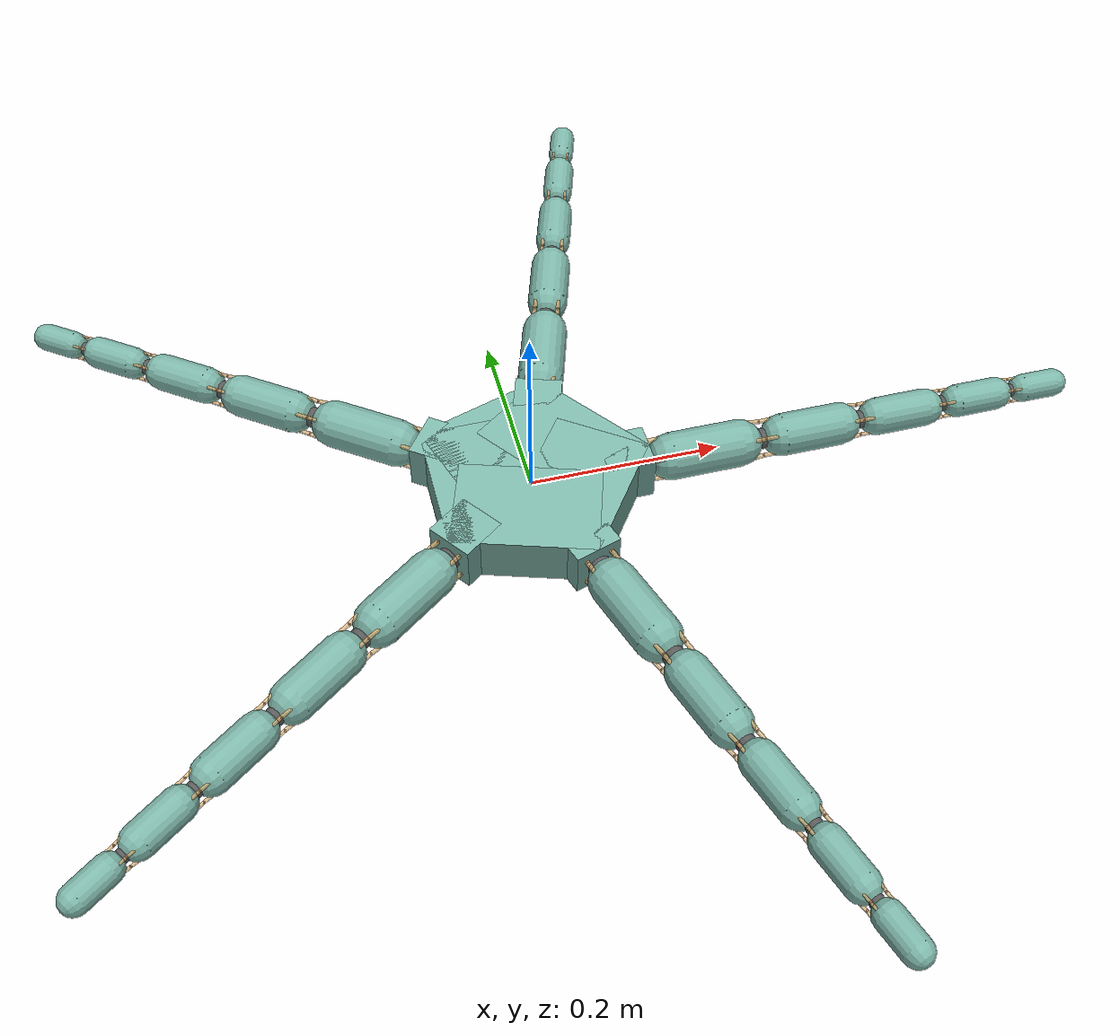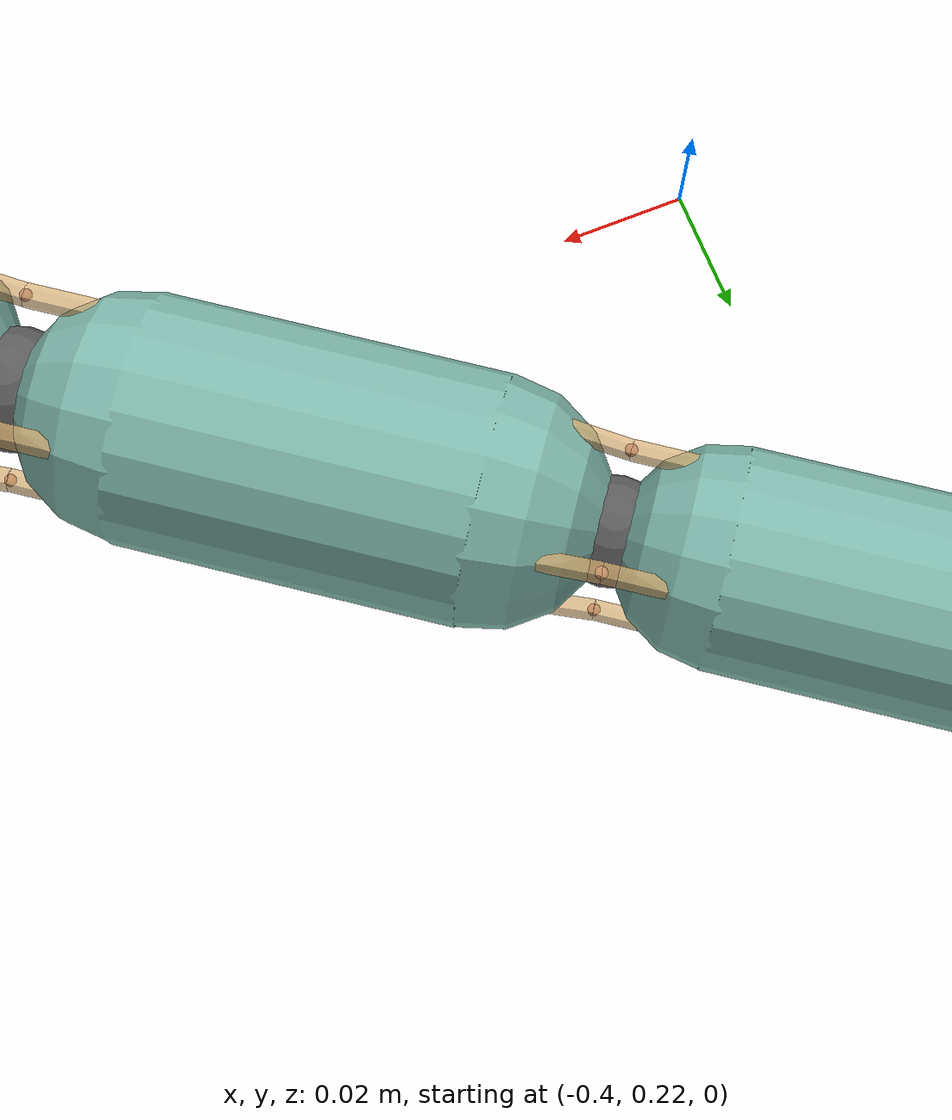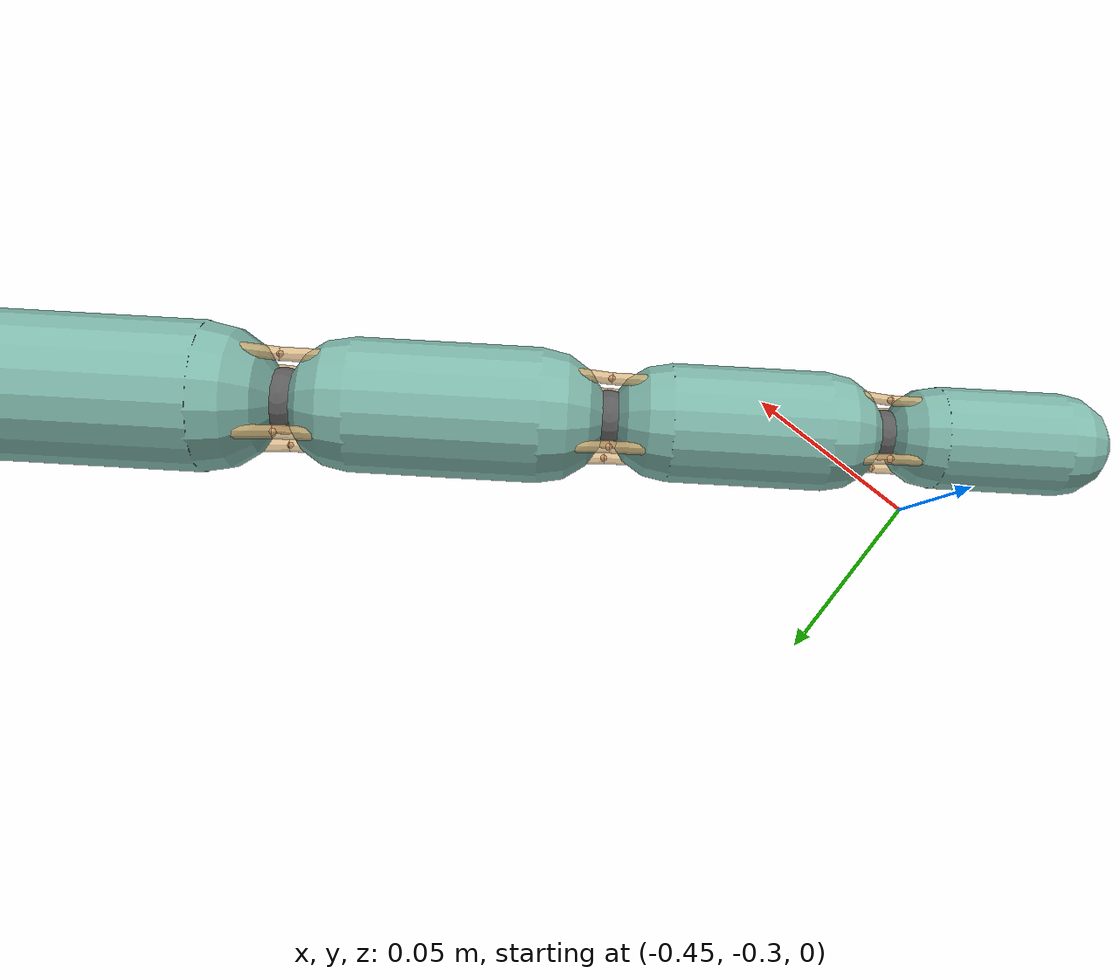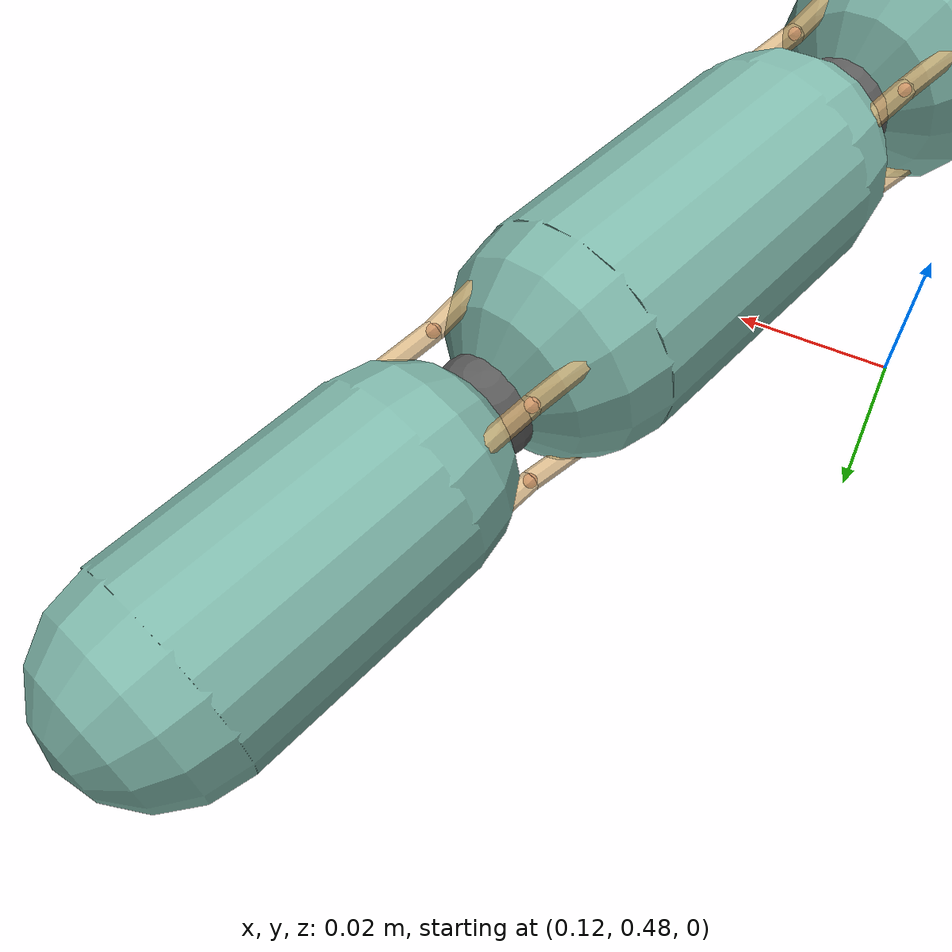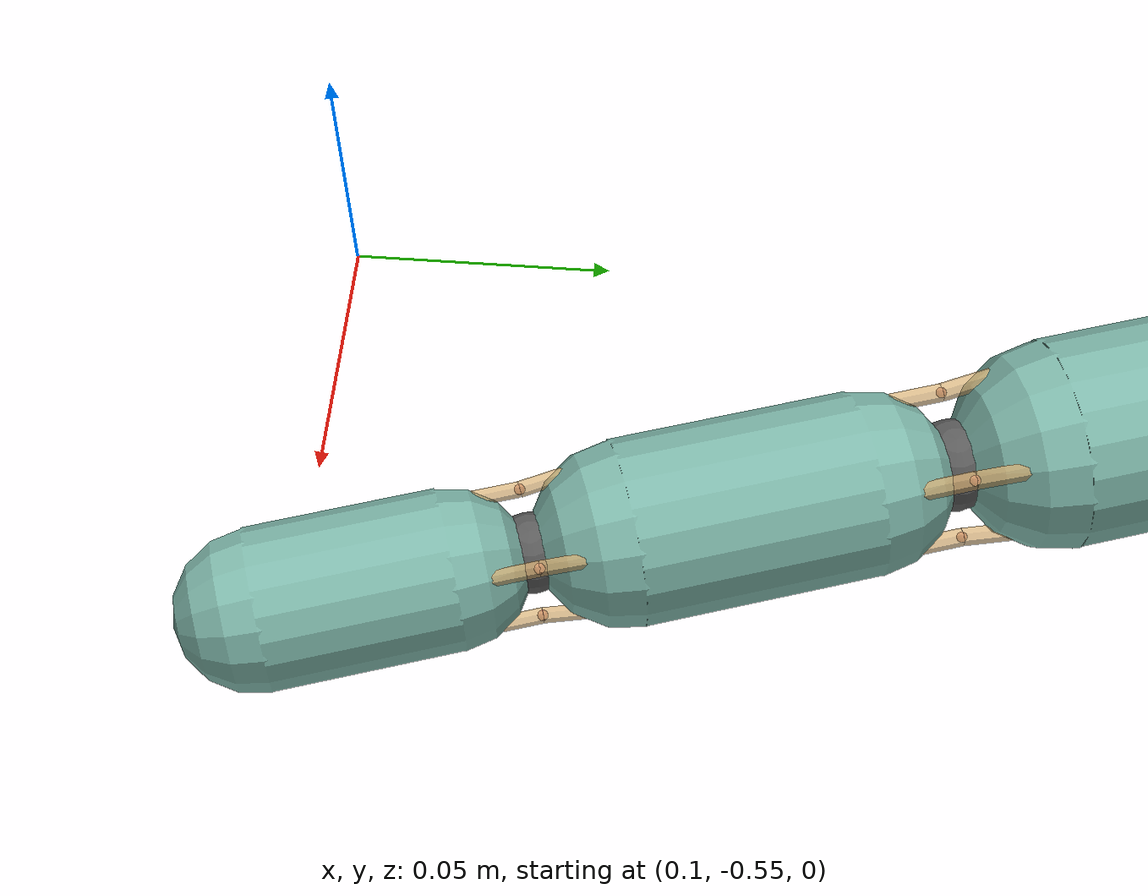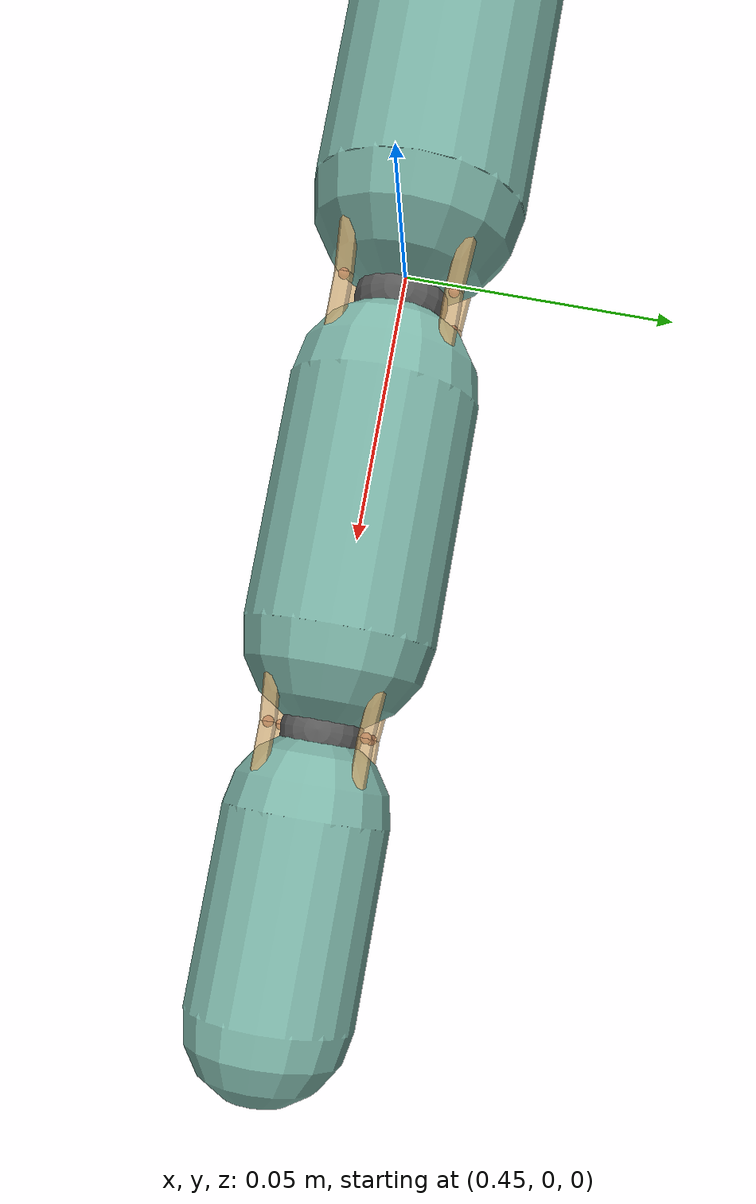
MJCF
<mujoco model="BrittleStarMorphology">
  <compiler angle="radian"/>
  <default>
    <default class="/">
      <geom contype="1" conaffinity="0" condim="4" density="1100"/>
    </default>
  </default>
  <worldbody>
    <body name="central_disk" pos="0 0 0" euler="0 0 0">
      <geom name="central_disk_pentagon_side_0" class="/" type="box" contype="0" conaffinity="0" size="0.050563562148434216 0.073473156536559142 0.025000000000000001" rgba="0.49019607843137253 0.70980392156862748 0.6588235294117647 1" mass="0" pos="0.040906781074217108 0.029720516134223551 0" euler="0 0 0.62831853071795862"/>
      <geom name="central_disk_pentagon_side_1" class="/" type="box" contype="0" conaffinity="0" size="0.050563562148434216 0.073473156536559142 0.025000000000000001" rgba="0.49019607843137253 0.70980392156862748 0.6588235294117647 1" mass="0" pos="-0.015624999999999997 0.048088805268363337 0" euler="0 0 1.8849555921538759"/>
      <geom name="central_disk_pentagon_side_2" class="/" type="box" contype="0" conaffinity="0" size="0.050563562148434216 0.073473156536559142 0.025000000000000001" rgba="0.49019607843137253 0.70980392156862748 0.6588235294117647 1" mass="0" pos="-0.050563562148434216 6.1922504538568225e-18 0" euler="0 0 3.1415926535897931"/>
      <geom name="central_disk_pentagon_side_3" class="/" type="box" contype="0" conaffinity="0" size="0.050563562148434216 0.073473156536559142 0.025000000000000001" rgba="0.49019607843137253 0.70980392156862748 0.6588235294117647 1" mass="0" pos="-0.015625000000000007 -0.048088805268363337 0" euler="0 0 4.3982297150257104"/>
      <geom name="central_disk_pentagon_side_4" class="/" type="box" contype="0" conaffinity="0" size="0.050563562148434216 0.073473156536559142 0.025000000000000001" rgba="0.49019607843137253 0.70980392156862748 0.6588235294117647 1" mass="0" pos="0.040906781074217101 -0.029720516134223562 0" euler="0 0 5.6548667764616276"/>
      <geom name="central_disk_pentagon_collider" class="/" type="cylinder" contype="1" conaffinity="0" size="0.125 0.025000000000000001" rgba="0 0 0 0" pos="0 0 0" euler="0 0 0"/>
      <geom name="central_disk_arm_connector_0" class="/" type="box" contype="0" conaffinity="0" size="0.025000000000000001 0.025000000000000001 0.025000000000000001" rgba="0.49019607843137253 0.70980392156862748 0.6588235294117647 1" pos="0.10000000000000001 0 0" euler="0 0 0"/>
      <geom name="central_disk_arm_connector_1" class="/" type="box" contype="0" conaffinity="0" size="0.025000000000000001 0.025000000000000001 0.025000000000000001" rgba="0.49019607843137253 0.70980392156862748 0.6588235294117647 1" pos="0.030901699437494747 0.095105651629515356 0" euler="0 0 1.2566370614359172"/>
      <geom name="central_disk_arm_connector_2" class="/" type="box" contype="0" conaffinity="0" size="0.025000000000000001 0.025000000000000001 0.025000000000000001" rgba="0.49019607843137253 0.70980392156862748 0.6588235294117647 1" pos="-0.080901699437494742 0.058778525229247328 0" euler="0 0 2.5132741228718345"/>
      <geom name="central_disk_arm_connector_3" class="/" type="box" contype="0" conaffinity="0" size="0.025000000000000001 0.025000000000000001 0.025000000000000001" rgba="0.49019607843137253 0.70980392156862748 0.6588235294117647 1" pos="-0.080901699437494756 -0.058778525229247307 0" euler="0 0 3.7699111843077517"/>
      <geom name="central_disk_arm_connector_4" class="/" type="box" contype="0" conaffinity="0" size="0.025000000000000001 0.025000000000000001 0.025000000000000001" rgba="0.49019607843137253 0.70980392156862748 0.6588235294117647 1" pos="0.030901699437494726 -0.09510565162951537 0" euler="0 0 5.026548245743669"/>
      <site name="central_disk_arm_0_tap_0" class="/" type="sphere" rgba="0.71764705882352942 0.33725490196078434 0.34901960784313724 1" size="0.001" pos="0.10000000000000001 0.014142135623730954 0.014142135623730952"/>
      <site name="central_disk_arm_0_tap_1" class="/" type="sphere" rgba="0.71764705882352942 0.33725490196078434 0.34901960784313724 1" size="0.001" pos="0.10000000000000001 -0.014142135623730952 0.014142135623730954"/>
      <site name="central_disk_arm_0_tap_2" class="/" type="sphere" rgba="0.71764705882352942 0.33725490196078434 0.34901960784313724 1" size="0.001" pos="0.10000000000000001 -0.014142135623730956 -0.014142135623730952"/>
      <site name="central_disk_arm_0_tap_3" class="/" type="sphere" rgba="0.71764705882352942 0.33725490196078434 0.34901960784313724 1" size="0.001" pos="0.10000000000000001 0.014142135623730949 -0.014142135623730956"/>
      <site name="central_disk_arm_1_tap_0" class="/" type="sphere" rgba="0.71764705882352942 0.33725490196078434 0.34901960784313724 1" size="0.001" pos="0.017451729198215596 0.099475811874003589 0.014142135623730952"/>
      <site name="central_disk_arm_1_tap_1" class="/" type="sphere" rgba="0.71764705882352942 0.33725490196078434 0.34901960784313724 1" size="0.001" pos="0.044351669676773897 0.090735491385027164 0.014142135623730954"/>
      <site name="central_disk_arm_1_tap_2" class="/" type="sphere" rgba="0.71764705882352942 0.33725490196078434 0.34901960784313724 1" size="0.001" pos="0.044351669676773897 0.090735491385027151 -0.014142135623730952"/>
      <site name="central_disk_arm_1_tap_3" class="/" type="sphere" rgba="0.71764705882352942 0.33725490196078434 0.34901960784313724 1" size="0.001" pos="0.017451729198215603 0.099475811874003575 -0.014142135623730956"/>
      <site name="central_disk_arm_2_tap_0" class="/" type="sphere" rgba="0.71764705882352942 0.33725490196078434 0.34901960784313724 1" size="0.001" pos="-0.089214238193043818 0.047337297172893623 0.014142135623730951"/>
      <site name="central_disk_arm_2_tap_1" class="/" type="sphere" rgba="0.71764705882352942 0.33725490196078434 0.34901960784313724 1" size="0.001" pos="-0.07258916068194568 0.070219753285600997 0.014142135623730952"/>
      <site name="central_disk_arm_2_tap_2" class="/" type="sphere" rgba="0.71764705882352942 0.33725490196078434 0.34901960784313724 1" size="0.001" pos="-0.072589160681945666 0.070219753285600997 -0.014142135623730951"/>
      <site name="central_disk_arm_2_tap_3" class="/" type="sphere" rgba="0.71764705882352942 0.33725490196078434 0.34901960784313724 1" size="0.001" pos="-0.089214238193043804 0.04733729717289363 -0.014142135623730954"/>
      <site name="central_disk_arm_3_tap_0" class="/" type="sphere" rgba="0.71764705882352942 0.33725490196078434 0.34901960784313724 1" size="0.001" pos="-0.07258916068194568 -0.070219753285600997 0.014142135623730952"/>
      <site name="central_disk_arm_3_tap_1" class="/" type="sphere" rgba="0.71764705882352942 0.33725490196078434 0.34901960784313724 1" size="0.001" pos="-0.089214238193043832 -0.047337297172893616 0.014142135623730954"/>
      <site name="central_disk_arm_3_tap_2" class="/" type="sphere" rgba="0.71764705882352942 0.33725490196078434 0.34901960784313724 1" size="0.001" pos="-0.089214238193043832 -0.047337297172893616 -0.014142135623730952"/>
      <site name="central_disk_arm_3_tap_3" class="/" type="sphere" rgba="0.71764705882352942 0.33725490196078434 0.34901960784313724 1" size="0.001" pos="-0.072589160681945694 -0.070219753285600997 -0.014142135623730956"/>
      <site name="central_disk_arm_4_tap_0" class="/" type="sphere" rgba="0.71764705882352942 0.33725490196078434 0.34901960784313724 1" size="0.001" pos="0.044351669676773869 -0.090735491385027164 0.014142135623730952"/>
      <site name="central_disk_arm_4_tap_1" class="/" type="sphere" rgba="0.71764705882352942 0.33725490196078434 0.34901960784313724 1" size="0.001" pos="0.017451729198215568 -0.099475811874003575 0.014142135623730954"/>
      <site name="central_disk_arm_4_tap_2" class="/" type="sphere" rgba="0.71764705882352942 0.33725490196078434 0.34901960784313724 1" size="0.001" pos="0.017451729198215568 -0.099475811874003575 -0.014142135623730952"/>
      <site name="central_disk_arm_4_tap_3" class="/" type="sphere" rgba="0.71764705882352942 0.33725490196078434 0.34901960784313724 1" size="0.001" pos="0.044351669676773862 -0.090735491385027164 -0.014142135623730956"/>
      <body name="arm_0" pos="0.125 0 0" euler="0 0 0">
        <body name="arm_0_segment_0" pos="0 0 0" euler="0 0 0">
          <geom name="arm_0_segment_0_capsule" class="/" type="capsule" size="0.025000000000000001 0.037499999999999999" rgba="0.49019607843137253 0.70980392156862748 0.6588235294117647 1" pos="0.0625 0 0" euler="0 1.5707963267948966 0"/>
          <geom name="arm_0_segment_0_connector" class="/" type="sphere" contype="0" conaffinity="0" size="0.012500000000000001" rgba="0.34901960784313724 0.34901960784313724 0.34901960784313724 1" pos="0 0 0"/>
          <joint name="arm_0_segment_0_in_plane_joint" class="/" type="hinge" axis="0 0 1" limited="true" stiffness="0.0050000000000000001" range="-1.0471975511965976 1.0471975511965976" armature="0.10000000000000001" damping="0.29999999999999999"/>
          <joint name="arm_0_segment_0_out_of_plane_joint" class="/" type="hinge" axis="0 -1 0" limited="true" stiffness="0.0050000000000000001" range="-0.78539816339744828 0.78539816339744828" armature="0.10000000000000001" damping="0.29999999999999999"/>
          <site name="arm_0_segment_0_proximal_tap_0" class="/" type="sphere" rgba="0.71764705882352942 0.33725490196078434 0.34901960784313724 1" size="0.001" pos="0.025000000000000001 0.014142135623730954 0.014142135623730952"/>
          <site name="arm_0_segment_0_distal_tap_0" class="/" type="sphere" rgba="0.71764705882352942 0.33725490196078434 0.34901960784313724 1" size="0.001" pos="0.10000000000000001 0.014142135623730954 0.014142135623730952"/>
          <site name="arm_0_segment_0_connector_tap_0" class="/" type="sphere" rgba="0.71764705882352942 0.33725490196078434 0.34901960784313724 1" size="0.001" pos="0 0.014142135623730954 0.014142135623730952"/>
          <site name="arm_0_segment_0_proximal_tap_1" class="/" type="sphere" rgba="0.71764705882352942 0.33725490196078434 0.34901960784313724 1" size="0.001" pos="0.025000000000000001 -0.014142135623730952 0.014142135623730954"/>
          <site name="arm_0_segment_0_distal_tap_1" class="/" type="sphere" rgba="0.71764705882352942 0.33725490196078434 0.34901960784313724 1" size="0.001" pos="0.10000000000000001 -0.014142135623730952 0.014142135623730954"/>
          <site name="arm_0_segment_0_connector_tap_1" class="/" type="sphere" rgba="0.71764705882352942 0.33725490196078434 0.34901960784313724 1" size="0.001" pos="0 -0.014142135623730952 0.014142135623730954"/>
          <site name="arm_0_segment_0_proximal_tap_2" class="/" type="sphere" rgba="0.71764705882352942 0.33725490196078434 0.34901960784313724 1" size="0.001" pos="0.025000000000000001 -0.014142135623730956 -0.014142135623730952"/>
          <site name="arm_0_segment_0_distal_tap_2" class="/" type="sphere" rgba="0.71764705882352942 0.33725490196078434 0.34901960784313724 1" size="0.001" pos="0.10000000000000001 -0.014142135623730956 -0.014142135623730952"/>
          <site name="arm_0_segment_0_connector_tap_2" class="/" type="sphere" rgba="0.71764705882352942 0.33725490196078434 0.34901960784313724 1" size="0.001" pos="0 -0.014142135623730956 -0.014142135623730952"/>
          <site name="arm_0_segment_0_proximal_tap_3" class="/" type="sphere" rgba="0.71764705882352942 0.33725490196078434 0.34901960784313724 1" size="0.001" pos="0.025000000000000001 0.014142135623730949 -0.014142135623730956"/>
          <site name="arm_0_segment_0_distal_tap_3" class="/" type="sphere" rgba="0.71764705882352942 0.33725490196078434 0.34901960784313724 1" size="0.001" pos="0.10000000000000001 0.014142135623730949 -0.014142135623730956"/>
          <site name="arm_0_segment_0_connector_tap_3" class="/" type="sphere" rgba="0.71764705882352942 0.33725490196078434 0.34901960784313724 1" size="0.001" pos="0 0.014142135623730949 -0.014142135623730956"/>
          <site name="arm_0_segment_0_contact_site_0" class="/" type="box" group="3" rgba="0.71764705882352942 0.33725490196078434 0.34901960784313724 0.5" size="0.050000000000000003 0.0012500000000000002 0.010000000000000002" pos="0.0625 1.454268073987482e-18 -0.02375" euler="-1.5707963267948966 0 0"/>
          <site name="arm_0_segment_0_contact_site_1" class="/" type="box" group="3" rgba="0.71764705882352942 0.33725490196078434 0.34901960784313724 0.5" size="0.050000000000000003 0.0012500000000000002 0.010000000000000002" pos="0.0625 0.016793786053180507 -0.016793786053180503" euler="-0.78539816339744828 0 0"/>
          <site name="arm_0_segment_0_contact_site_2" class="/" type="box" group="3" rgba="0.71764705882352942 0.33725490196078434 0.34901960784313724 0.5" size="0.050000000000000003 0.0012500000000000002 0.010000000000000002" pos="0.0625 0.02375 0" euler="0 0 0"/>
          <site name="arm_0_segment_0_contact_site_3" class="/" type="box" group="3" rgba="0.71764705882352942 0.33725490196078434 0.34901960784313724 0.5" size="0.050000000000000003 0.0012500000000000002 0.010000000000000002" pos="0.0625 0.016793786053180507 0.016793786053180503" euler="0.78539816339744828 0 0"/>
          <site name="arm_0_segment_0_contact_site_4" class="/" type="box" group="3" rgba="0.71764705882352942 0.33725490196078434 0.34901960784313724 0.5" size="0.050000000000000003 0.0012500000000000002 0.010000000000000002" pos="0.0625 1.454268073987482e-18 0.02375" euler="1.5707963267948966 0 0"/>
          <site name="arm_0_segment_0_contact_site_5" class="/" type="box" group="3" rgba="0.71764705882352942 0.33725490196078434 0.34901960784313724 0.5" size="0.050000000000000003 0.0012500000000000002 0.010000000000000002" pos="0.0625 -0.016793786053180503 0.016793786053180507" euler="2.3561944901923448 0 0"/>
          <site name="arm_0_segment_0_contact_site_6" class="/" type="box" group="3" rgba="0.71764705882352942 0.33725490196078434 0.34901960784313724 0.5" size="0.050000000000000003 0.0012500000000000002 0.010000000000000002" pos="0.0625 -0.02375 2.908536147974964e-18" euler="3.1415926535897931 0 0"/>
          <site name="arm_0_segment_0_contact_site_7" class="/" type="box" group="3" rgba="0.71764705882352942 0.33725490196078434 0.34901960784313724 0.5" size="0.050000000000000003 0.0012500000000000002 0.010000000000000002" pos="0.0625 -0.016793786053180507 -0.016793786053180503" euler="3.9269908169872414 0 0"/>
          <body name="arm_0_segment_1" pos="0.125 0 0" euler="0 0 0">
            <geom name="arm_0_segment_1_capsule" class="/" type="capsule" size="0.022499999999999999 0.032500000000000001" rgba="0.49019607843137253 0.70980392156862748 0.6588235294117647 1" pos="0.055 0 0" euler="0 1.5707963267948966 0"/>
            <geom name="arm_0_segment_1_connector" class="/" type="sphere" contype="0" conaffinity="0" size="0.01125" rgba="0.34901960784313724 0.34901960784313724 0.34901960784313724 1" pos="0 0 0"/>
            <joint name="arm_0_segment_1_in_plane_joint" class="/" type="hinge" axis="0 0 1" limited="true" stiffness="0.0050000000000000001" range="-1.0471975511965976 1.0471975511965976" armature="0.10000000000000001" damping="0.29999999999999999"/>
            <joint name="arm_0_segment_1_out_of_plane_joint" class="/" type="hinge" axis="0 -1 0" limited="true" stiffness="0.0050000000000000001" range="-0.78539816339744828 0.78539816339744828" armature="0.10000000000000001" damping="0.29999999999999999"/>
            <site name="arm_0_segment_1_proximal_tap_0" class="/" type="sphere" rgba="0.71764705882352942 0.33725490196078434 0.34901960784313724 1" size="0.001" pos="0.022499999999999999 0.012727922061357855 0.012727922061357854"/>
            <site name="arm_0_segment_1_distal_tap_0" class="/" type="sphere" rgba="0.71764705882352942 0.33725490196078434 0.34901960784313724 1" size="0.001" pos="0.087499999999999994 0.012727922061357855 0.012727922061357854"/>
            <site name="arm_0_segment_1_connector_tap_0" class="/" type="sphere" rgba="0.71764705882352942 0.33725490196078434 0.34901960784313724 1" size="0.001" pos="0 0.012727922061357855 0.012727922061357854"/>
            <site name="arm_0_segment_1_proximal_tap_1" class="/" type="sphere" rgba="0.71764705882352942 0.33725490196078434 0.34901960784313724 1" size="0.001" pos="0.022499999999999999 -0.012727922061357854 0.012727922061357855"/>
            <site name="arm_0_segment_1_distal_tap_1" class="/" type="sphere" rgba="0.71764705882352942 0.33725490196078434 0.34901960784313724 1" size="0.001" pos="0.087499999999999994 -0.012727922061357854 0.012727922061357855"/>
            <site name="arm_0_segment_1_connector_tap_1" class="/" type="sphere" rgba="0.71764705882352942 0.33725490196078434 0.34901960784313724 1" size="0.001" pos="0 -0.012727922061357854 0.012727922061357855"/>
            <site name="arm_0_segment_1_proximal_tap_2" class="/" type="sphere" rgba="0.71764705882352942 0.33725490196078434 0.34901960784313724 1" size="0.001" pos="0.022499999999999999 -0.012727922061357857 -0.012727922061357854"/>
            <site name="arm_0_segment_1_distal_tap_2" class="/" type="sphere" rgba="0.71764705882352942 0.33725490196078434 0.34901960784313724 1" size="0.001" pos="0.087499999999999994 -0.012727922061357857 -0.012727922061357854"/>
            <site name="arm_0_segment_1_connector_tap_2" class="/" type="sphere" rgba="0.71764705882352942 0.33725490196078434 0.34901960784313724 1" size="0.001" pos="0 -0.012727922061357857 -0.012727922061357854"/>
            <site name="arm_0_segment_1_proximal_tap_3" class="/" type="sphere" rgba="0.71764705882352942 0.33725490196078434 0.34901960784313724 1" size="0.001" pos="0.022499999999999999 0.012727922061357852 -0.012727922061357857"/>
            <site name="arm_0_segment_1_distal_tap_3" class="/" type="sphere" rgba="0.71764705882352942 0.33725490196078434 0.34901960784313724 1" size="0.001" pos="0.087499999999999994 0.012727922061357852 -0.012727922061357857"/>
            <site name="arm_0_segment_1_connector_tap_3" class="/" type="sphere" rgba="0.71764705882352942 0.33725490196078434 0.34901960784313724 1" size="0.001" pos="0 0.012727922061357852 -0.012727922061357857"/>
            <site name="arm_0_segment_1_contact_site_0" class="/" type="box" group="3" rgba="0.71764705882352942 0.33725490196078434 0.34901960784313724 0.5" size="0.043749999999999997 0.0011249999999999999 0.0089999999999999993" pos="0.055 1.3088412665887335e-18 -0.021374999999999998" euler="-1.5707963267948966 0 0"/>
            <site name="arm_0_segment_1_contact_site_1" class="/" type="box" group="3" rgba="0.71764705882352942 0.33725490196078434 0.34901960784313724 0.5" size="0.043749999999999997 0.0011249999999999999 0.0089999999999999993" pos="0.055 0.015114407447862454 -0.01511440744786245" euler="-0.78539816339744828 0 0"/>
            <site name="arm_0_segment_1_contact_site_2" class="/" type="box" group="3" rgba="0.71764705882352942 0.33725490196078434 0.34901960784313724 0.5" size="0.043749999999999997 0.0011249999999999999 0.0089999999999999993" pos="0.055 0.021374999999999998 0" euler="0 0 0"/>
            <site name="arm_0_segment_1_contact_site_3" class="/" type="box" group="3" rgba="0.71764705882352942 0.33725490196078434 0.34901960784313724 0.5" size="0.043749999999999997 0.0011249999999999999 0.0089999999999999993" pos="0.055 0.015114407447862454 0.01511440744786245" euler="0.78539816339744828 0 0"/>
            <site name="arm_0_segment_1_contact_site_4" class="/" type="box" group="3" rgba="0.71764705882352942 0.33725490196078434 0.34901960784313724 0.5" size="0.043749999999999997 0.0011249999999999999 0.0089999999999999993" pos="0.055 1.3088412665887335e-18 0.021374999999999998" euler="1.5707963267948966 0 0"/>
            <site name="arm_0_segment_1_contact_site_5" class="/" type="box" group="3" rgba="0.71764705882352942 0.33725490196078434 0.34901960784313724 0.5" size="0.043749999999999997 0.0011249999999999999 0.0089999999999999993" pos="0.055 -0.01511440744786245 0.015114407447862454" euler="2.3561944901923448 0 0"/>
            <site name="arm_0_segment_1_contact_site_6" class="/" type="box" group="3" rgba="0.71764705882352942 0.33725490196078434 0.34901960784313724 0.5" size="0.043749999999999997 0.0011249999999999999 0.0089999999999999993" pos="0.055 -0.021374999999999998 2.6176825331774671e-18" euler="3.1415926535897931 0 0"/>
            <site name="arm_0_segment_1_contact_site_7" class="/" type="box" group="3" rgba="0.71764705882352942 0.33725490196078434 0.34901960784313724 0.5" size="0.043749999999999997 0.0011249999999999999 0.0089999999999999993" pos="0.055 -0.015114407447862455 -0.01511440744786245" euler="3.9269908169872414 0 0"/>
            <body name="arm_0_segment_2" pos="0.11 0 0" euler="0 0 0">
              <geom name="arm_0_segment_2_capsule" class="/" type="capsule" size="0.02 0.027499999999999997" rgba="0.49019607843137253 0.70980392156862748 0.6588235294117647 1" pos="0.047500000000000001 0 0" euler="0 1.5707963267948966 0"/>
              <geom name="arm_0_segment_2_connector" class="/" type="sphere" contype="0" conaffinity="0" size="0.01" rgba="0.34901960784313724 0.34901960784313724 0.34901960784313724 1" pos="0 0 0"/>
              <joint name="arm_0_segment_2_in_plane_joint" class="/" type="hinge" axis="0 0 1" limited="true" stiffness="0.0050000000000000001" range="-1.0471975511965976 1.0471975511965976" armature="0.10000000000000001" damping="0.29999999999999999"/>
              <joint name="arm_0_segment_2_out_of_plane_joint" class="/" type="hinge" axis="0 -1 0" limited="true" stiffness="0.0050000000000000001" range="-0.78539816339744828 0.78539816339744828" armature="0.10000000000000001" damping="0.29999999999999999"/>
              <site name="arm_0_segment_2_proximal_tap_0" class="/" type="sphere" rgba="0.71764705882352942 0.33725490196078434 0.34901960784313724 1" size="0.001" pos="0.02 0.011313708498984762 0.01131370849898476"/>
              <site name="arm_0_segment_2_distal_tap_0" class="/" type="sphere" rgba="0.71764705882352942 0.33725490196078434 0.34901960784313724 1" size="0.001" pos="0.074999999999999997 0.011313708498984762 0.01131370849898476"/>
              <site name="arm_0_segment_2_connector_tap_0" class="/" type="sphere" rgba="0.71764705882352942 0.33725490196078434 0.34901960784313724 1" size="0.001" pos="0 0.011313708498984762 0.01131370849898476"/>
              <site name="arm_0_segment_2_proximal_tap_1" class="/" type="sphere" rgba="0.71764705882352942 0.33725490196078434 0.34901960784313724 1" size="0.001" pos="0.02 -0.01131370849898476 0.011313708498984762"/>
              <site name="arm_0_segment_2_distal_tap_1" class="/" type="sphere" rgba="0.71764705882352942 0.33725490196078434 0.34901960784313724 1" size="0.001" pos="0.074999999999999997 -0.01131370849898476 0.011313708498984762"/>
              <site name="arm_0_segment_2_connector_tap_1" class="/" type="sphere" rgba="0.71764705882352942 0.33725490196078434 0.34901960784313724 1" size="0.001" pos="0 -0.01131370849898476 0.011313708498984762"/>
              <site name="arm_0_segment_2_proximal_tap_2" class="/" type="sphere" rgba="0.71764705882352942 0.33725490196078434 0.34901960784313724 1" size="0.001" pos="0.02 -0.011313708498984764 -0.01131370849898476"/>
              <site name="arm_0_segment_2_distal_tap_2" class="/" type="sphere" rgba="0.71764705882352942 0.33725490196078434 0.34901960784313724 1" size="0.001" pos="0.074999999999999997 -0.011313708498984764 -0.01131370849898476"/>
              <site name="arm_0_segment_2_connector_tap_2" class="/" type="sphere" rgba="0.71764705882352942 0.33725490196078434 0.34901960784313724 1" size="0.001" pos="0 -0.011313708498984764 -0.01131370849898476"/>
              <site name="arm_0_segment_2_proximal_tap_3" class="/" type="sphere" rgba="0.71764705882352942 0.33725490196078434 0.34901960784313724 1" size="0.001" pos="0.02 0.011313708498984758 -0.011313708498984764"/>
              <site name="arm_0_segment_2_distal_tap_3" class="/" type="sphere" rgba="0.71764705882352942 0.33725490196078434 0.34901960784313724 1" size="0.001" pos="0.074999999999999997 0.011313708498984758 -0.011313708498984764"/>
              <site name="arm_0_segment_2_connector_tap_3" class="/" type="sphere" rgba="0.71764705882352942 0.33725490196078434 0.34901960784313724 1" size="0.001" pos="0 0.011313708498984758 -0.011313708498984764"/>
              <site name="arm_0_segment_2_contact_site_0" class="/" type="box" group="3" rgba="0.71764705882352942 0.33725490196078434 0.34901960784313724 0.5" size="0.037499999999999999 0.001 0.0080000000000000002" pos="0.047500000000000001 1.1634144591899855e-18 -0.019" euler="-1.5707963267948966 0 0"/>
              <site name="arm_0_segment_2_contact_site_1" class="/" type="box" group="3" rgba="0.71764705882352942 0.33725490196078434 0.34901960784313724 0.5" size="0.037499999999999999 0.001 0.0080000000000000002" pos="0.047500000000000001 0.013435028842544404 -0.013435028842544402" euler="-0.78539816339744828 0 0"/>
              <site name="arm_0_segment_2_contact_site_2" class="/" type="box" group="3" rgba="0.71764705882352942 0.33725490196078434 0.34901960784313724 0.5" size="0.037499999999999999 0.001 0.0080000000000000002" pos="0.047500000000000001 0.019 0" euler="0 0 0"/>
              <site name="arm_0_segment_2_contact_site_3" class="/" type="box" group="3" rgba="0.71764705882352942 0.33725490196078434 0.34901960784313724 0.5" size="0.037499999999999999 0.001 0.0080000000000000002" pos="0.047500000000000001 0.013435028842544404 0.013435028842544402" euler="0.78539816339744828 0 0"/>
              <site name="arm_0_segment_2_contact_site_4" class="/" type="box" group="3" rgba="0.71764705882352942 0.33725490196078434 0.34901960784313724 0.5" size="0.037499999999999999 0.001 0.0080000000000000002" pos="0.047500000000000001 1.1634144591899855e-18 0.019" euler="1.5707963267948966 0 0"/>
              <site name="arm_0_segment_2_contact_site_5" class="/" type="box" group="3" rgba="0.71764705882352942 0.33725490196078434 0.34901960784313724 0.5" size="0.037499999999999999 0.001 0.0080000000000000002" pos="0.047500000000000001 -0.013435028842544402 0.013435028842544404" euler="2.3561944901923448 0 0"/>
              <site name="arm_0_segment_2_contact_site_6" class="/" type="box" group="3" rgba="0.71764705882352942 0.33725490196078434 0.34901960784313724 0.5" size="0.037499999999999999 0.001 0.0080000000000000002" pos="0.047500000000000001 -0.019 2.3268289183799709e-18" euler="3.1415926535897931 0 0"/>
              <site name="arm_0_segment_2_contact_site_7" class="/" type="box" group="3" rgba="0.71764705882352942 0.33725490196078434 0.34901960784313724 0.5" size="0.037499999999999999 0.001 0.0080000000000000002" pos="0.047500000000000001 -0.013435028842544406 -0.013435028842544402" euler="3.9269908169872414 0 0"/>
              <body name="arm_0_segment_3" pos="0.095000000000000001 0 0" euler="0 0 0">
                <geom name="arm_0_segment_3_capsule" class="/" type="capsule" size="0.017500000000000002 0.022499999999999999" rgba="0.49019607843137253 0.70980392156862748 0.6588235294117647 1" pos="0.040000000000000001 0 0" euler="0 1.5707963267948966 0"/>
                <geom name="arm_0_segment_3_connector" class="/" type="sphere" contype="0" conaffinity="0" size="0.0087500000000000008" rgba="0.34901960784313724 0.34901960784313724 0.34901960784313724 1" pos="0 0 0"/>
                <joint name="arm_0_segment_3_in_plane_joint" class="/" type="hinge" axis="0 0 1" limited="true" stiffness="0.0050000000000000001" range="-1.0471975511965976 1.0471975511965976" armature="0.10000000000000001" damping="0.29999999999999999"/>
                <joint name="arm_0_segment_3_out_of_plane_joint" class="/" type="hinge" axis="0 -1 0" limited="true" stiffness="0.0050000000000000001" range="-0.78539816339744828 0.78539816339744828" armature="0.10000000000000001" damping="0.29999999999999999"/>
                <site name="arm_0_segment_3_proximal_tap_0" class="/" type="sphere" rgba="0.71764705882352942 0.33725490196078434 0.34901960784313724 1" size="0.001" pos="0.017500000000000002 0.0098994949366116667 0.0098994949366116667"/>
                <site name="arm_0_segment_3_distal_tap_0" class="/" type="sphere" rgba="0.71764705882352942 0.33725490196078434 0.34901960784313724 1" size="0.001" pos="0.0625 0.0098994949366116667 0.0098994949366116667"/>
                <site name="arm_0_segment_3_connector_tap_0" class="/" type="sphere" rgba="0.71764705882352942 0.33725490196078434 0.34901960784313724 1" size="0.001" pos="0 0.0098994949366116667 0.0098994949366116667"/>
                <site name="arm_0_segment_3_proximal_tap_1" class="/" type="sphere" rgba="0.71764705882352942 0.33725490196078434 0.34901960784313724 1" size="0.001" pos="0.017500000000000002 -0.0098994949366116667 0.0098994949366116667"/>
                <site name="arm_0_segment_3_distal_tap_1" class="/" type="sphere" rgba="0.71764705882352942 0.33725490196078434 0.34901960784313724 1" size="0.001" pos="0.0625 -0.0098994949366116667 0.0098994949366116667"/>
                <site name="arm_0_segment_3_connector_tap_1" class="/" type="sphere" rgba="0.71764705882352942 0.33725490196078434 0.34901960784313724 1" size="0.001" pos="0 -0.0098994949366116667 0.0098994949366116667"/>
                <site name="arm_0_segment_3_proximal_tap_2" class="/" type="sphere" rgba="0.71764705882352942 0.33725490196078434 0.34901960784313724 1" size="0.001" pos="0.017500000000000002 -0.0098994949366116684 -0.0098994949366116667"/>
                <site name="arm_0_segment_3_distal_tap_2" class="/" type="sphere" rgba="0.71764705882352942 0.33725490196078434 0.34901960784313724 1" size="0.001" pos="0.0625 -0.0098994949366116684 -0.0098994949366116667"/>
                <site name="arm_0_segment_3_connector_tap_2" class="/" type="sphere" rgba="0.71764705882352942 0.33725490196078434 0.34901960784313724 1" size="0.001" pos="0 -0.0098994949366116684 -0.0098994949366116667"/>
                <site name="arm_0_segment_3_proximal_tap_3" class="/" type="sphere" rgba="0.71764705882352942 0.33725490196078434 0.34901960784313724 1" size="0.001" pos="0.017500000000000002 0.009899494936611665 -0.0098994949366116684"/>
                <site name="arm_0_segment_3_distal_tap_3" class="/" type="sphere" rgba="0.71764705882352942 0.33725490196078434 0.34901960784313724 1" size="0.001" pos="0.0625 0.009899494936611665 -0.0098994949366116684"/>
                <site name="arm_0_segment_3_connector_tap_3" class="/" type="sphere" rgba="0.71764705882352942 0.33725490196078434 0.34901960784313724 1" size="0.001" pos="0 0.009899494936611665 -0.0098994949366116684"/>
                <site name="arm_0_segment_3_contact_site_0" class="/" type="box" group="3" rgba="0.71764705882352942 0.33725490196078434 0.34901960784313724 0.5" size="0.03125 0.00087500000000000013 0.007000000000000001" pos="0.040000000000000001 1.0179876517912374e-18 -0.016625000000000001" euler="-1.5707963267948966 0 0"/>
                <site name="arm_0_segment_3_contact_site_1" class="/" type="box" group="3" rgba="0.71764705882352942 0.33725490196078434 0.34901960784313724 0.5" size="0.03125 0.00087500000000000013 0.007000000000000001" pos="0.040000000000000001 0.011755650237226354 -0.011755650237226353" euler="-0.78539816339744828 0 0"/>
                <site name="arm_0_segment_3_contact_site_2" class="/" type="box" group="3" rgba="0.71764705882352942 0.33725490196078434 0.34901960784313724 0.5" size="0.03125 0.00087500000000000013 0.007000000000000001" pos="0.040000000000000001 0.016625000000000001 0" euler="0 0 0"/>
                <site name="arm_0_segment_3_contact_site_3" class="/" type="box" group="3" rgba="0.71764705882352942 0.33725490196078434 0.34901960784313724 0.5" size="0.03125 0.00087500000000000013 0.007000000000000001" pos="0.040000000000000001 0.011755650237226354 0.011755650237226353" euler="0.78539816339744828 0 0"/>
                <site name="arm_0_segment_3_contact_site_4" class="/" type="box" group="3" rgba="0.71764705882352942 0.33725490196078434 0.34901960784313724 0.5" size="0.03125 0.00087500000000000013 0.007000000000000001" pos="0.040000000000000001 1.0179876517912374e-18 0.016625000000000001" euler="1.5707963267948966 0 0"/>
                <site name="arm_0_segment_3_contact_site_5" class="/" type="box" group="3" rgba="0.71764705882352942 0.33725490196078434 0.34901960784313724 0.5" size="0.03125 0.00087500000000000013 0.007000000000000001" pos="0.040000000000000001 -0.011755650237226353 0.011755650237226354" euler="2.3561944901923448 0 0"/>
                <site name="arm_0_segment_3_contact_site_6" class="/" type="box" group="3" rgba="0.71764705882352942 0.33725490196078434 0.34901960784313724 0.5" size="0.03125 0.00087500000000000013 0.007000000000000001" pos="0.040000000000000001 -0.016625000000000001 2.0359753035824748e-18" euler="3.1415926535897931 0 0"/>
                <site name="arm_0_segment_3_contact_site_7" class="/" type="box" group="3" rgba="0.71764705882352942 0.33725490196078434 0.34901960784313724 0.5" size="0.03125 0.00087500000000000013 0.007000000000000001" pos="0.040000000000000001 -0.011755650237226356 -0.011755650237226353" euler="3.9269908169872414 0 0"/>
                <body name="arm_0_segment_4" pos="0.080000000000000002 0 0" euler="0 0 0">
                  <geom name="arm_0_segment_4_capsule" class="/" type="capsule" size="0.014999999999999999 0.017499999999999998" rgba="0.49019607843137253 0.70980392156862748 0.6588235294117647 1" pos="0.032500000000000001 0 0" euler="0 1.5707963267948966 0"/>
                  <geom name="arm_0_segment_4_connector" class="/" type="sphere" contype="0" conaffinity="0" size="0.0074999999999999997" rgba="0.34901960784313724 0.34901960784313724 0.34901960784313724 1" pos="0 0 0"/>
                  <joint name="arm_0_segment_4_in_plane_joint" class="/" type="hinge" axis="0 0 1" limited="true" stiffness="0.0050000000000000001" range="-1.0471975511965976 1.0471975511965976" armature="0.10000000000000001" damping="0.29999999999999999"/>
                  <joint name="arm_0_segment_4_out_of_plane_joint" class="/" type="hinge" axis="0 -1 0" limited="true" stiffness="0.0050000000000000001" range="-0.78539816339744828 0.78539816339744828" armature="0.10000000000000001" damping="0.29999999999999999"/>
                  <site name="arm_0_segment_4_proximal_tap_0" class="/" type="sphere" rgba="0.71764705882352942 0.33725490196078434 0.34901960784313724 1" size="0.001" pos="0.014999999999999999 0.0084852813742385715 0.0084852813742385697"/>
                  <site name="arm_0_segment_4_distal_tap_0" class="/" type="sphere" rgba="0.71764705882352942 0.33725490196078434 0.34901960784313724 1" size="0.001" pos="0.049999999999999996 0.0084852813742385715 0.0084852813742385697"/>
                  <site name="arm_0_segment_4_connector_tap_0" class="/" type="sphere" rgba="0.71764705882352942 0.33725490196078434 0.34901960784313724 1" size="0.001" pos="0 0.0084852813742385715 0.0084852813742385697"/>
                  <site name="arm_0_segment_4_proximal_tap_1" class="/" type="sphere" rgba="0.71764705882352942 0.33725490196078434 0.34901960784313724 1" size="0.001" pos="0.014999999999999999 -0.0084852813742385697 0.0084852813742385715"/>
                  <site name="arm_0_segment_4_distal_tap_1" class="/" type="sphere" rgba="0.71764705882352942 0.33725490196078434 0.34901960784313724 1" size="0.001" pos="0.049999999999999996 -0.0084852813742385697 0.0084852813742385715"/>
                  <site name="arm_0_segment_4_connector_tap_1" class="/" type="sphere" rgba="0.71764705882352942 0.33725490196078434 0.34901960784313724 1" size="0.001" pos="0 -0.0084852813742385697 0.0084852813742385715"/>
                  <site name="arm_0_segment_4_proximal_tap_2" class="/" type="sphere" rgba="0.71764705882352942 0.33725490196078434 0.34901960784313724 1" size="0.001" pos="0.014999999999999999 -0.0084852813742385732 -0.0084852813742385697"/>
                  <site name="arm_0_segment_4_distal_tap_2" class="/" type="sphere" rgba="0.71764705882352942 0.33725490196078434 0.34901960784313724 1" size="0.001" pos="0.049999999999999996 -0.0084852813742385732 -0.0084852813742385697"/>
                  <site name="arm_0_segment_4_connector_tap_2" class="/" type="sphere" rgba="0.71764705882352942 0.33725490196078434 0.34901960784313724 1" size="0.001" pos="0 -0.0084852813742385732 -0.0084852813742385697"/>
                  <site name="arm_0_segment_4_proximal_tap_3" class="/" type="sphere" rgba="0.71764705882352942 0.33725490196078434 0.34901960784313724 1" size="0.001" pos="0.014999999999999999 0.008485281374238568 -0.0084852813742385732"/>
                  <site name="arm_0_segment_4_distal_tap_3" class="/" type="sphere" rgba="0.71764705882352942 0.33725490196078434 0.34901960784313724 1" size="0.001" pos="0.049999999999999996 0.008485281374238568 -0.0084852813742385732"/>
                  <site name="arm_0_segment_4_connector_tap_3" class="/" type="sphere" rgba="0.71764705882352942 0.33725490196078434 0.34901960784313724 1" size="0.001" pos="0 0.008485281374238568 -0.0084852813742385732"/>
                  <site name="arm_0_segment_4_contact_site_0" class="/" type="box" group="3" rgba="0.71764705882352942 0.33725490196078434 0.34901960784313724 0.5" size="0.024999999999999998 0.00075000000000000002 0.0060000000000000001" pos="0.032500000000000001 8.7256084439248915e-19 -0.014249999999999999" euler="-1.5707963267948966 0 0"/>
                  <site name="arm_0_segment_4_contact_site_1" class="/" type="box" group="3" rgba="0.71764705882352942 0.33725490196078434 0.34901960784313724 0.5" size="0.024999999999999998 0.00075000000000000002 0.0060000000000000001" pos="0.032500000000000001 0.010076271631908301 -0.010076271631908301" euler="-0.78539816339744828 0 0"/>
                  <site name="arm_0_segment_4_contact_site_2" class="/" type="box" group="3" rgba="0.71764705882352942 0.33725490196078434 0.34901960784313724 0.5" size="0.024999999999999998 0.00075000000000000002 0.0060000000000000001" pos="0.032500000000000001 0.014249999999999999 0" euler="0 0 0"/>
                  <site name="arm_0_segment_4_contact_site_3" class="/" type="box" group="3" rgba="0.71764705882352942 0.33725490196078434 0.34901960784313724 0.5" size="0.024999999999999998 0.00075000000000000002 0.0060000000000000001" pos="0.032500000000000001 0.010076271631908301 0.010076271631908301" euler="0.78539816339744828 0 0"/>
                  <site name="arm_0_segment_4_contact_site_4" class="/" type="box" group="3" rgba="0.71764705882352942 0.33725490196078434 0.34901960784313724 0.5" size="0.024999999999999998 0.00075000000000000002 0.0060000000000000001" pos="0.032500000000000001 8.7256084439248915e-19 0.014249999999999999" euler="1.5707963267948966 0 0"/>
                  <site name="arm_0_segment_4_contact_site_5" class="/" type="box" group="3" rgba="0.71764705882352942 0.33725490196078434 0.34901960784313724 0.5" size="0.024999999999999998 0.00075000000000000002 0.0060000000000000001" pos="0.032500000000000001 -0.010076271631908301 0.010076271631908301" euler="2.3561944901923448 0 0"/>
                  <site name="arm_0_segment_4_contact_site_6" class="/" type="box" group="3" rgba="0.71764705882352942 0.33725490196078434 0.34901960784313724 0.5" size="0.024999999999999998 0.00075000000000000002 0.0060000000000000001" pos="0.032500000000000001 -0.014249999999999999 1.7451216887849783e-18" euler="3.1415926535897931 0 0"/>
                  <site name="arm_0_segment_4_contact_site_7" class="/" type="box" group="3" rgba="0.71764705882352942 0.33725490196078434 0.34901960784313724 0.5" size="0.024999999999999998 0.00075000000000000002 0.0060000000000000001" pos="0.032500000000000001 -0.010076271631908303 -0.010076271631908301" euler="3.9269908169872414 0 0"/>
                </body>
              </body>
            </body>
          </body>
        </body>
      </body>
      <body name="arm_1" pos="0.038627124296868431 0.11888206453689419 0" euler="0 0 1.2566370614359172">
        <body name="arm_1_segment_0" pos="0 0 0" euler="0 0 0">
          <geom name="arm_1_segment_0_capsule" class="/" type="capsule" size="0.025000000000000001 0.037499999999999999" rgba="0.49019607843137253 0.70980392156862748 0.6588235294117647 1" pos="0.0625 0 0" euler="0 1.5707963267948966 0"/>
          <geom name="arm_1_segment_0_connector" class="/" type="sphere" contype="0" conaffinity="0" size="0.012500000000000001" rgba="0.34901960784313724 0.34901960784313724 0.34901960784313724 1" pos="0 0 0"/>
          <joint name="arm_1_segment_0_in_plane_joint" class="/" type="hinge" axis="0 0 1" limited="true" stiffness="0.0050000000000000001" range="-1.0471975511965976 1.0471975511965976" armature="0.10000000000000001" damping="0.29999999999999999"/>
          <joint name="arm_1_segment_0_out_of_plane_joint" class="/" type="hinge" axis="0 -1 0" limited="true" stiffness="0.0050000000000000001" range="-0.78539816339744828 0.78539816339744828" armature="0.10000000000000001" damping="0.29999999999999999"/>
          <site name="arm_1_segment_0_proximal_tap_0" class="/" type="sphere" rgba="0.71764705882352942 0.33725490196078434 0.34901960784313724 1" size="0.001" pos="0.025000000000000001 0.014142135623730954 0.014142135623730952"/>
          <site name="arm_1_segment_0_distal_tap_0" class="/" type="sphere" rgba="0.71764705882352942 0.33725490196078434 0.34901960784313724 1" size="0.001" pos="0.10000000000000001 0.014142135623730954 0.014142135623730952"/>
          <site name="arm_1_segment_0_connector_tap_0" class="/" type="sphere" rgba="0.71764705882352942 0.33725490196078434 0.34901960784313724 1" size="0.001" pos="0 0.014142135623730954 0.014142135623730952"/>
          <site name="arm_1_segment_0_proximal_tap_1" class="/" type="sphere" rgba="0.71764705882352942 0.33725490196078434 0.34901960784313724 1" size="0.001" pos="0.025000000000000001 -0.014142135623730952 0.014142135623730954"/>
          <site name="arm_1_segment_0_distal_tap_1" class="/" type="sphere" rgba="0.71764705882352942 0.33725490196078434 0.34901960784313724 1" size="0.001" pos="0.10000000000000001 -0.014142135623730952 0.014142135623730954"/>
          <site name="arm_1_segment_0_connector_tap_1" class="/" type="sphere" rgba="0.71764705882352942 0.33725490196078434 0.34901960784313724 1" size="0.001" pos="0 -0.014142135623730952 0.014142135623730954"/>
          <site name="arm_1_segment_0_proximal_tap_2" class="/" type="sphere" rgba="0.71764705882352942 0.33725490196078434 0.34901960784313724 1" size="0.001" pos="0.025000000000000001 -0.014142135623730956 -0.014142135623730952"/>
          <site name="arm_1_segment_0_distal_tap_2" class="/" type="sphere" rgba="0.71764705882352942 0.33725490196078434 0.34901960784313724 1" size="0.001" pos="0.10000000000000001 -0.014142135623730956 -0.014142135623730952"/>
          <site name="arm_1_segment_0_connector_tap_2" class="/" type="sphere" rgba="0.71764705882352942 0.33725490196078434 0.34901960784313724 1" size="0.001" pos="0 -0.014142135623730956 -0.014142135623730952"/>
          <site name="arm_1_segment_0_proximal_tap_3" class="/" type="sphere" rgba="0.71764705882352942 0.33725490196078434 0.34901960784313724 1" size="0.001" pos="0.025000000000000001 0.014142135623730949 -0.014142135623730956"/>
          <site name="arm_1_segment_0_distal_tap_3" class="/" type="sphere" rgba="0.71764705882352942 0.33725490196078434 0.34901960784313724 1" size="0.001" pos="0.10000000000000001 0.014142135623730949 -0.014142135623730956"/>
          <site name="arm_1_segment_0_connector_tap_3" class="/" type="sphere" rgba="0.71764705882352942 0.33725490196078434 0.34901960784313724 1" size="0.001" pos="0 0.014142135623730949 -0.014142135623730956"/>
          <site name="arm_1_segment_0_contact_site_0" class="/" type="box" group="3" rgba="0.71764705882352942 0.33725490196078434 0.34901960784313724 0.5" size="0.050000000000000003 0.0012500000000000002 0.010000000000000002" pos="0.0625 1.454268073987482e-18 -0.02375" euler="-1.5707963267948966 0 0"/>
          <site name="arm_1_segment_0_contact_site_1" class="/" type="box" group="3" rgba="0.71764705882352942 0.33725490196078434 0.34901960784313724 0.5" size="0.050000000000000003 0.0012500000000000002 0.010000000000000002" pos="0.0625 0.016793786053180507 -0.016793786053180503" euler="-0.78539816339744828 0 0"/>
          <site name="arm_1_segment_0_contact_site_2" class="/" type="box" group="3" rgba="0.71764705882352942 0.33725490196078434 0.34901960784313724 0.5" size="0.050000000000000003 0.0012500000000000002 0.010000000000000002" pos="0.0625 0.02375 0" euler="0 0 0"/>
          <site name="arm_1_segment_0_contact_site_3" class="/" type="box" group="3" rgba="0.71764705882352942 0.33725490196078434 0.34901960784313724 0.5" size="0.050000000000000003 0.0012500000000000002 0.010000000000000002" pos="0.0625 0.016793786053180507 0.016793786053180503" euler="0.78539816339744828 0 0"/>
          <site name="arm_1_segment_0_contact_site_4" class="/" type="box" group="3" rgba="0.71764705882352942 0.33725490196078434 0.34901960784313724 0.5" size="0.050000000000000003 0.0012500000000000002 0.010000000000000002" pos="0.0625 1.454268073987482e-18 0.02375" euler="1.5707963267948966 0 0"/>
          <site name="arm_1_segment_0_contact_site_5" class="/" type="box" group="3" rgba="0.71764705882352942 0.33725490196078434 0.34901960784313724 0.5" size="0.050000000000000003 0.0012500000000000002 0.010000000000000002" pos="0.0625 -0.016793786053180503 0.016793786053180507" euler="2.3561944901923448 0 0"/>
          <site name="arm_1_segment_0_contact_site_6" class="/" type="box" group="3" rgba="0.71764705882352942 0.33725490196078434 0.34901960784313724 0.5" size="0.050000000000000003 0.0012500000000000002 0.010000000000000002" pos="0.0625 -0.02375 2.908536147974964e-18" euler="3.1415926535897931 0 0"/>
          <site name="arm_1_segment_0_contact_site_7" class="/" type="box" group="3" rgba="0.71764705882352942 0.33725490196078434 0.34901960784313724 0.5" size="0.050000000000000003 0.0012500000000000002 0.010000000000000002" pos="0.0625 -0.016793786053180507 -0.016793786053180503" euler="3.9269908169872414 0 0"/>
          <body name="arm_1_segment_1" pos="0.125 0 0" euler="0 0 0">
            <geom name="arm_1_segment_1_capsule" class="/" type="capsule" size="0.022499999999999999 0.032500000000000001" rgba="0.49019607843137253 0.70980392156862748 0.6588235294117647 1" pos="0.055 0 0" euler="0 1.5707963267948966 0"/>
            <geom name="arm_1_segment_1_connector" class="/" type="sphere" contype="0" conaffinity="0" size="0.01125" rgba="0.34901960784313724 0.34901960784313724 0.34901960784313724 1" pos="0 0 0"/>
            <joint name="arm_1_segment_1_in_plane_joint" class="/" type="hinge" axis="0 0 1" limited="true" stiffness="0.0050000000000000001" range="-1.0471975511965976 1.0471975511965976" armature="0.10000000000000001" damping="0.29999999999999999"/>
            <joint name="arm_1_segment_1_out_of_plane_joint" class="/" type="hinge" axis="0 -1 0" limited="true" stiffness="0.0050000000000000001" range="-0.78539816339744828 0.78539816339744828" armature="0.10000000000000001" damping="0.29999999999999999"/>
            <site name="arm_1_segment_1_proximal_tap_0" class="/" type="sphere" rgba="0.71764705882352942 0.33725490196078434 0.34901960784313724 1" size="0.001" pos="0.022499999999999999 0.012727922061357855 0.012727922061357854"/>
            <site name="arm_1_segment_1_distal_tap_0" class="/" type="sphere" rgba="0.71764705882352942 0.33725490196078434 0.34901960784313724 1" size="0.001" pos="0.087499999999999994 0.012727922061357855 0.012727922061357854"/>
            <site name="arm_1_segment_1_connector_tap_0" class="/" type="sphere" rgba="0.71764705882352942 0.33725490196078434 0.34901960784313724 1" size="0.001" pos="0 0.012727922061357855 0.012727922061357854"/>
            <site name="arm_1_segment_1_proximal_tap_1" class="/" type="sphere" rgba="0.71764705882352942 0.33725490196078434 0.34901960784313724 1" size="0.001" pos="0.022499999999999999 -0.012727922061357854 0.012727922061357855"/>
            <site name="arm_1_segment_1_distal_tap_1" class="/" type="sphere" rgba="0.71764705882352942 0.33725490196078434 0.34901960784313724 1" size="0.001" pos="0.087499999999999994 -0.012727922061357854 0.012727922061357855"/>
            <site name="arm_1_segment_1_connector_tap_1" class="/" type="sphere" rgba="0.71764705882352942 0.33725490196078434 0.34901960784313724 1" size="0.001" pos="0 -0.012727922061357854 0.012727922061357855"/>
            <site name="arm_1_segment_1_proximal_tap_2" class="/" type="sphere" rgba="0.71764705882352942 0.33725490196078434 0.34901960784313724 1" size="0.001" pos="0.022499999999999999 -0.012727922061357857 -0.012727922061357854"/>
            <site name="arm_1_segment_1_distal_tap_2" class="/" type="sphere" rgba="0.71764705882352942 0.33725490196078434 0.34901960784313724 1" size="0.001" pos="0.087499999999999994 -0.012727922061357857 -0.012727922061357854"/>
            <site name="arm_1_segment_1_connector_tap_2" class="/" type="sphere" rgba="0.71764705882352942 0.33725490196078434 0.34901960784313724 1" size="0.001" pos="0 -0.012727922061357857 -0.012727922061357854"/>
            <site name="arm_1_segment_1_proximal_tap_3" class="/" type="sphere" rgba="0.71764705882352942 0.33725490196078434 0.34901960784313724 1" size="0.001" pos="0.022499999999999999 0.012727922061357852 -0.012727922061357857"/>
            <site name="arm_1_segment_1_distal_tap_3" class="/" type="sphere" rgba="0.71764705882352942 0.33725490196078434 0.34901960784313724 1" size="0.001" pos="0.087499999999999994 0.012727922061357852 -0.012727922061357857"/>
            <site name="arm_1_segment_1_connector_tap_3" class="/" type="sphere" rgba="0.71764705882352942 0.33725490196078434 0.34901960784313724 1" size="0.001" pos="0 0.012727922061357852 -0.012727922061357857"/>
            <site name="arm_1_segment_1_contact_site_0" class="/" type="box" group="3" rgba="0.71764705882352942 0.33725490196078434 0.34901960784313724 0.5" size="0.043749999999999997 0.0011249999999999999 0.0089999999999999993" pos="0.055 1.3088412665887335e-18 -0.021374999999999998" euler="-1.5707963267948966 0 0"/>
            <site name="arm_1_segment_1_contact_site_1" class="/" type="box" group="3" rgba="0.71764705882352942 0.33725490196078434 0.34901960784313724 0.5" size="0.043749999999999997 0.0011249999999999999 0.0089999999999999993" pos="0.055 0.015114407447862454 -0.01511440744786245" euler="-0.78539816339744828 0 0"/>
            <site name="arm_1_segment_1_contact_site_2" class="/" type="box" group="3" rgba="0.71764705882352942 0.33725490196078434 0.34901960784313724 0.5" size="0.043749999999999997 0.0011249999999999999 0.0089999999999999993" pos="0.055 0.021374999999999998 0" euler="0 0 0"/>
            <site name="arm_1_segment_1_contact_site_3" class="/" type="box" group="3" rgba="0.71764705882352942 0.33725490196078434 0.34901960784313724 0.5" size="0.043749999999999997 0.0011249999999999999 0.0089999999999999993" pos="0.055 0.015114407447862454 0.01511440744786245" euler="0.78539816339744828 0 0"/>
            <site name="arm_1_segment_1_contact_site_4" class="/" type="box" group="3" rgba="0.71764705882352942 0.33725490196078434 0.34901960784313724 0.5" size="0.043749999999999997 0.0011249999999999999 0.0089999999999999993" pos="0.055 1.3088412665887335e-18 0.021374999999999998" euler="1.5707963267948966 0 0"/>
            <site name="arm_1_segment_1_contact_site_5" class="/" type="box" group="3" rgba="0.71764705882352942 0.33725490196078434 0.34901960784313724 0.5" size="0.043749999999999997 0.0011249999999999999 0.0089999999999999993" pos="0.055 -0.01511440744786245 0.015114407447862454" euler="2.3561944901923448 0 0"/>
            <site name="arm_1_segment_1_contact_site_6" class="/" type="box" group="3" rgba="0.71764705882352942 0.33725490196078434 0.34901960784313724 0.5" size="0.043749999999999997 0.0011249999999999999 0.0089999999999999993" pos="0.055 -0.021374999999999998 2.6176825331774671e-18" euler="3.1415926535897931 0 0"/>
            <site name="arm_1_segment_1_contact_site_7" class="/" type="box" group="3" rgba="0.71764705882352942 0.33725490196078434 0.34901960784313724 0.5" size="0.043749999999999997 0.0011249999999999999 0.0089999999999999993" pos="0.055 -0.015114407447862455 -0.01511440744786245" euler="3.9269908169872414 0 0"/>
            <body name="arm_1_segment_2" pos="0.11 0 0" euler="0 0 0">
              <geom name="arm_1_segment_2_capsule" class="/" type="capsule" size="0.02 0.027499999999999997" rgba="0.49019607843137253 0.70980392156862748 0.6588235294117647 1" pos="0.047500000000000001 0 0" euler="0 1.5707963267948966 0"/>
              <geom name="arm_1_segment_2_connector" class="/" type="sphere" contype="0" conaffinity="0" size="0.01" rgba="0.34901960784313724 0.34901960784313724 0.34901960784313724 1" pos="0 0 0"/>
              <joint name="arm_1_segment_2_in_plane_joint" class="/" type="hinge" axis="0 0 1" limited="true" stiffness="0.0050000000000000001" range="-1.0471975511965976 1.0471975511965976" armature="0.10000000000000001" damping="0.29999999999999999"/>
              <joint name="arm_1_segment_2_out_of_plane_joint" class="/" type="hinge" axis="0 -1 0" limited="true" stiffness="0.0050000000000000001" range="-0.78539816339744828 0.78539816339744828" armature="0.10000000000000001" damping="0.29999999999999999"/>
              <site name="arm_1_segment_2_proximal_tap_0" class="/" type="sphere" rgba="0.71764705882352942 0.33725490196078434 0.34901960784313724 1" size="0.001" pos="0.02 0.011313708498984762 0.01131370849898476"/>
              <site name="arm_1_segment_2_distal_tap_0" class="/" type="sphere" rgba="0.71764705882352942 0.33725490196078434 0.34901960784313724 1" size="0.001" pos="0.074999999999999997 0.011313708498984762 0.01131370849898476"/>
              <site name="arm_1_segment_2_connector_tap_0" class="/" type="sphere" rgba="0.71764705882352942 0.33725490196078434 0.34901960784313724 1" size="0.001" pos="0 0.011313708498984762 0.01131370849898476"/>
              <site name="arm_1_segment_2_proximal_tap_1" class="/" type="sphere" rgba="0.71764705882352942 0.33725490196078434 0.34901960784313724 1" size="0.001" pos="0.02 -0.01131370849898476 0.011313708498984762"/>
              <site name="arm_1_segment_2_distal_tap_1" class="/" type="sphere" rgba="0.71764705882352942 0.33725490196078434 0.34901960784313724 1" size="0.001" pos="0.074999999999999997 -0.01131370849898476 0.011313708498984762"/>
              <site name="arm_1_segment_2_connector_tap_1" class="/" type="sphere" rgba="0.71764705882352942 0.33725490196078434 0.34901960784313724 1" size="0.001" pos="0 -0.01131370849898476 0.011313708498984762"/>
              <site name="arm_1_segment_2_proximal_tap_2" class="/" type="sphere" rgba="0.71764705882352942 0.33725490196078434 0.34901960784313724 1" size="0.001" pos="0.02 -0.011313708498984764 -0.01131370849898476"/>
              <site name="arm_1_segment_2_distal_tap_2" class="/" type="sphere" rgba="0.71764705882352942 0.33725490196078434 0.34901960784313724 1" size="0.001" pos="0.074999999999999997 -0.011313708498984764 -0.01131370849898476"/>
              <site name="arm_1_segment_2_connector_tap_2" class="/" type="sphere" rgba="0.71764705882352942 0.33725490196078434 0.34901960784313724 1" size="0.001" pos="0 -0.011313708498984764 -0.01131370849898476"/>
              <site name="arm_1_segment_2_proximal_tap_3" class="/" type="sphere" rgba="0.71764705882352942 0.33725490196078434 0.34901960784313724 1" size="0.001" pos="0.02 0.011313708498984758 -0.011313708498984764"/>
              <site name="arm_1_segment_2_distal_tap_3" class="/" type="sphere" rgba="0.71764705882352942 0.33725490196078434 0.34901960784313724 1" size="0.001" pos="0.074999999999999997 0.011313708498984758 -0.011313708498984764"/>
              <site name="arm_1_segment_2_connector_tap_3" class="/" type="sphere" rgba="0.71764705882352942 0.33725490196078434 0.34901960784313724 1" size="0.001" pos="0 0.011313708498984758 -0.011313708498984764"/>
              <site name="arm_1_segment_2_contact_site_0" class="/" type="box" group="3" rgba="0.71764705882352942 0.33725490196078434 0.34901960784313724 0.5" size="0.037499999999999999 0.001 0.0080000000000000002" pos="0.047500000000000001 1.1634144591899855e-18 -0.019" euler="-1.5707963267948966 0 0"/>
              <site name="arm_1_segment_2_contact_site_1" class="/" type="box" group="3" rgba="0.71764705882352942 0.33725490196078434 0.34901960784313724 0.5" size="0.037499999999999999 0.001 0.0080000000000000002" pos="0.047500000000000001 0.013435028842544404 -0.013435028842544402" euler="-0.78539816339744828 0 0"/>
              <site name="arm_1_segment_2_contact_site_2" class="/" type="box" group="3" rgba="0.71764705882352942 0.33725490196078434 0.34901960784313724 0.5" size="0.037499999999999999 0.001 0.0080000000000000002" pos="0.047500000000000001 0.019 0" euler="0 0 0"/>
              <site name="arm_1_segment_2_contact_site_3" class="/" type="box" group="3" rgba="0.71764705882352942 0.33725490196078434 0.34901960784313724 0.5" size="0.037499999999999999 0.001 0.0080000000000000002" pos="0.047500000000000001 0.013435028842544404 0.013435028842544402" euler="0.78539816339744828 0 0"/>
              <site name="arm_1_segment_2_contact_site_4" class="/" type="box" group="3" rgba="0.71764705882352942 0.33725490196078434 0.34901960784313724 0.5" size="0.037499999999999999 0.001 0.0080000000000000002" pos="0.047500000000000001 1.1634144591899855e-18 0.019" euler="1.5707963267948966 0 0"/>
              <site name="arm_1_segment_2_contact_site_5" class="/" type="box" group="3" rgba="0.71764705882352942 0.33725490196078434 0.34901960784313724 0.5" size="0.037499999999999999 0.001 0.0080000000000000002" pos="0.047500000000000001 -0.013435028842544402 0.013435028842544404" euler="2.3561944901923448 0 0"/>
              <site name="arm_1_segment_2_contact_site_6" class="/" type="box" group="3" rgba="0.71764705882352942 0.33725490196078434 0.34901960784313724 0.5" size="0.037499999999999999 0.001 0.0080000000000000002" pos="0.047500000000000001 -0.019 2.3268289183799709e-18" euler="3.1415926535897931 0 0"/>
              <site name="arm_1_segment_2_contact_site_7" class="/" type="box" group="3" rgba="0.71764705882352942 0.33725490196078434 0.34901960784313724 0.5" size="0.037499999999999999 0.001 0.0080000000000000002" pos="0.047500000000000001 -0.013435028842544406 -0.013435028842544402" euler="3.9269908169872414 0 0"/>
              <body name="arm_1_segment_3" pos="0.095000000000000001 0 0" euler="0 0 0">
                <geom name="arm_1_segment_3_capsule" class="/" type="capsule" size="0.017500000000000002 0.022499999999999999" rgba="0.49019607843137253 0.70980392156862748 0.6588235294117647 1" pos="0.040000000000000001 0 0" euler="0 1.5707963267948966 0"/>
                <geom name="arm_1_segment_3_connector" class="/" type="sphere" contype="0" conaffinity="0" size="0.0087500000000000008" rgba="0.34901960784313724 0.34901960784313724 0.34901960784313724 1" pos="0 0 0"/>
                <joint name="arm_1_segment_3_in_plane_joint" class="/" type="hinge" axis="0 0 1" limited="true" stiffness="0.0050000000000000001" range="-1.0471975511965976 1.0471975511965976" armature="0.10000000000000001" damping="0.29999999999999999"/>
                <joint name="arm_1_segment_3_out_of_plane_joint" class="/" type="hinge" axis="0 -1 0" limited="true" stiffness="0.0050000000000000001" range="-0.78539816339744828 0.78539816339744828" armature="0.10000000000000001" damping="0.29999999999999999"/>
                <site name="arm_1_segment_3_proximal_tap_0" class="/" type="sphere" rgba="0.71764705882352942 0.33725490196078434 0.34901960784313724 1" size="0.001" pos="0.017500000000000002 0.0098994949366116667 0.0098994949366116667"/>
                <site name="arm_1_segment_3_distal_tap_0" class="/" type="sphere" rgba="0.71764705882352942 0.33725490196078434 0.34901960784313724 1" size="0.001" pos="0.0625 0.0098994949366116667 0.0098994949366116667"/>
                <site name="arm_1_segment_3_connector_tap_0" class="/" type="sphere" rgba="0.71764705882352942 0.33725490196078434 0.34901960784313724 1" size="0.001" pos="0 0.0098994949366116667 0.0098994949366116667"/>
                <site name="arm_1_segment_3_proximal_tap_1" class="/" type="sphere" rgba="0.71764705882352942 0.33725490196078434 0.34901960784313724 1" size="0.001" pos="0.017500000000000002 -0.0098994949366116667 0.0098994949366116667"/>
                <site name="arm_1_segment_3_distal_tap_1" class="/" type="sphere" rgba="0.71764705882352942 0.33725490196078434 0.34901960784313724 1" size="0.001" pos="0.0625 -0.0098994949366116667 0.0098994949366116667"/>
                <site name="arm_1_segment_3_connector_tap_1" class="/" type="sphere" rgba="0.71764705882352942 0.33725490196078434 0.34901960784313724 1" size="0.001" pos="0 -0.0098994949366116667 0.0098994949366116667"/>
                <site name="arm_1_segment_3_proximal_tap_2" class="/" type="sphere" rgba="0.71764705882352942 0.33725490196078434 0.34901960784313724 1" size="0.001" pos="0.017500000000000002 -0.0098994949366116684 -0.0098994949366116667"/>
                <site name="arm_1_segment_3_distal_tap_2" class="/" type="sphere" rgba="0.71764705882352942 0.33725490196078434 0.34901960784313724 1" size="0.001" pos="0.0625 -0.0098994949366116684 -0.0098994949366116667"/>
                <site name="arm_1_segment_3_connector_tap_2" class="/" type="sphere" rgba="0.71764705882352942 0.33725490196078434 0.34901960784313724 1" size="0.001" pos="0 -0.0098994949366116684 -0.0098994949366116667"/>
                <site name="arm_1_segment_3_proximal_tap_3" class="/" type="sphere" rgba="0.71764705882352942 0.33725490196078434 0.34901960784313724 1" size="0.001" pos="0.017500000000000002 0.009899494936611665 -0.0098994949366116684"/>
                <site name="arm_1_segment_3_distal_tap_3" class="/" type="sphere" rgba="0.71764705882352942 0.33725490196078434 0.34901960784313724 1" size="0.001" pos="0.0625 0.009899494936611665 -0.0098994949366116684"/>
                <site name="arm_1_segment_3_connector_tap_3" class="/" type="sphere" rgba="0.71764705882352942 0.33725490196078434 0.34901960784313724 1" size="0.001" pos="0 0.009899494936611665 -0.0098994949366116684"/>
                <site name="arm_1_segment_3_contact_site_0" class="/" type="box" group="3" rgba="0.71764705882352942 0.33725490196078434 0.34901960784313724 0.5" size="0.03125 0.00087500000000000013 0.007000000000000001" pos="0.040000000000000001 1.0179876517912374e-18 -0.016625000000000001" euler="-1.5707963267948966 0 0"/>
                <site name="arm_1_segment_3_contact_site_1" class="/" type="box" group="3" rgba="0.71764705882352942 0.33725490196078434 0.34901960784313724 0.5" size="0.03125 0.00087500000000000013 0.007000000000000001" pos="0.040000000000000001 0.011755650237226354 -0.011755650237226353" euler="-0.78539816339744828 0 0"/>
                <site name="arm_1_segment_3_contact_site_2" class="/" type="box" group="3" rgba="0.71764705882352942 0.33725490196078434 0.34901960784313724 0.5" size="0.03125 0.00087500000000000013 0.007000000000000001" pos="0.040000000000000001 0.016625000000000001 0" euler="0 0 0"/>
                <site name="arm_1_segment_3_contact_site_3" class="/" type="box" group="3" rgba="0.71764705882352942 0.33725490196078434 0.34901960784313724 0.5" size="0.03125 0.00087500000000000013 0.007000000000000001" pos="0.040000000000000001 0.011755650237226354 0.011755650237226353" euler="0.78539816339744828 0 0"/>
                <site name="arm_1_segment_3_contact_site_4" class="/" type="box" group="3" rgba="0.71764705882352942 0.33725490196078434 0.34901960784313724 0.5" size="0.03125 0.00087500000000000013 0.007000000000000001" pos="0.040000000000000001 1.0179876517912374e-18 0.016625000000000001" euler="1.5707963267948966 0 0"/>
                <site name="arm_1_segment_3_contact_site_5" class="/" type="box" group="3" rgba="0.71764705882352942 0.33725490196078434 0.34901960784313724 0.5" size="0.03125 0.00087500000000000013 0.007000000000000001" pos="0.040000000000000001 -0.011755650237226353 0.011755650237226354" euler="2.3561944901923448 0 0"/>
                <site name="arm_1_segment_3_contact_site_6" class="/" type="box" group="3" rgba="0.71764705882352942 0.33725490196078434 0.34901960784313724 0.5" size="0.03125 0.00087500000000000013 0.007000000000000001" pos="0.040000000000000001 -0.016625000000000001 2.0359753035824748e-18" euler="3.1415926535897931 0 0"/>
                <site name="arm_1_segment_3_contact_site_7" class="/" type="box" group="3" rgba="0.71764705882352942 0.33725490196078434 0.34901960784313724 0.5" size="0.03125 0.00087500000000000013 0.007000000000000001" pos="0.040000000000000001 -0.011755650237226356 -0.011755650237226353" euler="3.9269908169872414 0 0"/>
                <body name="arm_1_segment_4" pos="0.080000000000000002 0 0" euler="0 0 0">
                  <geom name="arm_1_segment_4_capsule" class="/" type="capsule" size="0.014999999999999999 0.017499999999999998" rgba="0.49019607843137253 0.70980392156862748 0.6588235294117647 1" pos="0.032500000000000001 0 0" euler="0 1.5707963267948966 0"/>
                  <geom name="arm_1_segment_4_connector" class="/" type="sphere" contype="0" conaffinity="0" size="0.0074999999999999997" rgba="0.34901960784313724 0.34901960784313724 0.34901960784313724 1" pos="0 0 0"/>
                  <joint name="arm_1_segment_4_in_plane_joint" class="/" type="hinge" axis="0 0 1" limited="true" stiffness="0.0050000000000000001" range="-1.0471975511965976 1.0471975511965976" armature="0.10000000000000001" damping="0.29999999999999999"/>
                  <joint name="arm_1_segment_4_out_of_plane_joint" class="/" type="hinge" axis="0 -1 0" limited="true" stiffness="0.0050000000000000001" range="-0.78539816339744828 0.78539816339744828" armature="0.10000000000000001" damping="0.29999999999999999"/>
                  <site name="arm_1_segment_4_proximal_tap_0" class="/" type="sphere" rgba="0.71764705882352942 0.33725490196078434 0.34901960784313724 1" size="0.001" pos="0.014999999999999999 0.0084852813742385715 0.0084852813742385697"/>
                  <site name="arm_1_segment_4_distal_tap_0" class="/" type="sphere" rgba="0.71764705882352942 0.33725490196078434 0.34901960784313724 1" size="0.001" pos="0.049999999999999996 0.0084852813742385715 0.0084852813742385697"/>
                  <site name="arm_1_segment_4_connector_tap_0" class="/" type="sphere" rgba="0.71764705882352942 0.33725490196078434 0.34901960784313724 1" size="0.001" pos="0 0.0084852813742385715 0.0084852813742385697"/>
                  <site name="arm_1_segment_4_proximal_tap_1" class="/" type="sphere" rgba="0.71764705882352942 0.33725490196078434 0.34901960784313724 1" size="0.001" pos="0.014999999999999999 -0.0084852813742385697 0.0084852813742385715"/>
                  <site name="arm_1_segment_4_distal_tap_1" class="/" type="sphere" rgba="0.71764705882352942 0.33725490196078434 0.34901960784313724 1" size="0.001" pos="0.049999999999999996 -0.0084852813742385697 0.0084852813742385715"/>
                  <site name="arm_1_segment_4_connector_tap_1" class="/" type="sphere" rgba="0.71764705882352942 0.33725490196078434 0.34901960784313724 1" size="0.001" pos="0 -0.0084852813742385697 0.0084852813742385715"/>
                  <site name="arm_1_segment_4_proximal_tap_2" class="/" type="sphere" rgba="0.71764705882352942 0.33725490196078434 0.34901960784313724 1" size="0.001" pos="0.014999999999999999 -0.0084852813742385732 -0.0084852813742385697"/>
                  <site name="arm_1_segment_4_distal_tap_2" class="/" type="sphere" rgba="0.71764705882352942 0.33725490196078434 0.34901960784313724 1" size="0.001" pos="0.049999999999999996 -0.0084852813742385732 -0.0084852813742385697"/>
                  <site name="arm_1_segment_4_connector_tap_2" class="/" type="sphere" rgba="0.71764705882352942 0.33725490196078434 0.34901960784313724 1" size="0.001" pos="0 -0.0084852813742385732 -0.0084852813742385697"/>
                  <site name="arm_1_segment_4_proximal_tap_3" class="/" type="sphere" rgba="0.71764705882352942 0.33725490196078434 0.34901960784313724 1" size="0.001" pos="0.014999999999999999 0.008485281374238568 -0.0084852813742385732"/>
                  <site name="arm_1_segment_4_distal_tap_3" class="/" type="sphere" rgba="0.71764705882352942 0.33725490196078434 0.34901960784313724 1" size="0.001" pos="0.049999999999999996 0.008485281374238568 -0.0084852813742385732"/>
                  <site name="arm_1_segment_4_connector_tap_3" class="/" type="sphere" rgba="0.71764705882352942 0.33725490196078434 0.34901960784313724 1" size="0.001" pos="0 0.008485281374238568 -0.0084852813742385732"/>
                  <site name="arm_1_segment_4_contact_site_0" class="/" type="box" group="3" rgba="0.71764705882352942 0.33725490196078434 0.34901960784313724 0.5" size="0.024999999999999998 0.00075000000000000002 0.0060000000000000001" pos="0.032500000000000001 8.7256084439248915e-19 -0.014249999999999999" euler="-1.5707963267948966 0 0"/>
                  <site name="arm_1_segment_4_contact_site_1" class="/" type="box" group="3" rgba="0.71764705882352942 0.33725490196078434 0.34901960784313724 0.5" size="0.024999999999999998 0.00075000000000000002 0.0060000000000000001" pos="0.032500000000000001 0.010076271631908301 -0.010076271631908301" euler="-0.78539816339744828 0 0"/>
                  <site name="arm_1_segment_4_contact_site_2" class="/" type="box" group="3" rgba="0.71764705882352942 0.33725490196078434 0.34901960784313724 0.5" size="0.024999999999999998 0.00075000000000000002 0.0060000000000000001" pos="0.032500000000000001 0.014249999999999999 0" euler="0 0 0"/>
                  <site name="arm_1_segment_4_contact_site_3" class="/" type="box" group="3" rgba="0.71764705882352942 0.33725490196078434 0.34901960784313724 0.5" size="0.024999999999999998 0.00075000000000000002 0.0060000000000000001" pos="0.032500000000000001 0.010076271631908301 0.010076271631908301" euler="0.78539816339744828 0 0"/>
                  <site name="arm_1_segment_4_contact_site_4" class="/" type="box" group="3" rgba="0.71764705882352942 0.33725490196078434 0.34901960784313724 0.5" size="0.024999999999999998 0.00075000000000000002 0.0060000000000000001" pos="0.032500000000000001 8.7256084439248915e-19 0.014249999999999999" euler="1.5707963267948966 0 0"/>
                  <site name="arm_1_segment_4_contact_site_5" class="/" type="box" group="3" rgba="0.71764705882352942 0.33725490196078434 0.34901960784313724 0.5" size="0.024999999999999998 0.00075000000000000002 0.0060000000000000001" pos="0.032500000000000001 -0.010076271631908301 0.010076271631908301" euler="2.3561944901923448 0 0"/>
                  <site name="arm_1_segment_4_contact_site_6" class="/" type="box" group="3" rgba="0.71764705882352942 0.33725490196078434 0.34901960784313724 0.5" size="0.024999999999999998 0.00075000000000000002 0.0060000000000000001" pos="0.032500000000000001 -0.014249999999999999 1.7451216887849783e-18" euler="3.1415926535897931 0 0"/>
                  <site name="arm_1_segment_4_contact_site_7" class="/" type="box" group="3" rgba="0.71764705882352942 0.33725490196078434 0.34901960784313724 0.5" size="0.024999999999999998 0.00075000000000000002 0.0060000000000000001" pos="0.032500000000000001 -0.010076271631908303 -0.010076271631908301" euler="3.9269908169872414 0 0"/>
                </body>
              </body>
            </body>
          </body>
        </body>
      </body>
      <body name="arm_2" pos="-0.10112712429686842 0.073473156536559156 0" euler="0 0 2.5132741228718345">
        <body name="arm_2_segment_0" pos="0 0 0" euler="0 0 0">
          <geom name="arm_2_segment_0_capsule" class="/" type="capsule" size="0.025000000000000001 0.037499999999999999" rgba="0.49019607843137253 0.70980392156862748 0.6588235294117647 1" pos="0.0625 0 0" euler="0 1.5707963267948966 0"/>
          <geom name="arm_2_segment_0_connector" class="/" type="sphere" contype="0" conaffinity="0" size="0.012500000000000001" rgba="0.34901960784313724 0.34901960784313724 0.34901960784313724 1" pos="0 0 0"/>
          <joint name="arm_2_segment_0_in_plane_joint" class="/" type="hinge" axis="0 0 1" limited="true" stiffness="0.0050000000000000001" range="-1.0471975511965976 1.0471975511965976" armature="0.10000000000000001" damping="0.29999999999999999"/>
          <joint name="arm_2_segment_0_out_of_plane_joint" class="/" type="hinge" axis="0 -1 0" limited="true" stiffness="0.0050000000000000001" range="-0.78539816339744828 0.78539816339744828" armature="0.10000000000000001" damping="0.29999999999999999"/>
          <site name="arm_2_segment_0_proximal_tap_0" class="/" type="sphere" rgba="0.71764705882352942 0.33725490196078434 0.34901960784313724 1" size="0.001" pos="0.025000000000000001 0.014142135623730954 0.014142135623730952"/>
          <site name="arm_2_segment_0_distal_tap_0" class="/" type="sphere" rgba="0.71764705882352942 0.33725490196078434 0.34901960784313724 1" size="0.001" pos="0.10000000000000001 0.014142135623730954 0.014142135623730952"/>
          <site name="arm_2_segment_0_connector_tap_0" class="/" type="sphere" rgba="0.71764705882352942 0.33725490196078434 0.34901960784313724 1" size="0.001" pos="0 0.014142135623730954 0.014142135623730952"/>
          <site name="arm_2_segment_0_proximal_tap_1" class="/" type="sphere" rgba="0.71764705882352942 0.33725490196078434 0.34901960784313724 1" size="0.001" pos="0.025000000000000001 -0.014142135623730952 0.014142135623730954"/>
          <site name="arm_2_segment_0_distal_tap_1" class="/" type="sphere" rgba="0.71764705882352942 0.33725490196078434 0.34901960784313724 1" size="0.001" pos="0.10000000000000001 -0.014142135623730952 0.014142135623730954"/>
          <site name="arm_2_segment_0_connector_tap_1" class="/" type="sphere" rgba="0.71764705882352942 0.33725490196078434 0.34901960784313724 1" size="0.001" pos="0 -0.014142135623730952 0.014142135623730954"/>
          <site name="arm_2_segment_0_proximal_tap_2" class="/" type="sphere" rgba="0.71764705882352942 0.33725490196078434 0.34901960784313724 1" size="0.001" pos="0.025000000000000001 -0.014142135623730956 -0.014142135623730952"/>
          <site name="arm_2_segment_0_distal_tap_2" class="/" type="sphere" rgba="0.71764705882352942 0.33725490196078434 0.34901960784313724 1" size="0.001" pos="0.10000000000000001 -0.014142135623730956 -0.014142135623730952"/>
          <site name="arm_2_segment_0_connector_tap_2" class="/" type="sphere" rgba="0.71764705882352942 0.33725490196078434 0.34901960784313724 1" size="0.001" pos="0 -0.014142135623730956 -0.014142135623730952"/>
          <site name="arm_2_segment_0_proximal_tap_3" class="/" type="sphere" rgba="0.71764705882352942 0.33725490196078434 0.34901960784313724 1" size="0.001" pos="0.025000000000000001 0.014142135623730949 -0.014142135623730956"/>
          <site name="arm_2_segment_0_distal_tap_3" class="/" type="sphere" rgba="0.71764705882352942 0.33725490196078434 0.34901960784313724 1" size="0.001" pos="0.10000000000000001 0.014142135623730949 -0.014142135623730956"/>
          <site name="arm_2_segment_0_connector_tap_3" class="/" type="sphere" rgba="0.71764705882352942 0.33725490196078434 0.34901960784313724 1" size="0.001" pos="0 0.014142135623730949 -0.014142135623730956"/>
          <site name="arm_2_segment_0_contact_site_0" class="/" type="box" group="3" rgba="0.71764705882352942 0.33725490196078434 0.34901960784313724 0.5" size="0.050000000000000003 0.0012500000000000002 0.010000000000000002" pos="0.0625 1.454268073987482e-18 -0.02375" euler="-1.5707963267948966 0 0"/>
          <site name="arm_2_segment_0_contact_site_1" class="/" type="box" group="3" rgba="0.71764705882352942 0.33725490196078434 0.34901960784313724 0.5" size="0.050000000000000003 0.0012500000000000002 0.010000000000000002" pos="0.0625 0.016793786053180507 -0.016793786053180503" euler="-0.78539816339744828 0 0"/>
          <site name="arm_2_segment_0_contact_site_2" class="/" type="box" group="3" rgba="0.71764705882352942 0.33725490196078434 0.34901960784313724 0.5" size="0.050000000000000003 0.0012500000000000002 0.010000000000000002" pos="0.0625 0.02375 0" euler="0 0 0"/>
          <site name="arm_2_segment_0_contact_site_3" class="/" type="box" group="3" rgba="0.71764705882352942 0.33725490196078434 0.34901960784313724 0.5" size="0.050000000000000003 0.0012500000000000002 0.010000000000000002" pos="0.0625 0.016793786053180507 0.016793786053180503" euler="0.78539816339744828 0 0"/>
          <site name="arm_2_segment_0_contact_site_4" class="/" type="box" group="3" rgba="0.71764705882352942 0.33725490196078434 0.34901960784313724 0.5" size="0.050000000000000003 0.0012500000000000002 0.010000000000000002" pos="0.0625 1.454268073987482e-18 0.02375" euler="1.5707963267948966 0 0"/>
          <site name="arm_2_segment_0_contact_site_5" class="/" type="box" group="3" rgba="0.71764705882352942 0.33725490196078434 0.34901960784313724 0.5" size="0.050000000000000003 0.0012500000000000002 0.010000000000000002" pos="0.0625 -0.016793786053180503 0.016793786053180507" euler="2.3561944901923448 0 0"/>
          <site name="arm_2_segment_0_contact_site_6" class="/" type="box" group="3" rgba="0.71764705882352942 0.33725490196078434 0.34901960784313724 0.5" size="0.050000000000000003 0.0012500000000000002 0.010000000000000002" pos="0.0625 -0.02375 2.908536147974964e-18" euler="3.1415926535897931 0 0"/>
          <site name="arm_2_segment_0_contact_site_7" class="/" type="box" group="3" rgba="0.71764705882352942 0.33725490196078434 0.34901960784313724 0.5" size="0.050000000000000003 0.0012500000000000002 0.010000000000000002" pos="0.0625 -0.016793786053180507 -0.016793786053180503" euler="3.9269908169872414 0 0"/>
          <body name="arm_2_segment_1" pos="0.125 0 0" euler="0 0 0">
            <geom name="arm_2_segment_1_capsule" class="/" type="capsule" size="0.022499999999999999 0.032500000000000001" rgba="0.49019607843137253 0.70980392156862748 0.6588235294117647 1" pos="0.055 0 0" euler="0 1.5707963267948966 0"/>
            <geom name="arm_2_segment_1_connector" class="/" type="sphere" contype="0" conaffinity="0" size="0.01125" rgba="0.34901960784313724 0.34901960784313724 0.34901960784313724 1" pos="0 0 0"/>
            <joint name="arm_2_segment_1_in_plane_joint" class="/" type="hinge" axis="0 0 1" limited="true" stiffness="0.0050000000000000001" range="-1.0471975511965976 1.0471975511965976" armature="0.10000000000000001" damping="0.29999999999999999"/>
            <joint name="arm_2_segment_1_out_of_plane_joint" class="/" type="hinge" axis="0 -1 0" limited="true" stiffness="0.0050000000000000001" range="-0.78539816339744828 0.78539816339744828" armature="0.10000000000000001" damping="0.29999999999999999"/>
            <site name="arm_2_segment_1_proximal_tap_0" class="/" type="sphere" rgba="0.71764705882352942 0.33725490196078434 0.34901960784313724 1" size="0.001" pos="0.022499999999999999 0.012727922061357855 0.012727922061357854"/>
            <site name="arm_2_segment_1_distal_tap_0" class="/" type="sphere" rgba="0.71764705882352942 0.33725490196078434 0.34901960784313724 1" size="0.001" pos="0.087499999999999994 0.012727922061357855 0.012727922061357854"/>
            <site name="arm_2_segment_1_connector_tap_0" class="/" type="sphere" rgba="0.71764705882352942 0.33725490196078434 0.34901960784313724 1" size="0.001" pos="0 0.012727922061357855 0.012727922061357854"/>
            <site name="arm_2_segment_1_proximal_tap_1" class="/" type="sphere" rgba="0.71764705882352942 0.33725490196078434 0.34901960784313724 1" size="0.001" pos="0.022499999999999999 -0.012727922061357854 0.012727922061357855"/>
            <site name="arm_2_segment_1_distal_tap_1" class="/" type="sphere" rgba="0.71764705882352942 0.33725490196078434 0.34901960784313724 1" size="0.001" pos="0.087499999999999994 -0.012727922061357854 0.012727922061357855"/>
            <site name="arm_2_segment_1_connector_tap_1" class="/" type="sphere" rgba="0.71764705882352942 0.33725490196078434 0.34901960784313724 1" size="0.001" pos="0 -0.012727922061357854 0.012727922061357855"/>
            <site name="arm_2_segment_1_proximal_tap_2" class="/" type="sphere" rgba="0.71764705882352942 0.33725490196078434 0.34901960784313724 1" size="0.001" pos="0.022499999999999999 -0.012727922061357857 -0.012727922061357854"/>
            <site name="arm_2_segment_1_distal_tap_2" class="/" type="sphere" rgba="0.71764705882352942 0.33725490196078434 0.34901960784313724 1" size="0.001" pos="0.087499999999999994 -0.012727922061357857 -0.012727922061357854"/>
            <site name="arm_2_segment_1_connector_tap_2" class="/" type="sphere" rgba="0.71764705882352942 0.33725490196078434 0.34901960784313724 1" size="0.001" pos="0 -0.012727922061357857 -0.012727922061357854"/>
            <site name="arm_2_segment_1_proximal_tap_3" class="/" type="sphere" rgba="0.71764705882352942 0.33725490196078434 0.34901960784313724 1" size="0.001" pos="0.022499999999999999 0.012727922061357852 -0.012727922061357857"/>
            <site name="arm_2_segment_1_distal_tap_3" class="/" type="sphere" rgba="0.71764705882352942 0.33725490196078434 0.34901960784313724 1" size="0.001" pos="0.087499999999999994 0.012727922061357852 -0.012727922061357857"/>
            <site name="arm_2_segment_1_connector_tap_3" class="/" type="sphere" rgba="0.71764705882352942 0.33725490196078434 0.34901960784313724 1" size="0.001" pos="0 0.012727922061357852 -0.012727922061357857"/>
            <site name="arm_2_segment_1_contact_site_0" class="/" type="box" group="3" rgba="0.71764705882352942 0.33725490196078434 0.34901960784313724 0.5" size="0.043749999999999997 0.0011249999999999999 0.0089999999999999993" pos="0.055 1.3088412665887335e-18 -0.021374999999999998" euler="-1.5707963267948966 0 0"/>
            <site name="arm_2_segment_1_contact_site_1" class="/" type="box" group="3" rgba="0.71764705882352942 0.33725490196078434 0.34901960784313724 0.5" size="0.043749999999999997 0.0011249999999999999 0.0089999999999999993" pos="0.055 0.015114407447862454 -0.01511440744786245" euler="-0.78539816339744828 0 0"/>
            <site name="arm_2_segment_1_contact_site_2" class="/" type="box" group="3" rgba="0.71764705882352942 0.33725490196078434 0.34901960784313724 0.5" size="0.043749999999999997 0.0011249999999999999 0.0089999999999999993" pos="0.055 0.021374999999999998 0" euler="0 0 0"/>
            <site name="arm_2_segment_1_contact_site_3" class="/" type="box" group="3" rgba="0.71764705882352942 0.33725490196078434 0.34901960784313724 0.5" size="0.043749999999999997 0.0011249999999999999 0.0089999999999999993" pos="0.055 0.015114407447862454 0.01511440744786245" euler="0.78539816339744828 0 0"/>
            <site name="arm_2_segment_1_contact_site_4" class="/" type="box" group="3" rgba="0.71764705882352942 0.33725490196078434 0.34901960784313724 0.5" size="0.043749999999999997 0.0011249999999999999 0.0089999999999999993" pos="0.055 1.3088412665887335e-18 0.021374999999999998" euler="1.5707963267948966 0 0"/>
            <site name="arm_2_segment_1_contact_site_5" class="/" type="box" group="3" rgba="0.71764705882352942 0.33725490196078434 0.34901960784313724 0.5" size="0.043749999999999997 0.0011249999999999999 0.0089999999999999993" pos="0.055 -0.01511440744786245 0.015114407447862454" euler="2.3561944901923448 0 0"/>
            <site name="arm_2_segment_1_contact_site_6" class="/" type="box" group="3" rgba="0.71764705882352942 0.33725490196078434 0.34901960784313724 0.5" size="0.043749999999999997 0.0011249999999999999 0.0089999999999999993" pos="0.055 -0.021374999999999998 2.6176825331774671e-18" euler="3.1415926535897931 0 0"/>
            <site name="arm_2_segment_1_contact_site_7" class="/" type="box" group="3" rgba="0.71764705882352942 0.33725490196078434 0.34901960784313724 0.5" size="0.043749999999999997 0.0011249999999999999 0.0089999999999999993" pos="0.055 -0.015114407447862455 -0.01511440744786245" euler="3.9269908169872414 0 0"/>
            <body name="arm_2_segment_2" pos="0.11 0 0" euler="0 0 0">
              <geom name="arm_2_segment_2_capsule" class="/" type="capsule" size="0.02 0.027499999999999997" rgba="0.49019607843137253 0.70980392156862748 0.6588235294117647 1" pos="0.047500000000000001 0 0" euler="0 1.5707963267948966 0"/>
              <geom name="arm_2_segment_2_connector" class="/" type="sphere" contype="0" conaffinity="0" size="0.01" rgba="0.34901960784313724 0.34901960784313724 0.34901960784313724 1" pos="0 0 0"/>
              <joint name="arm_2_segment_2_in_plane_joint" class="/" type="hinge" axis="0 0 1" limited="true" stiffness="0.0050000000000000001" range="-1.0471975511965976 1.0471975511965976" armature="0.10000000000000001" damping="0.29999999999999999"/>
              <joint name="arm_2_segment_2_out_of_plane_joint" class="/" type="hinge" axis="0 -1 0" limited="true" stiffness="0.0050000000000000001" range="-0.78539816339744828 0.78539816339744828" armature="0.10000000000000001" damping="0.29999999999999999"/>
              <site name="arm_2_segment_2_proximal_tap_0" class="/" type="sphere" rgba="0.71764705882352942 0.33725490196078434 0.34901960784313724 1" size="0.001" pos="0.02 0.011313708498984762 0.01131370849898476"/>
              <site name="arm_2_segment_2_distal_tap_0" class="/" type="sphere" rgba="0.71764705882352942 0.33725490196078434 0.34901960784313724 1" size="0.001" pos="0.074999999999999997 0.011313708498984762 0.01131370849898476"/>
              <site name="arm_2_segment_2_connector_tap_0" class="/" type="sphere" rgba="0.71764705882352942 0.33725490196078434 0.34901960784313724 1" size="0.001" pos="0 0.011313708498984762 0.01131370849898476"/>
              <site name="arm_2_segment_2_proximal_tap_1" class="/" type="sphere" rgba="0.71764705882352942 0.33725490196078434 0.34901960784313724 1" size="0.001" pos="0.02 -0.01131370849898476 0.011313708498984762"/>
              <site name="arm_2_segment_2_distal_tap_1" class="/" type="sphere" rgba="0.71764705882352942 0.33725490196078434 0.34901960784313724 1" size="0.001" pos="0.074999999999999997 -0.01131370849898476 0.011313708498984762"/>
              <site name="arm_2_segment_2_connector_tap_1" class="/" type="sphere" rgba="0.71764705882352942 0.33725490196078434 0.34901960784313724 1" size="0.001" pos="0 -0.01131370849898476 0.011313708498984762"/>
              <site name="arm_2_segment_2_proximal_tap_2" class="/" type="sphere" rgba="0.71764705882352942 0.33725490196078434 0.34901960784313724 1" size="0.001" pos="0.02 -0.011313708498984764 -0.01131370849898476"/>
              <site name="arm_2_segment_2_distal_tap_2" class="/" type="sphere" rgba="0.71764705882352942 0.33725490196078434 0.34901960784313724 1" size="0.001" pos="0.074999999999999997 -0.011313708498984764 -0.01131370849898476"/>
              <site name="arm_2_segment_2_connector_tap_2" class="/" type="sphere" rgba="0.71764705882352942 0.33725490196078434 0.34901960784313724 1" size="0.001" pos="0 -0.011313708498984764 -0.01131370849898476"/>
              <site name="arm_2_segment_2_proximal_tap_3" class="/" type="sphere" rgba="0.71764705882352942 0.33725490196078434 0.34901960784313724 1" size="0.001" pos="0.02 0.011313708498984758 -0.011313708498984764"/>
              <site name="arm_2_segment_2_distal_tap_3" class="/" type="sphere" rgba="0.71764705882352942 0.33725490196078434 0.34901960784313724 1" size="0.001" pos="0.074999999999999997 0.011313708498984758 -0.011313708498984764"/>
              <site name="arm_2_segment_2_connector_tap_3" class="/" type="sphere" rgba="0.71764705882352942 0.33725490196078434 0.34901960784313724 1" size="0.001" pos="0 0.011313708498984758 -0.011313708498984764"/>
              <site name="arm_2_segment_2_contact_site_0" class="/" type="box" group="3" rgba="0.71764705882352942 0.33725490196078434 0.34901960784313724 0.5" size="0.037499999999999999 0.001 0.0080000000000000002" pos="0.047500000000000001 1.1634144591899855e-18 -0.019" euler="-1.5707963267948966 0 0"/>
              <site name="arm_2_segment_2_contact_site_1" class="/" type="box" group="3" rgba="0.71764705882352942 0.33725490196078434 0.34901960784313724 0.5" size="0.037499999999999999 0.001 0.0080000000000000002" pos="0.047500000000000001 0.013435028842544404 -0.013435028842544402" euler="-0.78539816339744828 0 0"/>
              <site name="arm_2_segment_2_contact_site_2" class="/" type="box" group="3" rgba="0.71764705882352942 0.33725490196078434 0.34901960784313724 0.5" size="0.037499999999999999 0.001 0.0080000000000000002" pos="0.047500000000000001 0.019 0" euler="0 0 0"/>
              <site name="arm_2_segment_2_contact_site_3" class="/" type="box" group="3" rgba="0.71764705882352942 0.33725490196078434 0.34901960784313724 0.5" size="0.037499999999999999 0.001 0.0080000000000000002" pos="0.047500000000000001 0.013435028842544404 0.013435028842544402" euler="0.78539816339744828 0 0"/>
              <site name="arm_2_segment_2_contact_site_4" class="/" type="box" group="3" rgba="0.71764705882352942 0.33725490196078434 0.34901960784313724 0.5" size="0.037499999999999999 0.001 0.0080000000000000002" pos="0.047500000000000001 1.1634144591899855e-18 0.019" euler="1.5707963267948966 0 0"/>
              <site name="arm_2_segment_2_contact_site_5" class="/" type="box" group="3" rgba="0.71764705882352942 0.33725490196078434 0.34901960784313724 0.5" size="0.037499999999999999 0.001 0.0080000000000000002" pos="0.047500000000000001 -0.013435028842544402 0.013435028842544404" euler="2.3561944901923448 0 0"/>
              <site name="arm_2_segment_2_contact_site_6" class="/" type="box" group="3" rgba="0.71764705882352942 0.33725490196078434 0.34901960784313724 0.5" size="0.037499999999999999 0.001 0.0080000000000000002" pos="0.047500000000000001 -0.019 2.3268289183799709e-18" euler="3.1415926535897931 0 0"/>
              <site name="arm_2_segment_2_contact_site_7" class="/" type="box" group="3" rgba="0.71764705882352942 0.33725490196078434 0.34901960784313724 0.5" size="0.037499999999999999 0.001 0.0080000000000000002" pos="0.047500000000000001 -0.013435028842544406 -0.013435028842544402" euler="3.9269908169872414 0 0"/>
              <body name="arm_2_segment_3" pos="0.095000000000000001 0 0" euler="0 0 0">
                <geom name="arm_2_segment_3_capsule" class="/" type="capsule" size="0.017500000000000002 0.022499999999999999" rgba="0.49019607843137253 0.70980392156862748 0.6588235294117647 1" pos="0.040000000000000001 0 0" euler="0 1.5707963267948966 0"/>
                <geom name="arm_2_segment_3_connector" class="/" type="sphere" contype="0" conaffinity="0" size="0.0087500000000000008" rgba="0.34901960784313724 0.34901960784313724 0.34901960784313724 1" pos="0 0 0"/>
                <joint name="arm_2_segment_3_in_plane_joint" class="/" type="hinge" axis="0 0 1" limited="true" stiffness="0.0050000000000000001" range="-1.0471975511965976 1.0471975511965976" armature="0.10000000000000001" damping="0.29999999999999999"/>
                <joint name="arm_2_segment_3_out_of_plane_joint" class="/" type="hinge" axis="0 -1 0" limited="true" stiffness="0.0050000000000000001" range="-0.78539816339744828 0.78539816339744828" armature="0.10000000000000001" damping="0.29999999999999999"/>
                <site name="arm_2_segment_3_proximal_tap_0" class="/" type="sphere" rgba="0.71764705882352942 0.33725490196078434 0.34901960784313724 1" size="0.001" pos="0.017500000000000002 0.0098994949366116667 0.0098994949366116667"/>
                <site name="arm_2_segment_3_distal_tap_0" class="/" type="sphere" rgba="0.71764705882352942 0.33725490196078434 0.34901960784313724 1" size="0.001" pos="0.0625 0.0098994949366116667 0.0098994949366116667"/>
                <site name="arm_2_segment_3_connector_tap_0" class="/" type="sphere" rgba="0.71764705882352942 0.33725490196078434 0.34901960784313724 1" size="0.001" pos="0 0.0098994949366116667 0.0098994949366116667"/>
                <site name="arm_2_segment_3_proximal_tap_1" class="/" type="sphere" rgba="0.71764705882352942 0.33725490196078434 0.34901960784313724 1" size="0.001" pos="0.017500000000000002 -0.0098994949366116667 0.0098994949366116667"/>
                <site name="arm_2_segment_3_distal_tap_1" class="/" type="sphere" rgba="0.71764705882352942 0.33725490196078434 0.34901960784313724 1" size="0.001" pos="0.0625 -0.0098994949366116667 0.0098994949366116667"/>
                <site name="arm_2_segment_3_connector_tap_1" class="/" type="sphere" rgba="0.71764705882352942 0.33725490196078434 0.34901960784313724 1" size="0.001" pos="0 -0.0098994949366116667 0.0098994949366116667"/>
                <site name="arm_2_segment_3_proximal_tap_2" class="/" type="sphere" rgba="0.71764705882352942 0.33725490196078434 0.34901960784313724 1" size="0.001" pos="0.017500000000000002 -0.0098994949366116684 -0.0098994949366116667"/>
                <site name="arm_2_segment_3_distal_tap_2" class="/" type="sphere" rgba="0.71764705882352942 0.33725490196078434 0.34901960784313724 1" size="0.001" pos="0.0625 -0.0098994949366116684 -0.0098994949366116667"/>
                <site name="arm_2_segment_3_connector_tap_2" class="/" type="sphere" rgba="0.71764705882352942 0.33725490196078434 0.34901960784313724 1" size="0.001" pos="0 -0.0098994949366116684 -0.0098994949366116667"/>
                <site name="arm_2_segment_3_proximal_tap_3" class="/" type="sphere" rgba="0.71764705882352942 0.33725490196078434 0.34901960784313724 1" size="0.001" pos="0.017500000000000002 0.009899494936611665 -0.0098994949366116684"/>
                <site name="arm_2_segment_3_distal_tap_3" class="/" type="sphere" rgba="0.71764705882352942 0.33725490196078434 0.34901960784313724 1" size="0.001" pos="0.0625 0.009899494936611665 -0.0098994949366116684"/>
                <site name="arm_2_segment_3_connector_tap_3" class="/" type="sphere" rgba="0.71764705882352942 0.33725490196078434 0.34901960784313724 1" size="0.001" pos="0 0.009899494936611665 -0.0098994949366116684"/>
                <site name="arm_2_segment_3_contact_site_0" class="/" type="box" group="3" rgba="0.71764705882352942 0.33725490196078434 0.34901960784313724 0.5" size="0.03125 0.00087500000000000013 0.007000000000000001" pos="0.040000000000000001 1.0179876517912374e-18 -0.016625000000000001" euler="-1.5707963267948966 0 0"/>
                <site name="arm_2_segment_3_contact_site_1" class="/" type="box" group="3" rgba="0.71764705882352942 0.33725490196078434 0.34901960784313724 0.5" size="0.03125 0.00087500000000000013 0.007000000000000001" pos="0.040000000000000001 0.011755650237226354 -0.011755650237226353" euler="-0.78539816339744828 0 0"/>
                <site name="arm_2_segment_3_contact_site_2" class="/" type="box" group="3" rgba="0.71764705882352942 0.33725490196078434 0.34901960784313724 0.5" size="0.03125 0.00087500000000000013 0.007000000000000001" pos="0.040000000000000001 0.016625000000000001 0" euler="0 0 0"/>
                <site name="arm_2_segment_3_contact_site_3" class="/" type="box" group="3" rgba="0.71764705882352942 0.33725490196078434 0.34901960784313724 0.5" size="0.03125 0.00087500000000000013 0.007000000000000001" pos="0.040000000000000001 0.011755650237226354 0.011755650237226353" euler="0.78539816339744828 0 0"/>
                <site name="arm_2_segment_3_contact_site_4" class="/" type="box" group="3" rgba="0.71764705882352942 0.33725490196078434 0.34901960784313724 0.5" size="0.03125 0.00087500000000000013 0.007000000000000001" pos="0.040000000000000001 1.0179876517912374e-18 0.016625000000000001" euler="1.5707963267948966 0 0"/>
                <site name="arm_2_segment_3_contact_site_5" class="/" type="box" group="3" rgba="0.71764705882352942 0.33725490196078434 0.34901960784313724 0.5" size="0.03125 0.00087500000000000013 0.007000000000000001" pos="0.040000000000000001 -0.011755650237226353 0.011755650237226354" euler="2.3561944901923448 0 0"/>
                <site name="arm_2_segment_3_contact_site_6" class="/" type="box" group="3" rgba="0.71764705882352942 0.33725490196078434 0.34901960784313724 0.5" size="0.03125 0.00087500000000000013 0.007000000000000001" pos="0.040000000000000001 -0.016625000000000001 2.0359753035824748e-18" euler="3.1415926535897931 0 0"/>
                <site name="arm_2_segment_3_contact_site_7" class="/" type="box" group="3" rgba="0.71764705882352942 0.33725490196078434 0.34901960784313724 0.5" size="0.03125 0.00087500000000000013 0.007000000000000001" pos="0.040000000000000001 -0.011755650237226356 -0.011755650237226353" euler="3.9269908169872414 0 0"/>
                <body name="arm_2_segment_4" pos="0.080000000000000002 0 0" euler="0 0 0">
                  <geom name="arm_2_segment_4_capsule" class="/" type="capsule" size="0.014999999999999999 0.017499999999999998" rgba="0.49019607843137253 0.70980392156862748 0.6588235294117647 1" pos="0.032500000000000001 0 0" euler="0 1.5707963267948966 0"/>
                  <geom name="arm_2_segment_4_connector" class="/" type="sphere" contype="0" conaffinity="0" size="0.0074999999999999997" rgba="0.34901960784313724 0.34901960784313724 0.34901960784313724 1" pos="0 0 0"/>
                  <joint name="arm_2_segment_4_in_plane_joint" class="/" type="hinge" axis="0 0 1" limited="true" stiffness="0.0050000000000000001" range="-1.0471975511965976 1.0471975511965976" armature="0.10000000000000001" damping="0.29999999999999999"/>
                  <joint name="arm_2_segment_4_out_of_plane_joint" class="/" type="hinge" axis="0 -1 0" limited="true" stiffness="0.0050000000000000001" range="-0.78539816339744828 0.78539816339744828" armature="0.10000000000000001" damping="0.29999999999999999"/>
                  <site name="arm_2_segment_4_proximal_tap_0" class="/" type="sphere" rgba="0.71764705882352942 0.33725490196078434 0.34901960784313724 1" size="0.001" pos="0.014999999999999999 0.0084852813742385715 0.0084852813742385697"/>
                  <site name="arm_2_segment_4_distal_tap_0" class="/" type="sphere" rgba="0.71764705882352942 0.33725490196078434 0.34901960784313724 1" size="0.001" pos="0.049999999999999996 0.0084852813742385715 0.0084852813742385697"/>
                  <site name="arm_2_segment_4_connector_tap_0" class="/" type="sphere" rgba="0.71764705882352942 0.33725490196078434 0.34901960784313724 1" size="0.001" pos="0 0.0084852813742385715 0.0084852813742385697"/>
                  <site name="arm_2_segment_4_proximal_tap_1" class="/" type="sphere" rgba="0.71764705882352942 0.33725490196078434 0.34901960784313724 1" size="0.001" pos="0.014999999999999999 -0.0084852813742385697 0.0084852813742385715"/>
                  <site name="arm_2_segment_4_distal_tap_1" class="/" type="sphere" rgba="0.71764705882352942 0.33725490196078434 0.34901960784313724 1" size="0.001" pos="0.049999999999999996 -0.0084852813742385697 0.0084852813742385715"/>
                  <site name="arm_2_segment_4_connector_tap_1" class="/" type="sphere" rgba="0.71764705882352942 0.33725490196078434 0.34901960784313724 1" size="0.001" pos="0 -0.0084852813742385697 0.0084852813742385715"/>
                  <site name="arm_2_segment_4_proximal_tap_2" class="/" type="sphere" rgba="0.71764705882352942 0.33725490196078434 0.34901960784313724 1" size="0.001" pos="0.014999999999999999 -0.0084852813742385732 -0.0084852813742385697"/>
                  <site name="arm_2_segment_4_distal_tap_2" class="/" type="sphere" rgba="0.71764705882352942 0.33725490196078434 0.34901960784313724 1" size="0.001" pos="0.049999999999999996 -0.0084852813742385732 -0.0084852813742385697"/>
                  <site name="arm_2_segment_4_connector_tap_2" class="/" type="sphere" rgba="0.71764705882352942 0.33725490196078434 0.34901960784313724 1" size="0.001" pos="0 -0.0084852813742385732 -0.0084852813742385697"/>
                  <site name="arm_2_segment_4_proximal_tap_3" class="/" type="sphere" rgba="0.71764705882352942 0.33725490196078434 0.34901960784313724 1" size="0.001" pos="0.014999999999999999 0.008485281374238568 -0.0084852813742385732"/>
                  <site name="arm_2_segment_4_distal_tap_3" class="/" type="sphere" rgba="0.71764705882352942 0.33725490196078434 0.34901960784313724 1" size="0.001" pos="0.049999999999999996 0.008485281374238568 -0.0084852813742385732"/>
                  <site name="arm_2_segment_4_connector_tap_3" class="/" type="sphere" rgba="0.71764705882352942 0.33725490196078434 0.34901960784313724 1" size="0.001" pos="0 0.008485281374238568 -0.0084852813742385732"/>
                  <site name="arm_2_segment_4_contact_site_0" class="/" type="box" group="3" rgba="0.71764705882352942 0.33725490196078434 0.34901960784313724 0.5" size="0.024999999999999998 0.00075000000000000002 0.0060000000000000001" pos="0.032500000000000001 8.7256084439248915e-19 -0.014249999999999999" euler="-1.5707963267948966 0 0"/>
                  <site name="arm_2_segment_4_contact_site_1" class="/" type="box" group="3" rgba="0.71764705882352942 0.33725490196078434 0.34901960784313724 0.5" size="0.024999999999999998 0.00075000000000000002 0.0060000000000000001" pos="0.032500000000000001 0.010076271631908301 -0.010076271631908301" euler="-0.78539816339744828 0 0"/>
                  <site name="arm_2_segment_4_contact_site_2" class="/" type="box" group="3" rgba="0.71764705882352942 0.33725490196078434 0.34901960784313724 0.5" size="0.024999999999999998 0.00075000000000000002 0.0060000000000000001" pos="0.032500000000000001 0.014249999999999999 0" euler="0 0 0"/>
                  <site name="arm_2_segment_4_contact_site_3" class="/" type="box" group="3" rgba="0.71764705882352942 0.33725490196078434 0.34901960784313724 0.5" size="0.024999999999999998 0.00075000000000000002 0.0060000000000000001" pos="0.032500000000000001 0.010076271631908301 0.010076271631908301" euler="0.78539816339744828 0 0"/>
                  <site name="arm_2_segment_4_contact_site_4" class="/" type="box" group="3" rgba="0.71764705882352942 0.33725490196078434 0.34901960784313724 0.5" size="0.024999999999999998 0.00075000000000000002 0.0060000000000000001" pos="0.032500000000000001 8.7256084439248915e-19 0.014249999999999999" euler="1.5707963267948966 0 0"/>
                  <site name="arm_2_segment_4_contact_site_5" class="/" type="box" group="3" rgba="0.71764705882352942 0.33725490196078434 0.34901960784313724 0.5" size="0.024999999999999998 0.00075000000000000002 0.0060000000000000001" pos="0.032500000000000001 -0.010076271631908301 0.010076271631908301" euler="2.3561944901923448 0 0"/>
                  <site name="arm_2_segment_4_contact_site_6" class="/" type="box" group="3" rgba="0.71764705882352942 0.33725490196078434 0.34901960784313724 0.5" size="0.024999999999999998 0.00075000000000000002 0.0060000000000000001" pos="0.032500000000000001 -0.014249999999999999 1.7451216887849783e-18" euler="3.1415926535897931 0 0"/>
                  <site name="arm_2_segment_4_contact_site_7" class="/" type="box" group="3" rgba="0.71764705882352942 0.33725490196078434 0.34901960784313724 0.5" size="0.024999999999999998 0.00075000000000000002 0.0060000000000000001" pos="0.032500000000000001 -0.010076271631908303 -0.010076271631908301" euler="3.9269908169872414 0 0"/>
                </body>
              </body>
            </body>
          </body>
        </body>
      </body>
      <body name="arm_3" pos="-0.10112712429686843 -0.073473156536559128 0" euler="0 0 3.7699111843077517">
        <body name="arm_3_segment_0" pos="0 0 0" euler="0 0 0">
          <geom name="arm_3_segment_0_capsule" class="/" type="capsule" size="0.025000000000000001 0.037499999999999999" rgba="0.49019607843137253 0.70980392156862748 0.6588235294117647 1" pos="0.0625 0 0" euler="0 1.5707963267948966 0"/>
          <geom name="arm_3_segment_0_connector" class="/" type="sphere" contype="0" conaffinity="0" size="0.012500000000000001" rgba="0.34901960784313724 0.34901960784313724 0.34901960784313724 1" pos="0 0 0"/>
          <joint name="arm_3_segment_0_in_plane_joint" class="/" type="hinge" axis="0 0 1" limited="true" stiffness="0.0050000000000000001" range="-1.0471975511965976 1.0471975511965976" armature="0.10000000000000001" damping="0.29999999999999999"/>
          <joint name="arm_3_segment_0_out_of_plane_joint" class="/" type="hinge" axis="0 -1 0" limited="true" stiffness="0.0050000000000000001" range="-0.78539816339744828 0.78539816339744828" armature="0.10000000000000001" damping="0.29999999999999999"/>
          <site name="arm_3_segment_0_proximal_tap_0" class="/" type="sphere" rgba="0.71764705882352942 0.33725490196078434 0.34901960784313724 1" size="0.001" pos="0.025000000000000001 0.014142135623730954 0.014142135623730952"/>
          <site name="arm_3_segment_0_distal_tap_0" class="/" type="sphere" rgba="0.71764705882352942 0.33725490196078434 0.34901960784313724 1" size="0.001" pos="0.10000000000000001 0.014142135623730954 0.014142135623730952"/>
          <site name="arm_3_segment_0_connector_tap_0" class="/" type="sphere" rgba="0.71764705882352942 0.33725490196078434 0.34901960784313724 1" size="0.001" pos="0 0.014142135623730954 0.014142135623730952"/>
          <site name="arm_3_segment_0_proximal_tap_1" class="/" type="sphere" rgba="0.71764705882352942 0.33725490196078434 0.34901960784313724 1" size="0.001" pos="0.025000000000000001 -0.014142135623730952 0.014142135623730954"/>
          <site name="arm_3_segment_0_distal_tap_1" class="/" type="sphere" rgba="0.71764705882352942 0.33725490196078434 0.34901960784313724 1" size="0.001" pos="0.10000000000000001 -0.014142135623730952 0.014142135623730954"/>
          <site name="arm_3_segment_0_connector_tap_1" class="/" type="sphere" rgba="0.71764705882352942 0.33725490196078434 0.34901960784313724 1" size="0.001" pos="0 -0.014142135623730952 0.014142135623730954"/>
          <site name="arm_3_segment_0_proximal_tap_2" class="/" type="sphere" rgba="0.71764705882352942 0.33725490196078434 0.34901960784313724 1" size="0.001" pos="0.025000000000000001 -0.014142135623730956 -0.014142135623730952"/>
          <site name="arm_3_segment_0_distal_tap_2" class="/" type="sphere" rgba="0.71764705882352942 0.33725490196078434 0.34901960784313724 1" size="0.001" pos="0.10000000000000001 -0.014142135623730956 -0.014142135623730952"/>
          <site name="arm_3_segment_0_connector_tap_2" class="/" type="sphere" rgba="0.71764705882352942 0.33725490196078434 0.34901960784313724 1" size="0.001" pos="0 -0.014142135623730956 -0.014142135623730952"/>
          <site name="arm_3_segment_0_proximal_tap_3" class="/" type="sphere" rgba="0.71764705882352942 0.33725490196078434 0.34901960784313724 1" size="0.001" pos="0.025000000000000001 0.014142135623730949 -0.014142135623730956"/>
          <site name="arm_3_segment_0_distal_tap_3" class="/" type="sphere" rgba="0.71764705882352942 0.33725490196078434 0.34901960784313724 1" size="0.001" pos="0.10000000000000001 0.014142135623730949 -0.014142135623730956"/>
          <site name="arm_3_segment_0_connector_tap_3" class="/" type="sphere" rgba="0.71764705882352942 0.33725490196078434 0.34901960784313724 1" size="0.001" pos="0 0.014142135623730949 -0.014142135623730956"/>
          <site name="arm_3_segment_0_contact_site_0" class="/" type="box" group="3" rgba="0.71764705882352942 0.33725490196078434 0.34901960784313724 0.5" size="0.050000000000000003 0.0012500000000000002 0.010000000000000002" pos="0.0625 1.454268073987482e-18 -0.02375" euler="-1.5707963267948966 0 0"/>
          <site name="arm_3_segment_0_contact_site_1" class="/" type="box" group="3" rgba="0.71764705882352942 0.33725490196078434 0.34901960784313724 0.5" size="0.050000000000000003 0.0012500000000000002 0.010000000000000002" pos="0.0625 0.016793786053180507 -0.016793786053180503" euler="-0.78539816339744828 0 0"/>
          <site name="arm_3_segment_0_contact_site_2" class="/" type="box" group="3" rgba="0.71764705882352942 0.33725490196078434 0.34901960784313724 0.5" size="0.050000000000000003 0.0012500000000000002 0.010000000000000002" pos="0.0625 0.02375 0" euler="0 0 0"/>
          <site name="arm_3_segment_0_contact_site_3" class="/" type="box" group="3" rgba="0.71764705882352942 0.33725490196078434 0.34901960784313724 0.5" size="0.050000000000000003 0.0012500000000000002 0.010000000000000002" pos="0.0625 0.016793786053180507 0.016793786053180503" euler="0.78539816339744828 0 0"/>
          <site name="arm_3_segment_0_contact_site_4" class="/" type="box" group="3" rgba="0.71764705882352942 0.33725490196078434 0.34901960784313724 0.5" size="0.050000000000000003 0.0012500000000000002 0.010000000000000002" pos="0.0625 1.454268073987482e-18 0.02375" euler="1.5707963267948966 0 0"/>
          <site name="arm_3_segment_0_contact_site_5" class="/" type="box" group="3" rgba="0.71764705882352942 0.33725490196078434 0.34901960784313724 0.5" size="0.050000000000000003 0.0012500000000000002 0.010000000000000002" pos="0.0625 -0.016793786053180503 0.016793786053180507" euler="2.3561944901923448 0 0"/>
          <site name="arm_3_segment_0_contact_site_6" class="/" type="box" group="3" rgba="0.71764705882352942 0.33725490196078434 0.34901960784313724 0.5" size="0.050000000000000003 0.0012500000000000002 0.010000000000000002" pos="0.0625 -0.02375 2.908536147974964e-18" euler="3.1415926535897931 0 0"/>
          <site name="arm_3_segment_0_contact_site_7" class="/" type="box" group="3" rgba="0.71764705882352942 0.33725490196078434 0.34901960784313724 0.5" size="0.050000000000000003 0.0012500000000000002 0.010000000000000002" pos="0.0625 -0.016793786053180507 -0.016793786053180503" euler="3.9269908169872414 0 0"/>
          <body name="arm_3_segment_1" pos="0.125 0 0" euler="0 0 0">
            <geom name="arm_3_segment_1_capsule" class="/" type="capsule" size="0.022499999999999999 0.032500000000000001" rgba="0.49019607843137253 0.70980392156862748 0.6588235294117647 1" pos="0.055 0 0" euler="0 1.5707963267948966 0"/>
            <geom name="arm_3_segment_1_connector" class="/" type="sphere" contype="0" conaffinity="0" size="0.01125" rgba="0.34901960784313724 0.34901960784313724 0.34901960784313724 1" pos="0 0 0"/>
            <joint name="arm_3_segment_1_in_plane_joint" class="/" type="hinge" axis="0 0 1" limited="true" stiffness="0.0050000000000000001" range="-1.0471975511965976 1.0471975511965976" armature="0.10000000000000001" damping="0.29999999999999999"/>
            <joint name="arm_3_segment_1_out_of_plane_joint" class="/" type="hinge" axis="0 -1 0" limited="true" stiffness="0.0050000000000000001" range="-0.78539816339744828 0.78539816339744828" armature="0.10000000000000001" damping="0.29999999999999999"/>
            <site name="arm_3_segment_1_proximal_tap_0" class="/" type="sphere" rgba="0.71764705882352942 0.33725490196078434 0.34901960784313724 1" size="0.001" pos="0.022499999999999999 0.012727922061357855 0.012727922061357854"/>
            <site name="arm_3_segment_1_distal_tap_0" class="/" type="sphere" rgba="0.71764705882352942 0.33725490196078434 0.34901960784313724 1" size="0.001" pos="0.087499999999999994 0.012727922061357855 0.012727922061357854"/>
            <site name="arm_3_segment_1_connector_tap_0" class="/" type="sphere" rgba="0.71764705882352942 0.33725490196078434 0.34901960784313724 1" size="0.001" pos="0 0.012727922061357855 0.012727922061357854"/>
            <site name="arm_3_segment_1_proximal_tap_1" class="/" type="sphere" rgba="0.71764705882352942 0.33725490196078434 0.34901960784313724 1" size="0.001" pos="0.022499999999999999 -0.012727922061357854 0.012727922061357855"/>
            <site name="arm_3_segment_1_distal_tap_1" class="/" type="sphere" rgba="0.71764705882352942 0.33725490196078434 0.34901960784313724 1" size="0.001" pos="0.087499999999999994 -0.012727922061357854 0.012727922061357855"/>
            <site name="arm_3_segment_1_connector_tap_1" class="/" type="sphere" rgba="0.71764705882352942 0.33725490196078434 0.34901960784313724 1" size="0.001" pos="0 -0.012727922061357854 0.012727922061357855"/>
            <site name="arm_3_segment_1_proximal_tap_2" class="/" type="sphere" rgba="0.71764705882352942 0.33725490196078434 0.34901960784313724 1" size="0.001" pos="0.022499999999999999 -0.012727922061357857 -0.012727922061357854"/>
            <site name="arm_3_segment_1_distal_tap_2" class="/" type="sphere" rgba="0.71764705882352942 0.33725490196078434 0.34901960784313724 1" size="0.001" pos="0.087499999999999994 -0.012727922061357857 -0.012727922061357854"/>
            <site name="arm_3_segment_1_connector_tap_2" class="/" type="sphere" rgba="0.71764705882352942 0.33725490196078434 0.34901960784313724 1" size="0.001" pos="0 -0.012727922061357857 -0.012727922061357854"/>
            <site name="arm_3_segment_1_proximal_tap_3" class="/" type="sphere" rgba="0.71764705882352942 0.33725490196078434 0.34901960784313724 1" size="0.001" pos="0.022499999999999999 0.012727922061357852 -0.012727922061357857"/>
            <site name="arm_3_segment_1_distal_tap_3" class="/" type="sphere" rgba="0.71764705882352942 0.33725490196078434 0.34901960784313724 1" size="0.001" pos="0.087499999999999994 0.012727922061357852 -0.012727922061357857"/>
            <site name="arm_3_segment_1_connector_tap_3" class="/" type="sphere" rgba="0.71764705882352942 0.33725490196078434 0.34901960784313724 1" size="0.001" pos="0 0.012727922061357852 -0.012727922061357857"/>
            <site name="arm_3_segment_1_contact_site_0" class="/" type="box" group="3" rgba="0.71764705882352942 0.33725490196078434 0.34901960784313724 0.5" size="0.043749999999999997 0.0011249999999999999 0.0089999999999999993" pos="0.055 1.3088412665887335e-18 -0.021374999999999998" euler="-1.5707963267948966 0 0"/>
            <site name="arm_3_segment_1_contact_site_1" class="/" type="box" group="3" rgba="0.71764705882352942 0.33725490196078434 0.34901960784313724 0.5" size="0.043749999999999997 0.0011249999999999999 0.0089999999999999993" pos="0.055 0.015114407447862454 -0.01511440744786245" euler="-0.78539816339744828 0 0"/>
            <site name="arm_3_segment_1_contact_site_2" class="/" type="box" group="3" rgba="0.71764705882352942 0.33725490196078434 0.34901960784313724 0.5" size="0.043749999999999997 0.0011249999999999999 0.0089999999999999993" pos="0.055 0.021374999999999998 0" euler="0 0 0"/>
            <site name="arm_3_segment_1_contact_site_3" class="/" type="box" group="3" rgba="0.71764705882352942 0.33725490196078434 0.34901960784313724 0.5" size="0.043749999999999997 0.0011249999999999999 0.0089999999999999993" pos="0.055 0.015114407447862454 0.01511440744786245" euler="0.78539816339744828 0 0"/>
            <site name="arm_3_segment_1_contact_site_4" class="/" type="box" group="3" rgba="0.71764705882352942 0.33725490196078434 0.34901960784313724 0.5" size="0.043749999999999997 0.0011249999999999999 0.0089999999999999993" pos="0.055 1.3088412665887335e-18 0.021374999999999998" euler="1.5707963267948966 0 0"/>
            <site name="arm_3_segment_1_contact_site_5" class="/" type="box" group="3" rgba="0.71764705882352942 0.33725490196078434 0.34901960784313724 0.5" size="0.043749999999999997 0.0011249999999999999 0.0089999999999999993" pos="0.055 -0.01511440744786245 0.015114407447862454" euler="2.3561944901923448 0 0"/>
            <site name="arm_3_segment_1_contact_site_6" class="/" type="box" group="3" rgba="0.71764705882352942 0.33725490196078434 0.34901960784313724 0.5" size="0.043749999999999997 0.0011249999999999999 0.0089999999999999993" pos="0.055 -0.021374999999999998 2.6176825331774671e-18" euler="3.1415926535897931 0 0"/>
            <site name="arm_3_segment_1_contact_site_7" class="/" type="box" group="3" rgba="0.71764705882352942 0.33725490196078434 0.34901960784313724 0.5" size="0.043749999999999997 0.0011249999999999999 0.0089999999999999993" pos="0.055 -0.015114407447862455 -0.01511440744786245" euler="3.9269908169872414 0 0"/>
            <body name="arm_3_segment_2" pos="0.11 0 0" euler="0 0 0">
              <geom name="arm_3_segment_2_capsule" class="/" type="capsule" size="0.02 0.027499999999999997" rgba="0.49019607843137253 0.70980392156862748 0.6588235294117647 1" pos="0.047500000000000001 0 0" euler="0 1.5707963267948966 0"/>
              <geom name="arm_3_segment_2_connector" class="/" type="sphere" contype="0" conaffinity="0" size="0.01" rgba="0.34901960784313724 0.34901960784313724 0.34901960784313724 1" pos="0 0 0"/>
              <joint name="arm_3_segment_2_in_plane_joint" class="/" type="hinge" axis="0 0 1" limited="true" stiffness="0.0050000000000000001" range="-1.0471975511965976 1.0471975511965976" armature="0.10000000000000001" damping="0.29999999999999999"/>
              <joint name="arm_3_segment_2_out_of_plane_joint" class="/" type="hinge" axis="0 -1 0" limited="true" stiffness="0.0050000000000000001" range="-0.78539816339744828 0.78539816339744828" armature="0.10000000000000001" damping="0.29999999999999999"/>
              <site name="arm_3_segment_2_proximal_tap_0" class="/" type="sphere" rgba="0.71764705882352942 0.33725490196078434 0.34901960784313724 1" size="0.001" pos="0.02 0.011313708498984762 0.01131370849898476"/>
              <site name="arm_3_segment_2_distal_tap_0" class="/" type="sphere" rgba="0.71764705882352942 0.33725490196078434 0.34901960784313724 1" size="0.001" pos="0.074999999999999997 0.011313708498984762 0.01131370849898476"/>
              <site name="arm_3_segment_2_connector_tap_0" class="/" type="sphere" rgba="0.71764705882352942 0.33725490196078434 0.34901960784313724 1" size="0.001" pos="0 0.011313708498984762 0.01131370849898476"/>
              <site name="arm_3_segment_2_proximal_tap_1" class="/" type="sphere" rgba="0.71764705882352942 0.33725490196078434 0.34901960784313724 1" size="0.001" pos="0.02 -0.01131370849898476 0.011313708498984762"/>
              <site name="arm_3_segment_2_distal_tap_1" class="/" type="sphere" rgba="0.71764705882352942 0.33725490196078434 0.34901960784313724 1" size="0.001" pos="0.074999999999999997 -0.01131370849898476 0.011313708498984762"/>
              <site name="arm_3_segment_2_connector_tap_1" class="/" type="sphere" rgba="0.71764705882352942 0.33725490196078434 0.34901960784313724 1" size="0.001" pos="0 -0.01131370849898476 0.011313708498984762"/>
              <site name="arm_3_segment_2_proximal_tap_2" class="/" type="sphere" rgba="0.71764705882352942 0.33725490196078434 0.34901960784313724 1" size="0.001" pos="0.02 -0.011313708498984764 -0.01131370849898476"/>
              <site name="arm_3_segment_2_distal_tap_2" class="/" type="sphere" rgba="0.71764705882352942 0.33725490196078434 0.34901960784313724 1" size="0.001" pos="0.074999999999999997 -0.011313708498984764 -0.01131370849898476"/>
              <site name="arm_3_segment_2_connector_tap_2" class="/" type="sphere" rgba="0.71764705882352942 0.33725490196078434 0.34901960784313724 1" size="0.001" pos="0 -0.011313708498984764 -0.01131370849898476"/>
              <site name="arm_3_segment_2_proximal_tap_3" class="/" type="sphere" rgba="0.71764705882352942 0.33725490196078434 0.34901960784313724 1" size="0.001" pos="0.02 0.011313708498984758 -0.011313708498984764"/>
              <site name="arm_3_segment_2_distal_tap_3" class="/" type="sphere" rgba="0.71764705882352942 0.33725490196078434 0.34901960784313724 1" size="0.001" pos="0.074999999999999997 0.011313708498984758 -0.011313708498984764"/>
              <site name="arm_3_segment_2_connector_tap_3" class="/" type="sphere" rgba="0.71764705882352942 0.33725490196078434 0.34901960784313724 1" size="0.001" pos="0 0.011313708498984758 -0.011313708498984764"/>
              <site name="arm_3_segment_2_contact_site_0" class="/" type="box" group="3" rgba="0.71764705882352942 0.33725490196078434 0.34901960784313724 0.5" size="0.037499999999999999 0.001 0.0080000000000000002" pos="0.047500000000000001 1.1634144591899855e-18 -0.019" euler="-1.5707963267948966 0 0"/>
              <site name="arm_3_segment_2_contact_site_1" class="/" type="box" group="3" rgba="0.71764705882352942 0.33725490196078434 0.34901960784313724 0.5" size="0.037499999999999999 0.001 0.0080000000000000002" pos="0.047500000000000001 0.013435028842544404 -0.013435028842544402" euler="-0.78539816339744828 0 0"/>
              <site name="arm_3_segment_2_contact_site_2" class="/" type="box" group="3" rgba="0.71764705882352942 0.33725490196078434 0.34901960784313724 0.5" size="0.037499999999999999 0.001 0.0080000000000000002" pos="0.047500000000000001 0.019 0" euler="0 0 0"/>
              <site name="arm_3_segment_2_contact_site_3" class="/" type="box" group="3" rgba="0.71764705882352942 0.33725490196078434 0.34901960784313724 0.5" size="0.037499999999999999 0.001 0.0080000000000000002" pos="0.047500000000000001 0.013435028842544404 0.013435028842544402" euler="0.78539816339744828 0 0"/>
              <site name="arm_3_segment_2_contact_site_4" class="/" type="box" group="3" rgba="0.71764705882352942 0.33725490196078434 0.34901960784313724 0.5" size="0.037499999999999999 0.001 0.0080000000000000002" pos="0.047500000000000001 1.1634144591899855e-18 0.019" euler="1.5707963267948966 0 0"/>
              <site name="arm_3_segment_2_contact_site_5" class="/" type="box" group="3" rgba="0.71764705882352942 0.33725490196078434 0.34901960784313724 0.5" size="0.037499999999999999 0.001 0.0080000000000000002" pos="0.047500000000000001 -0.013435028842544402 0.013435028842544404" euler="2.3561944901923448 0 0"/>
              <site name="arm_3_segment_2_contact_site_6" class="/" type="box" group="3" rgba="0.71764705882352942 0.33725490196078434 0.34901960784313724 0.5" size="0.037499999999999999 0.001 0.0080000000000000002" pos="0.047500000000000001 -0.019 2.3268289183799709e-18" euler="3.1415926535897931 0 0"/>
              <site name="arm_3_segment_2_contact_site_7" class="/" type="box" group="3" rgba="0.71764705882352942 0.33725490196078434 0.34901960784313724 0.5" size="0.037499999999999999 0.001 0.0080000000000000002" pos="0.047500000000000001 -0.013435028842544406 -0.013435028842544402" euler="3.9269908169872414 0 0"/>
              <body name="arm_3_segment_3" pos="0.095000000000000001 0 0" euler="0 0 0">
                <geom name="arm_3_segment_3_capsule" class="/" type="capsule" size="0.017500000000000002 0.022499999999999999" rgba="0.49019607843137253 0.70980392156862748 0.6588235294117647 1" pos="0.040000000000000001 0 0" euler="0 1.5707963267948966 0"/>
                <geom name="arm_3_segment_3_connector" class="/" type="sphere" contype="0" conaffinity="0" size="0.0087500000000000008" rgba="0.34901960784313724 0.34901960784313724 0.34901960784313724 1" pos="0 0 0"/>
                <joint name="arm_3_segment_3_in_plane_joint" class="/" type="hinge" axis="0 0 1" limited="true" stiffness="0.0050000000000000001" range="-1.0471975511965976 1.0471975511965976" armature="0.10000000000000001" damping="0.29999999999999999"/>
                <joint name="arm_3_segment_3_out_of_plane_joint" class="/" type="hinge" axis="0 -1 0" limited="true" stiffness="0.0050000000000000001" range="-0.78539816339744828 0.78539816339744828" armature="0.10000000000000001" damping="0.29999999999999999"/>
                <site name="arm_3_segment_3_proximal_tap_0" class="/" type="sphere" rgba="0.71764705882352942 0.33725490196078434 0.34901960784313724 1" size="0.001" pos="0.017500000000000002 0.0098994949366116667 0.0098994949366116667"/>
                <site name="arm_3_segment_3_distal_tap_0" class="/" type="sphere" rgba="0.71764705882352942 0.33725490196078434 0.34901960784313724 1" size="0.001" pos="0.0625 0.0098994949366116667 0.0098994949366116667"/>
                <site name="arm_3_segment_3_connector_tap_0" class="/" type="sphere" rgba="0.71764705882352942 0.33725490196078434 0.34901960784313724 1" size="0.001" pos="0 0.0098994949366116667 0.0098994949366116667"/>
                <site name="arm_3_segment_3_proximal_tap_1" class="/" type="sphere" rgba="0.71764705882352942 0.33725490196078434 0.34901960784313724 1" size="0.001" pos="0.017500000000000002 -0.0098994949366116667 0.0098994949366116667"/>
                <site name="arm_3_segment_3_distal_tap_1" class="/" type="sphere" rgba="0.71764705882352942 0.33725490196078434 0.34901960784313724 1" size="0.001" pos="0.0625 -0.0098994949366116667 0.0098994949366116667"/>
                <site name="arm_3_segment_3_connector_tap_1" class="/" type="sphere" rgba="0.71764705882352942 0.33725490196078434 0.34901960784313724 1" size="0.001" pos="0 -0.0098994949366116667 0.0098994949366116667"/>
                <site name="arm_3_segment_3_proximal_tap_2" class="/" type="sphere" rgba="0.71764705882352942 0.33725490196078434 0.34901960784313724 1" size="0.001" pos="0.017500000000000002 -0.0098994949366116684 -0.0098994949366116667"/>
                <site name="arm_3_segment_3_distal_tap_2" class="/" type="sphere" rgba="0.71764705882352942 0.33725490196078434 0.34901960784313724 1" size="0.001" pos="0.0625 -0.0098994949366116684 -0.0098994949366116667"/>
                <site name="arm_3_segment_3_connector_tap_2" class="/" type="sphere" rgba="0.71764705882352942 0.33725490196078434 0.34901960784313724 1" size="0.001" pos="0 -0.0098994949366116684 -0.0098994949366116667"/>
                <site name="arm_3_segment_3_proximal_tap_3" class="/" type="sphere" rgba="0.71764705882352942 0.33725490196078434 0.34901960784313724 1" size="0.001" pos="0.017500000000000002 0.009899494936611665 -0.0098994949366116684"/>
                <site name="arm_3_segment_3_distal_tap_3" class="/" type="sphere" rgba="0.71764705882352942 0.33725490196078434 0.34901960784313724 1" size="0.001" pos="0.0625 0.009899494936611665 -0.0098994949366116684"/>
                <site name="arm_3_segment_3_connector_tap_3" class="/" type="sphere" rgba="0.71764705882352942 0.33725490196078434 0.34901960784313724 1" size="0.001" pos="0 0.009899494936611665 -0.0098994949366116684"/>
                <site name="arm_3_segment_3_contact_site_0" class="/" type="box" group="3" rgba="0.71764705882352942 0.33725490196078434 0.34901960784313724 0.5" size="0.03125 0.00087500000000000013 0.007000000000000001" pos="0.040000000000000001 1.0179876517912374e-18 -0.016625000000000001" euler="-1.5707963267948966 0 0"/>
                <site name="arm_3_segment_3_contact_site_1" class="/" type="box" group="3" rgba="0.71764705882352942 0.33725490196078434 0.34901960784313724 0.5" size="0.03125 0.00087500000000000013 0.007000000000000001" pos="0.040000000000000001 0.011755650237226354 -0.011755650237226353" euler="-0.78539816339744828 0 0"/>
                <site name="arm_3_segment_3_contact_site_2" class="/" type="box" group="3" rgba="0.71764705882352942 0.33725490196078434 0.34901960784313724 0.5" size="0.03125 0.00087500000000000013 0.007000000000000001" pos="0.040000000000000001 0.016625000000000001 0" euler="0 0 0"/>
                <site name="arm_3_segment_3_contact_site_3" class="/" type="box" group="3" rgba="0.71764705882352942 0.33725490196078434 0.34901960784313724 0.5" size="0.03125 0.00087500000000000013 0.007000000000000001" pos="0.040000000000000001 0.011755650237226354 0.011755650237226353" euler="0.78539816339744828 0 0"/>
                <site name="arm_3_segment_3_contact_site_4" class="/" type="box" group="3" rgba="0.71764705882352942 0.33725490196078434 0.34901960784313724 0.5" size="0.03125 0.00087500000000000013 0.007000000000000001" pos="0.040000000000000001 1.0179876517912374e-18 0.016625000000000001" euler="1.5707963267948966 0 0"/>
                <site name="arm_3_segment_3_contact_site_5" class="/" type="box" group="3" rgba="0.71764705882352942 0.33725490196078434 0.34901960784313724 0.5" size="0.03125 0.00087500000000000013 0.007000000000000001" pos="0.040000000000000001 -0.011755650237226353 0.011755650237226354" euler="2.3561944901923448 0 0"/>
                <site name="arm_3_segment_3_contact_site_6" class="/" type="box" group="3" rgba="0.71764705882352942 0.33725490196078434 0.34901960784313724 0.5" size="0.03125 0.00087500000000000013 0.007000000000000001" pos="0.040000000000000001 -0.016625000000000001 2.0359753035824748e-18" euler="3.1415926535897931 0 0"/>
                <site name="arm_3_segment_3_contact_site_7" class="/" type="box" group="3" rgba="0.71764705882352942 0.33725490196078434 0.34901960784313724 0.5" size="0.03125 0.00087500000000000013 0.007000000000000001" pos="0.040000000000000001 -0.011755650237226356 -0.011755650237226353" euler="3.9269908169872414 0 0"/>
                <body name="arm_3_segment_4" pos="0.080000000000000002 0 0" euler="0 0 0">
                  <geom name="arm_3_segment_4_capsule" class="/" type="capsule" size="0.014999999999999999 0.017499999999999998" rgba="0.49019607843137253 0.70980392156862748 0.6588235294117647 1" pos="0.032500000000000001 0 0" euler="0 1.5707963267948966 0"/>
                  <geom name="arm_3_segment_4_connector" class="/" type="sphere" contype="0" conaffinity="0" size="0.0074999999999999997" rgba="0.34901960784313724 0.34901960784313724 0.34901960784313724 1" pos="0 0 0"/>
                  <joint name="arm_3_segment_4_in_plane_joint" class="/" type="hinge" axis="0 0 1" limited="true" stiffness="0.0050000000000000001" range="-1.0471975511965976 1.0471975511965976" armature="0.10000000000000001" damping="0.29999999999999999"/>
                  <joint name="arm_3_segment_4_out_of_plane_joint" class="/" type="hinge" axis="0 -1 0" limited="true" stiffness="0.0050000000000000001" range="-0.78539816339744828 0.78539816339744828" armature="0.10000000000000001" damping="0.29999999999999999"/>
                  <site name="arm_3_segment_4_proximal_tap_0" class="/" type="sphere" rgba="0.71764705882352942 0.33725490196078434 0.34901960784313724 1" size="0.001" pos="0.014999999999999999 0.0084852813742385715 0.0084852813742385697"/>
                  <site name="arm_3_segment_4_distal_tap_0" class="/" type="sphere" rgba="0.71764705882352942 0.33725490196078434 0.34901960784313724 1" size="0.001" pos="0.049999999999999996 0.0084852813742385715 0.0084852813742385697"/>
                  <site name="arm_3_segment_4_connector_tap_0" class="/" type="sphere" rgba="0.71764705882352942 0.33725490196078434 0.34901960784313724 1" size="0.001" pos="0 0.0084852813742385715 0.0084852813742385697"/>
                  <site name="arm_3_segment_4_proximal_tap_1" class="/" type="sphere" rgba="0.71764705882352942 0.33725490196078434 0.34901960784313724 1" size="0.001" pos="0.014999999999999999 -0.0084852813742385697 0.0084852813742385715"/>
                  <site name="arm_3_segment_4_distal_tap_1" class="/" type="sphere" rgba="0.71764705882352942 0.33725490196078434 0.34901960784313724 1" size="0.001" pos="0.049999999999999996 -0.0084852813742385697 0.0084852813742385715"/>
                  <site name="arm_3_segment_4_connector_tap_1" class="/" type="sphere" rgba="0.71764705882352942 0.33725490196078434 0.34901960784313724 1" size="0.001" pos="0 -0.0084852813742385697 0.0084852813742385715"/>
                  <site name="arm_3_segment_4_proximal_tap_2" class="/" type="sphere" rgba="0.71764705882352942 0.33725490196078434 0.34901960784313724 1" size="0.001" pos="0.014999999999999999 -0.0084852813742385732 -0.0084852813742385697"/>
                  <site name="arm_3_segment_4_distal_tap_2" class="/" type="sphere" rgba="0.71764705882352942 0.33725490196078434 0.34901960784313724 1" size="0.001" pos="0.049999999999999996 -0.0084852813742385732 -0.0084852813742385697"/>
                  <site name="arm_3_segment_4_connector_tap_2" class="/" type="sphere" rgba="0.71764705882352942 0.33725490196078434 0.34901960784313724 1" size="0.001" pos="0 -0.0084852813742385732 -0.0084852813742385697"/>
                  <site name="arm_3_segment_4_proximal_tap_3" class="/" type="sphere" rgba="0.71764705882352942 0.33725490196078434 0.34901960784313724 1" size="0.001" pos="0.014999999999999999 0.008485281374238568 -0.0084852813742385732"/>
                  <site name="arm_3_segment_4_distal_tap_3" class="/" type="sphere" rgba="0.71764705882352942 0.33725490196078434 0.34901960784313724 1" size="0.001" pos="0.049999999999999996 0.008485281374238568 -0.0084852813742385732"/>
                  <site name="arm_3_segment_4_connector_tap_3" class="/" type="sphere" rgba="0.71764705882352942 0.33725490196078434 0.34901960784313724 1" size="0.001" pos="0 0.008485281374238568 -0.0084852813742385732"/>
                  <site name="arm_3_segment_4_contact_site_0" class="/" type="box" group="3" rgba="0.71764705882352942 0.33725490196078434 0.34901960784313724 0.5" size="0.024999999999999998 0.00075000000000000002 0.0060000000000000001" pos="0.032500000000000001 8.7256084439248915e-19 -0.014249999999999999" euler="-1.5707963267948966 0 0"/>
                  <site name="arm_3_segment_4_contact_site_1" class="/" type="box" group="3" rgba="0.71764705882352942 0.33725490196078434 0.34901960784313724 0.5" size="0.024999999999999998 0.00075000000000000002 0.0060000000000000001" pos="0.032500000000000001 0.010076271631908301 -0.010076271631908301" euler="-0.78539816339744828 0 0"/>
                  <site name="arm_3_segment_4_contact_site_2" class="/" type="box" group="3" rgba="0.71764705882352942 0.33725490196078434 0.34901960784313724 0.5" size="0.024999999999999998 0.00075000000000000002 0.0060000000000000001" pos="0.032500000000000001 0.014249999999999999 0" euler="0 0 0"/>
                  <site name="arm_3_segment_4_contact_site_3" class="/" type="box" group="3" rgba="0.71764705882352942 0.33725490196078434 0.34901960784313724 0.5" size="0.024999999999999998 0.00075000000000000002 0.0060000000000000001" pos="0.032500000000000001 0.010076271631908301 0.010076271631908301" euler="0.78539816339744828 0 0"/>
                  <site name="arm_3_segment_4_contact_site_4" class="/" type="box" group="3" rgba="0.71764705882352942 0.33725490196078434 0.34901960784313724 0.5" size="0.024999999999999998 0.00075000000000000002 0.0060000000000000001" pos="0.032500000000000001 8.7256084439248915e-19 0.014249999999999999" euler="1.5707963267948966 0 0"/>
                  <site name="arm_3_segment_4_contact_site_5" class="/" type="box" group="3" rgba="0.71764705882352942 0.33725490196078434 0.34901960784313724 0.5" size="0.024999999999999998 0.00075000000000000002 0.0060000000000000001" pos="0.032500000000000001 -0.010076271631908301 0.010076271631908301" euler="2.3561944901923448 0 0"/>
                  <site name="arm_3_segment_4_contact_site_6" class="/" type="box" group="3" rgba="0.71764705882352942 0.33725490196078434 0.34901960784313724 0.5" size="0.024999999999999998 0.00075000000000000002 0.0060000000000000001" pos="0.032500000000000001 -0.014249999999999999 1.7451216887849783e-18" euler="3.1415926535897931 0 0"/>
                  <site name="arm_3_segment_4_contact_site_7" class="/" type="box" group="3" rgba="0.71764705882352942 0.33725490196078434 0.34901960784313724 0.5" size="0.024999999999999998 0.00075000000000000002 0.0060000000000000001" pos="0.032500000000000001 -0.010076271631908303 -0.010076271631908301" euler="3.9269908169872414 0 0"/>
                </body>
              </body>
            </body>
          </body>
        </body>
      </body>
      <body name="arm_4" pos="0.038627124296868404 -0.11888206453689421 0" euler="0 0 5.026548245743669">
        <body name="arm_4_segment_0" pos="0 0 0" euler="0 0 0">
          <geom name="arm_4_segment_0_capsule" class="/" type="capsule" size="0.025000000000000001 0.037499999999999999" rgba="0.49019607843137253 0.70980392156862748 0.6588235294117647 1" pos="0.0625 0 0" euler="0 1.5707963267948966 0"/>
          <geom name="arm_4_segment_0_connector" class="/" type="sphere" contype="0" conaffinity="0" size="0.012500000000000001" rgba="0.34901960784313724 0.34901960784313724 0.34901960784313724 1" pos="0 0 0"/>
          <joint name="arm_4_segment_0_in_plane_joint" class="/" type="hinge" axis="0 0 1" limited="true" stiffness="0.0050000000000000001" range="-1.0471975511965976 1.0471975511965976" armature="0.10000000000000001" damping="0.29999999999999999"/>
          <joint name="arm_4_segment_0_out_of_plane_joint" class="/" type="hinge" axis="0 -1 0" limited="true" stiffness="0.0050000000000000001" range="-0.78539816339744828 0.78539816339744828" armature="0.10000000000000001" damping="0.29999999999999999"/>
          <site name="arm_4_segment_0_proximal_tap_0" class="/" type="sphere" rgba="0.71764705882352942 0.33725490196078434 0.34901960784313724 1" size="0.001" pos="0.025000000000000001 0.014142135623730954 0.014142135623730952"/>
          <site name="arm_4_segment_0_distal_tap_0" class="/" type="sphere" rgba="0.71764705882352942 0.33725490196078434 0.34901960784313724 1" size="0.001" pos="0.10000000000000001 0.014142135623730954 0.014142135623730952"/>
          <site name="arm_4_segment_0_connector_tap_0" class="/" type="sphere" rgba="0.71764705882352942 0.33725490196078434 0.34901960784313724 1" size="0.001" pos="0 0.014142135623730954 0.014142135623730952"/>
          <site name="arm_4_segment_0_proximal_tap_1" class="/" type="sphere" rgba="0.71764705882352942 0.33725490196078434 0.34901960784313724 1" size="0.001" pos="0.025000000000000001 -0.014142135623730952 0.014142135623730954"/>
          <site name="arm_4_segment_0_distal_tap_1" class="/" type="sphere" rgba="0.71764705882352942 0.33725490196078434 0.34901960784313724 1" size="0.001" pos="0.10000000000000001 -0.014142135623730952 0.014142135623730954"/>
          <site name="arm_4_segment_0_connector_tap_1" class="/" type="sphere" rgba="0.71764705882352942 0.33725490196078434 0.34901960784313724 1" size="0.001" pos="0 -0.014142135623730952 0.014142135623730954"/>
          <site name="arm_4_segment_0_proximal_tap_2" class="/" type="sphere" rgba="0.71764705882352942 0.33725490196078434 0.34901960784313724 1" size="0.001" pos="0.025000000000000001 -0.014142135623730956 -0.014142135623730952"/>
          <site name="arm_4_segment_0_distal_tap_2" class="/" type="sphere" rgba="0.71764705882352942 0.33725490196078434 0.34901960784313724 1" size="0.001" pos="0.10000000000000001 -0.014142135623730956 -0.014142135623730952"/>
          <site name="arm_4_segment_0_connector_tap_2" class="/" type="sphere" rgba="0.71764705882352942 0.33725490196078434 0.34901960784313724 1" size="0.001" pos="0 -0.014142135623730956 -0.014142135623730952"/>
          <site name="arm_4_segment_0_proximal_tap_3" class="/" type="sphere" rgba="0.71764705882352942 0.33725490196078434 0.34901960784313724 1" size="0.001" pos="0.025000000000000001 0.014142135623730949 -0.014142135623730956"/>
          <site name="arm_4_segment_0_distal_tap_3" class="/" type="sphere" rgba="0.71764705882352942 0.33725490196078434 0.34901960784313724 1" size="0.001" pos="0.10000000000000001 0.014142135623730949 -0.014142135623730956"/>
          <site name="arm_4_segment_0_connector_tap_3" class="/" type="sphere" rgba="0.71764705882352942 0.33725490196078434 0.34901960784313724 1" size="0.001" pos="0 0.014142135623730949 -0.014142135623730956"/>
          <site name="arm_4_segment_0_contact_site_0" class="/" type="box" group="3" rgba="0.71764705882352942 0.33725490196078434 0.34901960784313724 0.5" size="0.050000000000000003 0.0012500000000000002 0.010000000000000002" pos="0.0625 1.454268073987482e-18 -0.02375" euler="-1.5707963267948966 0 0"/>
          <site name="arm_4_segment_0_contact_site_1" class="/" type="box" group="3" rgba="0.71764705882352942 0.33725490196078434 0.34901960784313724 0.5" size="0.050000000000000003 0.0012500000000000002 0.010000000000000002" pos="0.0625 0.016793786053180507 -0.016793786053180503" euler="-0.78539816339744828 0 0"/>
          <site name="arm_4_segment_0_contact_site_2" class="/" type="box" group="3" rgba="0.71764705882352942 0.33725490196078434 0.34901960784313724 0.5" size="0.050000000000000003 0.0012500000000000002 0.010000000000000002" pos="0.0625 0.02375 0" euler="0 0 0"/>
          <site name="arm_4_segment_0_contact_site_3" class="/" type="box" group="3" rgba="0.71764705882352942 0.33725490196078434 0.34901960784313724 0.5" size="0.050000000000000003 0.0012500000000000002 0.010000000000000002" pos="0.0625 0.016793786053180507 0.016793786053180503" euler="0.78539816339744828 0 0"/>
          <site name="arm_4_segment_0_contact_site_4" class="/" type="box" group="3" rgba="0.71764705882352942 0.33725490196078434 0.34901960784313724 0.5" size="0.050000000000000003 0.0012500000000000002 0.010000000000000002" pos="0.0625 1.454268073987482e-18 0.02375" euler="1.5707963267948966 0 0"/>
          <site name="arm_4_segment_0_contact_site_5" class="/" type="box" group="3" rgba="0.71764705882352942 0.33725490196078434 0.34901960784313724 0.5" size="0.050000000000000003 0.0012500000000000002 0.010000000000000002" pos="0.0625 -0.016793786053180503 0.016793786053180507" euler="2.3561944901923448 0 0"/>
          <site name="arm_4_segment_0_contact_site_6" class="/" type="box" group="3" rgba="0.71764705882352942 0.33725490196078434 0.34901960784313724 0.5" size="0.050000000000000003 0.0012500000000000002 0.010000000000000002" pos="0.0625 -0.02375 2.908536147974964e-18" euler="3.1415926535897931 0 0"/>
          <site name="arm_4_segment_0_contact_site_7" class="/" type="box" group="3" rgba="0.71764705882352942 0.33725490196078434 0.34901960784313724 0.5" size="0.050000000000000003 0.0012500000000000002 0.010000000000000002" pos="0.0625 -0.016793786053180507 -0.016793786053180503" euler="3.9269908169872414 0 0"/>
          <body name="arm_4_segment_1" pos="0.125 0 0" euler="0 0 0">
            <geom name="arm_4_segment_1_capsule" class="/" type="capsule" size="0.022499999999999999 0.032500000000000001" rgba="0.49019607843137253 0.70980392156862748 0.6588235294117647 1" pos="0.055 0 0" euler="0 1.5707963267948966 0"/>
            <geom name="arm_4_segment_1_connector" class="/" type="sphere" contype="0" conaffinity="0" size="0.01125" rgba="0.34901960784313724 0.34901960784313724 0.34901960784313724 1" pos="0 0 0"/>
            <joint name="arm_4_segment_1_in_plane_joint" class="/" type="hinge" axis="0 0 1" limited="true" stiffness="0.0050000000000000001" range="-1.0471975511965976 1.0471975511965976" armature="0.10000000000000001" damping="0.29999999999999999"/>
            <joint name="arm_4_segment_1_out_of_plane_joint" class="/" type="hinge" axis="0 -1 0" limited="true" stiffness="0.0050000000000000001" range="-0.78539816339744828 0.78539816339744828" armature="0.10000000000000001" damping="0.29999999999999999"/>
            <site name="arm_4_segment_1_proximal_tap_0" class="/" type="sphere" rgba="0.71764705882352942 0.33725490196078434 0.34901960784313724 1" size="0.001" pos="0.022499999999999999 0.012727922061357855 0.012727922061357854"/>
            <site name="arm_4_segment_1_distal_tap_0" class="/" type="sphere" rgba="0.71764705882352942 0.33725490196078434 0.34901960784313724 1" size="0.001" pos="0.087499999999999994 0.012727922061357855 0.012727922061357854"/>
            <site name="arm_4_segment_1_connector_tap_0" class="/" type="sphere" rgba="0.71764705882352942 0.33725490196078434 0.34901960784313724 1" size="0.001" pos="0 0.012727922061357855 0.012727922061357854"/>
            <site name="arm_4_segment_1_proximal_tap_1" class="/" type="sphere" rgba="0.71764705882352942 0.33725490196078434 0.34901960784313724 1" size="0.001" pos="0.022499999999999999 -0.012727922061357854 0.012727922061357855"/>
            <site name="arm_4_segment_1_distal_tap_1" class="/" type="sphere" rgba="0.71764705882352942 0.33725490196078434 0.34901960784313724 1" size="0.001" pos="0.087499999999999994 -0.012727922061357854 0.012727922061357855"/>
            <site name="arm_4_segment_1_connector_tap_1" class="/" type="sphere" rgba="0.71764705882352942 0.33725490196078434 0.34901960784313724 1" size="0.001" pos="0 -0.012727922061357854 0.012727922061357855"/>
            <site name="arm_4_segment_1_proximal_tap_2" class="/" type="sphere" rgba="0.71764705882352942 0.33725490196078434 0.34901960784313724 1" size="0.001" pos="0.022499999999999999 -0.012727922061357857 -0.012727922061357854"/>
            <site name="arm_4_segment_1_distal_tap_2" class="/" type="sphere" rgba="0.71764705882352942 0.33725490196078434 0.34901960784313724 1" size="0.001" pos="0.087499999999999994 -0.012727922061357857 -0.012727922061357854"/>
            <site name="arm_4_segment_1_connector_tap_2" class="/" type="sphere" rgba="0.71764705882352942 0.33725490196078434 0.34901960784313724 1" size="0.001" pos="0 -0.012727922061357857 -0.012727922061357854"/>
            <site name="arm_4_segment_1_proximal_tap_3" class="/" type="sphere" rgba="0.71764705882352942 0.33725490196078434 0.34901960784313724 1" size="0.001" pos="0.022499999999999999 0.012727922061357852 -0.012727922061357857"/>
            <site name="arm_4_segment_1_distal_tap_3" class="/" type="sphere" rgba="0.71764705882352942 0.33725490196078434 0.34901960784313724 1" size="0.001" pos="0.087499999999999994 0.012727922061357852 -0.012727922061357857"/>
            <site name="arm_4_segment_1_connector_tap_3" class="/" type="sphere" rgba="0.71764705882352942 0.33725490196078434 0.34901960784313724 1" size="0.001" pos="0 0.012727922061357852 -0.012727922061357857"/>
            <site name="arm_4_segment_1_contact_site_0" class="/" type="box" group="3" rgba="0.71764705882352942 0.33725490196078434 0.34901960784313724 0.5" size="0.043749999999999997 0.0011249999999999999 0.0089999999999999993" pos="0.055 1.3088412665887335e-18 -0.021374999999999998" euler="-1.5707963267948966 0 0"/>
            <site name="arm_4_segment_1_contact_site_1" class="/" type="box" group="3" rgba="0.71764705882352942 0.33725490196078434 0.34901960784313724 0.5" size="0.043749999999999997 0.0011249999999999999 0.0089999999999999993" pos="0.055 0.015114407447862454 -0.01511440744786245" euler="-0.78539816339744828 0 0"/>
            <site name="arm_4_segment_1_contact_site_2" class="/" type="box" group="3" rgba="0.71764705882352942 0.33725490196078434 0.34901960784313724 0.5" size="0.043749999999999997 0.0011249999999999999 0.0089999999999999993" pos="0.055 0.021374999999999998 0" euler="0 0 0"/>
            <site name="arm_4_segment_1_contact_site_3" class="/" type="box" group="3" rgba="0.71764705882352942 0.33725490196078434 0.34901960784313724 0.5" size="0.043749999999999997 0.0011249999999999999 0.0089999999999999993" pos="0.055 0.015114407447862454 0.01511440744786245" euler="0.78539816339744828 0 0"/>
            <site name="arm_4_segment_1_contact_site_4" class="/" type="box" group="3" rgba="0.71764705882352942 0.33725490196078434 0.34901960784313724 0.5" size="0.043749999999999997 0.0011249999999999999 0.0089999999999999993" pos="0.055 1.3088412665887335e-18 0.021374999999999998" euler="1.5707963267948966 0 0"/>
            <site name="arm_4_segment_1_contact_site_5" class="/" type="box" group="3" rgba="0.71764705882352942 0.33725490196078434 0.34901960784313724 0.5" size="0.043749999999999997 0.0011249999999999999 0.0089999999999999993" pos="0.055 -0.01511440744786245 0.015114407447862454" euler="2.3561944901923448 0 0"/>
            <site name="arm_4_segment_1_contact_site_6" class="/" type="box" group="3" rgba="0.71764705882352942 0.33725490196078434 0.34901960784313724 0.5" size="0.043749999999999997 0.0011249999999999999 0.0089999999999999993" pos="0.055 -0.021374999999999998 2.6176825331774671e-18" euler="3.1415926535897931 0 0"/>
            <site name="arm_4_segment_1_contact_site_7" class="/" type="box" group="3" rgba="0.71764705882352942 0.33725490196078434 0.34901960784313724 0.5" size="0.043749999999999997 0.0011249999999999999 0.0089999999999999993" pos="0.055 -0.015114407447862455 -0.01511440744786245" euler="3.9269908169872414 0 0"/>
            <body name="arm_4_segment_2" pos="0.11 0 0" euler="0 0 0">
              <geom name="arm_4_segment_2_capsule" class="/" type="capsule" size="0.02 0.027499999999999997" rgba="0.49019607843137253 0.70980392156862748 0.6588235294117647 1" pos="0.047500000000000001 0 0" euler="0 1.5707963267948966 0"/>
              <geom name="arm_4_segment_2_connector" class="/" type="sphere" contype="0" conaffinity="0" size="0.01" rgba="0.34901960784313724 0.34901960784313724 0.34901960784313724 1" pos="0 0 0"/>
              <joint name="arm_4_segment_2_in_plane_joint" class="/" type="hinge" axis="0 0 1" limited="true" stiffness="0.0050000000000000001" range="-1.0471975511965976 1.0471975511965976" armature="0.10000000000000001" damping="0.29999999999999999"/>
              <joint name="arm_4_segment_2_out_of_plane_joint" class="/" type="hinge" axis="0 -1 0" limited="true" stiffness="0.0050000000000000001" range="-0.78539816339744828 0.78539816339744828" armature="0.10000000000000001" damping="0.29999999999999999"/>
              <site name="arm_4_segment_2_proximal_tap_0" class="/" type="sphere" rgba="0.71764705882352942 0.33725490196078434 0.34901960784313724 1" size="0.001" pos="0.02 0.011313708498984762 0.01131370849898476"/>
              <site name="arm_4_segment_2_distal_tap_0" class="/" type="sphere" rgba="0.71764705882352942 0.33725490196078434 0.34901960784313724 1" size="0.001" pos="0.074999999999999997 0.011313708498984762 0.01131370849898476"/>
              <site name="arm_4_segment_2_connector_tap_0" class="/" type="sphere" rgba="0.71764705882352942 0.33725490196078434 0.34901960784313724 1" size="0.001" pos="0 0.011313708498984762 0.01131370849898476"/>
              <site name="arm_4_segment_2_proximal_tap_1" class="/" type="sphere" rgba="0.71764705882352942 0.33725490196078434 0.34901960784313724 1" size="0.001" pos="0.02 -0.01131370849898476 0.011313708498984762"/>
              <site name="arm_4_segment_2_distal_tap_1" class="/" type="sphere" rgba="0.71764705882352942 0.33725490196078434 0.34901960784313724 1" size="0.001" pos="0.074999999999999997 -0.01131370849898476 0.011313708498984762"/>
              <site name="arm_4_segment_2_connector_tap_1" class="/" type="sphere" rgba="0.71764705882352942 0.33725490196078434 0.34901960784313724 1" size="0.001" pos="0 -0.01131370849898476 0.011313708498984762"/>
              <site name="arm_4_segment_2_proximal_tap_2" class="/" type="sphere" rgba="0.71764705882352942 0.33725490196078434 0.34901960784313724 1" size="0.001" pos="0.02 -0.011313708498984764 -0.01131370849898476"/>
              <site name="arm_4_segment_2_distal_tap_2" class="/" type="sphere" rgba="0.71764705882352942 0.33725490196078434 0.34901960784313724 1" size="0.001" pos="0.074999999999999997 -0.011313708498984764 -0.01131370849898476"/>
              <site name="arm_4_segment_2_connector_tap_2" class="/" type="sphere" rgba="0.71764705882352942 0.33725490196078434 0.34901960784313724 1" size="0.001" pos="0 -0.011313708498984764 -0.01131370849898476"/>
              <site name="arm_4_segment_2_proximal_tap_3" class="/" type="sphere" rgba="0.71764705882352942 0.33725490196078434 0.34901960784313724 1" size="0.001" pos="0.02 0.011313708498984758 -0.011313708498984764"/>
              <site name="arm_4_segment_2_distal_tap_3" class="/" type="sphere" rgba="0.71764705882352942 0.33725490196078434 0.34901960784313724 1" size="0.001" pos="0.074999999999999997 0.011313708498984758 -0.011313708498984764"/>
              <site name="arm_4_segment_2_connector_tap_3" class="/" type="sphere" rgba="0.71764705882352942 0.33725490196078434 0.34901960784313724 1" size="0.001" pos="0 0.011313708498984758 -0.011313708498984764"/>
              <site name="arm_4_segment_2_contact_site_0" class="/" type="box" group="3" rgba="0.71764705882352942 0.33725490196078434 0.34901960784313724 0.5" size="0.037499999999999999 0.001 0.0080000000000000002" pos="0.047500000000000001 1.1634144591899855e-18 -0.019" euler="-1.5707963267948966 0 0"/>
              <site name="arm_4_segment_2_contact_site_1" class="/" type="box" group="3" rgba="0.71764705882352942 0.33725490196078434 0.34901960784313724 0.5" size="0.037499999999999999 0.001 0.0080000000000000002" pos="0.047500000000000001 0.013435028842544404 -0.013435028842544402" euler="-0.78539816339744828 0 0"/>
              <site name="arm_4_segment_2_contact_site_2" class="/" type="box" group="3" rgba="0.71764705882352942 0.33725490196078434 0.34901960784313724 0.5" size="0.037499999999999999 0.001 0.0080000000000000002" pos="0.047500000000000001 0.019 0" euler="0 0 0"/>
              <site name="arm_4_segment_2_contact_site_3" class="/" type="box" group="3" rgba="0.71764705882352942 0.33725490196078434 0.34901960784313724 0.5" size="0.037499999999999999 0.001 0.0080000000000000002" pos="0.047500000000000001 0.013435028842544404 0.013435028842544402" euler="0.78539816339744828 0 0"/>
              <site name="arm_4_segment_2_contact_site_4" class="/" type="box" group="3" rgba="0.71764705882352942 0.33725490196078434 0.34901960784313724 0.5" size="0.037499999999999999 0.001 0.0080000000000000002" pos="0.047500000000000001 1.1634144591899855e-18 0.019" euler="1.5707963267948966 0 0"/>
              <site name="arm_4_segment_2_contact_site_5" class="/" type="box" group="3" rgba="0.71764705882352942 0.33725490196078434 0.34901960784313724 0.5" size="0.037499999999999999 0.001 0.0080000000000000002" pos="0.047500000000000001 -0.013435028842544402 0.013435028842544404" euler="2.3561944901923448 0 0"/>
              <site name="arm_4_segment_2_contact_site_6" class="/" type="box" group="3" rgba="0.71764705882352942 0.33725490196078434 0.34901960784313724 0.5" size="0.037499999999999999 0.001 0.0080000000000000002" pos="0.047500000000000001 -0.019 2.3268289183799709e-18" euler="3.1415926535897931 0 0"/>
              <site name="arm_4_segment_2_contact_site_7" class="/" type="box" group="3" rgba="0.71764705882352942 0.33725490196078434 0.34901960784313724 0.5" size="0.037499999999999999 0.001 0.0080000000000000002" pos="0.047500000000000001 -0.013435028842544406 -0.013435028842544402" euler="3.9269908169872414 0 0"/>
              <body name="arm_4_segment_3" pos="0.095000000000000001 0 0" euler="0 0 0">
                <geom name="arm_4_segment_3_capsule" class="/" type="capsule" size="0.017500000000000002 0.022499999999999999" rgba="0.49019607843137253 0.70980392156862748 0.6588235294117647 1" pos="0.040000000000000001 0 0" euler="0 1.5707963267948966 0"/>
                <geom name="arm_4_segment_3_connector" class="/" type="sphere" contype="0" conaffinity="0" size="0.0087500000000000008" rgba="0.34901960784313724 0.34901960784313724 0.34901960784313724 1" pos="0 0 0"/>
                <joint name="arm_4_segment_3_in_plane_joint" class="/" type="hinge" axis="0 0 1" limited="true" stiffness="0.0050000000000000001" range="-1.0471975511965976 1.0471975511965976" armature="0.10000000000000001" damping="0.29999999999999999"/>
                <joint name="arm_4_segment_3_out_of_plane_joint" class="/" type="hinge" axis="0 -1 0" limited="true" stiffness="0.0050000000000000001" range="-0.78539816339744828 0.78539816339744828" armature="0.10000000000000001" damping="0.29999999999999999"/>
                <site name="arm_4_segment_3_proximal_tap_0" class="/" type="sphere" rgba="0.71764705882352942 0.33725490196078434 0.34901960784313724 1" size="0.001" pos="0.017500000000000002 0.0098994949366116667 0.0098994949366116667"/>
                <site name="arm_4_segment_3_distal_tap_0" class="/" type="sphere" rgba="0.71764705882352942 0.33725490196078434 0.34901960784313724 1" size="0.001" pos="0.0625 0.0098994949366116667 0.0098994949366116667"/>
                <site name="arm_4_segment_3_connector_tap_0" class="/" type="sphere" rgba="0.71764705882352942 0.33725490196078434 0.34901960784313724 1" size="0.001" pos="0 0.0098994949366116667 0.0098994949366116667"/>
                <site name="arm_4_segment_3_proximal_tap_1" class="/" type="sphere" rgba="0.71764705882352942 0.33725490196078434 0.34901960784313724 1" size="0.001" pos="0.017500000000000002 -0.0098994949366116667 0.0098994949366116667"/>
                <site name="arm_4_segment_3_distal_tap_1" class="/" type="sphere" rgba="0.71764705882352942 0.33725490196078434 0.34901960784313724 1" size="0.001" pos="0.0625 -0.0098994949366116667 0.0098994949366116667"/>
                <site name="arm_4_segment_3_connector_tap_1" class="/" type="sphere" rgba="0.71764705882352942 0.33725490196078434 0.34901960784313724 1" size="0.001" pos="0 -0.0098994949366116667 0.0098994949366116667"/>
                <site name="arm_4_segment_3_proximal_tap_2" class="/" type="sphere" rgba="0.71764705882352942 0.33725490196078434 0.34901960784313724 1" size="0.001" pos="0.017500000000000002 -0.0098994949366116684 -0.0098994949366116667"/>
                <site name="arm_4_segment_3_distal_tap_2" class="/" type="sphere" rgba="0.71764705882352942 0.33725490196078434 0.34901960784313724 1" size="0.001" pos="0.0625 -0.0098994949366116684 -0.0098994949366116667"/>
                <site name="arm_4_segment_3_connector_tap_2" class="/" type="sphere" rgba="0.71764705882352942 0.33725490196078434 0.34901960784313724 1" size="0.001" pos="0 -0.0098994949366116684 -0.0098994949366116667"/>
                <site name="arm_4_segment_3_proximal_tap_3" class="/" type="sphere" rgba="0.71764705882352942 0.33725490196078434 0.34901960784313724 1" size="0.001" pos="0.017500000000000002 0.009899494936611665 -0.0098994949366116684"/>
                <site name="arm_4_segment_3_distal_tap_3" class="/" type="sphere" rgba="0.71764705882352942 0.33725490196078434 0.34901960784313724 1" size="0.001" pos="0.0625 0.009899494936611665 -0.0098994949366116684"/>
                <site name="arm_4_segment_3_connector_tap_3" class="/" type="sphere" rgba="0.71764705882352942 0.33725490196078434 0.34901960784313724 1" size="0.001" pos="0 0.009899494936611665 -0.0098994949366116684"/>
                <site name="arm_4_segment_3_contact_site_0" class="/" type="box" group="3" rgba="0.71764705882352942 0.33725490196078434 0.34901960784313724 0.5" size="0.03125 0.00087500000000000013 0.007000000000000001" pos="0.040000000000000001 1.0179876517912374e-18 -0.016625000000000001" euler="-1.5707963267948966 0 0"/>
                <site name="arm_4_segment_3_contact_site_1" class="/" type="box" group="3" rgba="0.71764705882352942 0.33725490196078434 0.34901960784313724 0.5" size="0.03125 0.00087500000000000013 0.007000000000000001" pos="0.040000000000000001 0.011755650237226354 -0.011755650237226353" euler="-0.78539816339744828 0 0"/>
                <site name="arm_4_segment_3_contact_site_2" class="/" type="box" group="3" rgba="0.71764705882352942 0.33725490196078434 0.34901960784313724 0.5" size="0.03125 0.00087500000000000013 0.007000000000000001" pos="0.040000000000000001 0.016625000000000001 0" euler="0 0 0"/>
                <site name="arm_4_segment_3_contact_site_3" class="/" type="box" group="3" rgba="0.71764705882352942 0.33725490196078434 0.34901960784313724 0.5" size="0.03125 0.00087500000000000013 0.007000000000000001" pos="0.040000000000000001 0.011755650237226354 0.011755650237226353" euler="0.78539816339744828 0 0"/>
                <site name="arm_4_segment_3_contact_site_4" class="/" type="box" group="3" rgba="0.71764705882352942 0.33725490196078434 0.34901960784313724 0.5" size="0.03125 0.00087500000000000013 0.007000000000000001" pos="0.040000000000000001 1.0179876517912374e-18 0.016625000000000001" euler="1.5707963267948966 0 0"/>
                <site name="arm_4_segment_3_contact_site_5" class="/" type="box" group="3" rgba="0.71764705882352942 0.33725490196078434 0.34901960784313724 0.5" size="0.03125 0.00087500000000000013 0.007000000000000001" pos="0.040000000000000001 -0.011755650237226353 0.011755650237226354" euler="2.3561944901923448 0 0"/>
                <site name="arm_4_segment_3_contact_site_6" class="/" type="box" group="3" rgba="0.71764705882352942 0.33725490196078434 0.34901960784313724 0.5" size="0.03125 0.00087500000000000013 0.007000000000000001" pos="0.040000000000000001 -0.016625000000000001 2.0359753035824748e-18" euler="3.1415926535897931 0 0"/>
                <site name="arm_4_segment_3_contact_site_7" class="/" type="box" group="3" rgba="0.71764705882352942 0.33725490196078434 0.34901960784313724 0.5" size="0.03125 0.00087500000000000013 0.007000000000000001" pos="0.040000000000000001 -0.011755650237226356 -0.011755650237226353" euler="3.9269908169872414 0 0"/>
                <body name="arm_4_segment_4" pos="0.080000000000000002 0 0" euler="0 0 0">
                  <geom name="arm_4_segment_4_capsule" class="/" type="capsule" size="0.014999999999999999 0.017499999999999998" rgba="0.49019607843137253 0.70980392156862748 0.6588235294117647 1" pos="0.032500000000000001 0 0" euler="0 1.5707963267948966 0"/>
                  <geom name="arm_4_segment_4_connector" class="/" type="sphere" contype="0" conaffinity="0" size="0.0074999999999999997" rgba="0.34901960784313724 0.34901960784313724 0.34901960784313724 1" pos="0 0 0"/>
                  <joint name="arm_4_segment_4_in_plane_joint" class="/" type="hinge" axis="0 0 1" limited="true" stiffness="0.0050000000000000001" range="-1.0471975511965976 1.0471975511965976" armature="0.10000000000000001" damping="0.29999999999999999"/>
                  <joint name="arm_4_segment_4_out_of_plane_joint" class="/" type="hinge" axis="0 -1 0" limited="true" stiffness="0.0050000000000000001" range="-0.78539816339744828 0.78539816339744828" armature="0.10000000000000001" damping="0.29999999999999999"/>
                  <site name="arm_4_segment_4_proximal_tap_0" class="/" type="sphere" rgba="0.71764705882352942 0.33725490196078434 0.34901960784313724 1" size="0.001" pos="0.014999999999999999 0.0084852813742385715 0.0084852813742385697"/>
                  <site name="arm_4_segment_4_distal_tap_0" class="/" type="sphere" rgba="0.71764705882352942 0.33725490196078434 0.34901960784313724 1" size="0.001" pos="0.049999999999999996 0.0084852813742385715 0.0084852813742385697"/>
                  <site name="arm_4_segment_4_connector_tap_0" class="/" type="sphere" rgba="0.71764705882352942 0.33725490196078434 0.34901960784313724 1" size="0.001" pos="0 0.0084852813742385715 0.0084852813742385697"/>
                  <site name="arm_4_segment_4_proximal_tap_1" class="/" type="sphere" rgba="0.71764705882352942 0.33725490196078434 0.34901960784313724 1" size="0.001" pos="0.014999999999999999 -0.0084852813742385697 0.0084852813742385715"/>
                  <site name="arm_4_segment_4_distal_tap_1" class="/" type="sphere" rgba="0.71764705882352942 0.33725490196078434 0.34901960784313724 1" size="0.001" pos="0.049999999999999996 -0.0084852813742385697 0.0084852813742385715"/>
                  <site name="arm_4_segment_4_connector_tap_1" class="/" type="sphere" rgba="0.71764705882352942 0.33725490196078434 0.34901960784313724 1" size="0.001" pos="0 -0.0084852813742385697 0.0084852813742385715"/>
                  <site name="arm_4_segment_4_proximal_tap_2" class="/" type="sphere" rgba="0.71764705882352942 0.33725490196078434 0.34901960784313724 1" size="0.001" pos="0.014999999999999999 -0.0084852813742385732 -0.0084852813742385697"/>
                  <site name="arm_4_segment_4_distal_tap_2" class="/" type="sphere" rgba="0.71764705882352942 0.33725490196078434 0.34901960784313724 1" size="0.001" pos="0.049999999999999996 -0.0084852813742385732 -0.0084852813742385697"/>
                  <site name="arm_4_segment_4_connector_tap_2" class="/" type="sphere" rgba="0.71764705882352942 0.33725490196078434 0.34901960784313724 1" size="0.001" pos="0 -0.0084852813742385732 -0.0084852813742385697"/>
                  <site name="arm_4_segment_4_proximal_tap_3" class="/" type="sphere" rgba="0.71764705882352942 0.33725490196078434 0.34901960784313724 1" size="0.001" pos="0.014999999999999999 0.008485281374238568 -0.0084852813742385732"/>
                  <site name="arm_4_segment_4_distal_tap_3" class="/" type="sphere" rgba="0.71764705882352942 0.33725490196078434 0.34901960784313724 1" size="0.001" pos="0.049999999999999996 0.008485281374238568 -0.0084852813742385732"/>
                  <site name="arm_4_segment_4_connector_tap_3" class="/" type="sphere" rgba="0.71764705882352942 0.33725490196078434 0.34901960784313724 1" size="0.001" pos="0 0.008485281374238568 -0.0084852813742385732"/>
                  <site name="arm_4_segment_4_contact_site_0" class="/" type="box" group="3" rgba="0.71764705882352942 0.33725490196078434 0.34901960784313724 0.5" size="0.024999999999999998 0.00075000000000000002 0.0060000000000000001" pos="0.032500000000000001 8.7256084439248915e-19 -0.014249999999999999" euler="-1.5707963267948966 0 0"/>
                  <site name="arm_4_segment_4_contact_site_1" class="/" type="box" group="3" rgba="0.71764705882352942 0.33725490196078434 0.34901960784313724 0.5" size="0.024999999999999998 0.00075000000000000002 0.0060000000000000001" pos="0.032500000000000001 0.010076271631908301 -0.010076271631908301" euler="-0.78539816339744828 0 0"/>
                  <site name="arm_4_segment_4_contact_site_2" class="/" type="box" group="3" rgba="0.71764705882352942 0.33725490196078434 0.34901960784313724 0.5" size="0.024999999999999998 0.00075000000000000002 0.0060000000000000001" pos="0.032500000000000001 0.014249999999999999 0" euler="0 0 0"/>
                  <site name="arm_4_segment_4_contact_site_3" class="/" type="box" group="3" rgba="0.71764705882352942 0.33725490196078434 0.34901960784313724 0.5" size="0.024999999999999998 0.00075000000000000002 0.0060000000000000001" pos="0.032500000000000001 0.010076271631908301 0.010076271631908301" euler="0.78539816339744828 0 0"/>
                  <site name="arm_4_segment_4_contact_site_4" class="/" type="box" group="3" rgba="0.71764705882352942 0.33725490196078434 0.34901960784313724 0.5" size="0.024999999999999998 0.00075000000000000002 0.0060000000000000001" pos="0.032500000000000001 8.7256084439248915e-19 0.014249999999999999" euler="1.5707963267948966 0 0"/>
                  <site name="arm_4_segment_4_contact_site_5" class="/" type="box" group="3" rgba="0.71764705882352942 0.33725490196078434 0.34901960784313724 0.5" size="0.024999999999999998 0.00075000000000000002 0.0060000000000000001" pos="0.032500000000000001 -0.010076271631908301 0.010076271631908301" euler="2.3561944901923448 0 0"/>
                  <site name="arm_4_segment_4_contact_site_6" class="/" type="box" group="3" rgba="0.71764705882352942 0.33725490196078434 0.34901960784313724 0.5" size="0.024999999999999998 0.00075000000000000002 0.0060000000000000001" pos="0.032500000000000001 -0.014249999999999999 1.7451216887849783e-18" euler="3.1415926535897931 0 0"/>
                  <site name="arm_4_segment_4_contact_site_7" class="/" type="box" group="3" rgba="0.71764705882352942 0.33725490196078434 0.34901960784313724 0.5" size="0.024999999999999998 0.00075000000000000002 0.0060000000000000001" pos="0.032500000000000001 -0.010076271631908303 -0.010076271631908301" euler="3.9269908169872414 0 0"/>
                </body>
              </body>
            </body>
          </body>
        </body>
      </body>
      <camera name="side_camera" class="/" mode="track" pos="0 -2 2.5" quat="0.93969262078590843 0.34202014332566871 0 0"/>
    </body>
  </worldbody>
  <tendon>
    <spatial name="arm_0_segment_0_tendon_0" class="/" width="0.0025000000000000005" rgba="0.83921568627450982 0.68235294117647061 0.44705882352941179 0.74509803921568629">
      <site site="central_disk_arm_0_tap_0"/>
      <site site="arm_0_segment_0_connector_tap_0"/>
      <site site="arm_0_segment_0_proximal_tap_0"/>
    </spatial>
    <spatial name="arm_0_segment_0_tendon_1" class="/" width="0.0025000000000000005" rgba="0.83921568627450982 0.68235294117647061 0.44705882352941179 0.74509803921568629">
      <site site="central_disk_arm_0_tap_1"/>
      <site site="arm_0_segment_0_connector_tap_1"/>
      <site site="arm_0_segment_0_proximal_tap_1"/>
    </spatial>
    <spatial name="arm_0_segment_0_tendon_2" class="/" width="0.0025000000000000005" rgba="0.83921568627450982 0.68235294117647061 0.44705882352941179 0.74509803921568629">
      <site site="central_disk_arm_0_tap_2"/>
      <site site="arm_0_segment_0_connector_tap_2"/>
      <site site="arm_0_segment_0_proximal_tap_2"/>
    </spatial>
    <spatial name="arm_0_segment_0_tendon_3" class="/" width="0.0025000000000000005" rgba="0.83921568627450982 0.68235294117647061 0.44705882352941179 0.74509803921568629">
      <site site="central_disk_arm_0_tap_3"/>
      <site site="arm_0_segment_0_connector_tap_3"/>
      <site site="arm_0_segment_0_proximal_tap_3"/>
    </spatial>
    <spatial name="arm_0_segment_1_tendon_0" class="/" width="0.0022499999999999998" rgba="0.83921568627450982 0.68235294117647061 0.44705882352941179 0.74509803921568629">
      <site site="arm_0_segment_0_distal_tap_0"/>
      <site site="arm_0_segment_1_connector_tap_0"/>
      <site site="arm_0_segment_1_proximal_tap_0"/>
    </spatial>
    <spatial name="arm_0_segment_1_tendon_1" class="/" width="0.0022499999999999998" rgba="0.83921568627450982 0.68235294117647061 0.44705882352941179 0.74509803921568629">
      <site site="arm_0_segment_0_distal_tap_1"/>
      <site site="arm_0_segment_1_connector_tap_1"/>
      <site site="arm_0_segment_1_proximal_tap_1"/>
    </spatial>
    <spatial name="arm_0_segment_1_tendon_2" class="/" width="0.0022499999999999998" rgba="0.83921568627450982 0.68235294117647061 0.44705882352941179 0.74509803921568629">
      <site site="arm_0_segment_0_distal_tap_2"/>
      <site site="arm_0_segment_1_connector_tap_2"/>
      <site site="arm_0_segment_1_proximal_tap_2"/>
    </spatial>
    <spatial name="arm_0_segment_1_tendon_3" class="/" width="0.0022499999999999998" rgba="0.83921568627450982 0.68235294117647061 0.44705882352941179 0.74509803921568629">
      <site site="arm_0_segment_0_distal_tap_3"/>
      <site site="arm_0_segment_1_connector_tap_3"/>
      <site site="arm_0_segment_1_proximal_tap_3"/>
    </spatial>
    <spatial name="arm_0_segment_2_tendon_0" class="/" width="0.002" rgba="0.83921568627450982 0.68235294117647061 0.44705882352941179 0.74509803921568629">
      <site site="arm_0_segment_1_distal_tap_0"/>
      <site site="arm_0_segment_2_connector_tap_0"/>
      <site site="arm_0_segment_2_proximal_tap_0"/>
    </spatial>
    <spatial name="arm_0_segment_2_tendon_1" class="/" width="0.002" rgba="0.83921568627450982 0.68235294117647061 0.44705882352941179 0.74509803921568629">
      <site site="arm_0_segment_1_distal_tap_1"/>
      <site site="arm_0_segment_2_connector_tap_1"/>
      <site site="arm_0_segment_2_proximal_tap_1"/>
    </spatial>
    <spatial name="arm_0_segment_2_tendon_2" class="/" width="0.002" rgba="0.83921568627450982 0.68235294117647061 0.44705882352941179 0.74509803921568629">
      <site site="arm_0_segment_1_distal_tap_2"/>
      <site site="arm_0_segment_2_connector_tap_2"/>
      <site site="arm_0_segment_2_proximal_tap_2"/>
    </spatial>
    <spatial name="arm_0_segment_2_tendon_3" class="/" width="0.002" rgba="0.83921568627450982 0.68235294117647061 0.44705882352941179 0.74509803921568629">
      <site site="arm_0_segment_1_distal_tap_3"/>
      <site site="arm_0_segment_2_connector_tap_3"/>
      <site site="arm_0_segment_2_proximal_tap_3"/>
    </spatial>
    <spatial name="arm_0_segment_3_tendon_0" class="/" width="0.0017500000000000003" rgba="0.83921568627450982 0.68235294117647061 0.44705882352941179 0.74509803921568629">
      <site site="arm_0_segment_2_distal_tap_0"/>
      <site site="arm_0_segment_3_connector_tap_0"/>
      <site site="arm_0_segment_3_proximal_tap_0"/>
    </spatial>
    <spatial name="arm_0_segment_3_tendon_1" class="/" width="0.0017500000000000003" rgba="0.83921568627450982 0.68235294117647061 0.44705882352941179 0.74509803921568629">
      <site site="arm_0_segment_2_distal_tap_1"/>
      <site site="arm_0_segment_3_connector_tap_1"/>
      <site site="arm_0_segment_3_proximal_tap_1"/>
    </spatial>
    <spatial name="arm_0_segment_3_tendon_2" class="/" width="0.0017500000000000003" rgba="0.83921568627450982 0.68235294117647061 0.44705882352941179 0.74509803921568629">
      <site site="arm_0_segment_2_distal_tap_2"/>
      <site site="arm_0_segment_3_connector_tap_2"/>
      <site site="arm_0_segment_3_proximal_tap_2"/>
    </spatial>
    <spatial name="arm_0_segment_3_tendon_3" class="/" width="0.0017500000000000003" rgba="0.83921568627450982 0.68235294117647061 0.44705882352941179 0.74509803921568629">
      <site site="arm_0_segment_2_distal_tap_3"/>
      <site site="arm_0_segment_3_connector_tap_3"/>
      <site site="arm_0_segment_3_proximal_tap_3"/>
    </spatial>
    <spatial name="arm_0_segment_4_tendon_0" class="/" width="0.0015" rgba="0.83921568627450982 0.68235294117647061 0.44705882352941179 0.74509803921568629">
      <site site="arm_0_segment_3_distal_tap_0"/>
      <site site="arm_0_segment_4_connector_tap_0"/>
      <site site="arm_0_segment_4_proximal_tap_0"/>
    </spatial>
    <spatial name="arm_0_segment_4_tendon_1" class="/" width="0.0015" rgba="0.83921568627450982 0.68235294117647061 0.44705882352941179 0.74509803921568629">
      <site site="arm_0_segment_3_distal_tap_1"/>
      <site site="arm_0_segment_4_connector_tap_1"/>
      <site site="arm_0_segment_4_proximal_tap_1"/>
    </spatial>
    <spatial name="arm_0_segment_4_tendon_2" class="/" width="0.0015" rgba="0.83921568627450982 0.68235294117647061 0.44705882352941179 0.74509803921568629">
      <site site="arm_0_segment_3_distal_tap_2"/>
      <site site="arm_0_segment_4_connector_tap_2"/>
      <site site="arm_0_segment_4_proximal_tap_2"/>
    </spatial>
    <spatial name="arm_0_segment_4_tendon_3" class="/" width="0.0015" rgba="0.83921568627450982 0.68235294117647061 0.44705882352941179 0.74509803921568629">
      <site site="arm_0_segment_3_distal_tap_3"/>
      <site site="arm_0_segment_4_connector_tap_3"/>
      <site site="arm_0_segment_4_proximal_tap_3"/>
    </spatial>
    <spatial name="arm_1_segment_0_tendon_0" class="/" width="0.0025000000000000005" rgba="0.83921568627450982 0.68235294117647061 0.44705882352941179 0.74509803921568629">
      <site site="central_disk_arm_1_tap_0"/>
      <site site="arm_1_segment_0_connector_tap_0"/>
      <site site="arm_1_segment_0_proximal_tap_0"/>
    </spatial>
    <spatial name="arm_1_segment_0_tendon_1" class="/" width="0.0025000000000000005" rgba="0.83921568627450982 0.68235294117647061 0.44705882352941179 0.74509803921568629">
      <site site="central_disk_arm_1_tap_1"/>
      <site site="arm_1_segment_0_connector_tap_1"/>
      <site site="arm_1_segment_0_proximal_tap_1"/>
    </spatial>
    <spatial name="arm_1_segment_0_tendon_2" class="/" width="0.0025000000000000005" rgba="0.83921568627450982 0.68235294117647061 0.44705882352941179 0.74509803921568629">
      <site site="central_disk_arm_1_tap_2"/>
      <site site="arm_1_segment_0_connector_tap_2"/>
      <site site="arm_1_segment_0_proximal_tap_2"/>
    </spatial>
    <spatial name="arm_1_segment_0_tendon_3" class="/" width="0.0025000000000000005" rgba="0.83921568627450982 0.68235294117647061 0.44705882352941179 0.74509803921568629">
      <site site="central_disk_arm_1_tap_3"/>
      <site site="arm_1_segment_0_connector_tap_3"/>
      <site site="arm_1_segment_0_proximal_tap_3"/>
    </spatial>
    <spatial name="arm_1_segment_1_tendon_0" class="/" width="0.0022499999999999998" rgba="0.83921568627450982 0.68235294117647061 0.44705882352941179 0.74509803921568629">
      <site site="arm_1_segment_0_distal_tap_0"/>
      <site site="arm_1_segment_1_connector_tap_0"/>
      <site site="arm_1_segment_1_proximal_tap_0"/>
    </spatial>
    <spatial name="arm_1_segment_1_tendon_1" class="/" width="0.0022499999999999998" rgba="0.83921568627450982 0.68235294117647061 0.44705882352941179 0.74509803921568629">
      <site site="arm_1_segment_0_distal_tap_1"/>
      <site site="arm_1_segment_1_connector_tap_1"/>
      <site site="arm_1_segment_1_proximal_tap_1"/>
    </spatial>
    <spatial name="arm_1_segment_1_tendon_2" class="/" width="0.0022499999999999998" rgba="0.83921568627450982 0.68235294117647061 0.44705882352941179 0.74509803921568629">
      <site site="arm_1_segment_0_distal_tap_2"/>
      <site site="arm_1_segment_1_connector_tap_2"/>
      <site site="arm_1_segment_1_proximal_tap_2"/>
    </spatial>
    <spatial name="arm_1_segment_1_tendon_3" class="/" width="0.0022499999999999998" rgba="0.83921568627450982 0.68235294117647061 0.44705882352941179 0.74509803921568629">
      <site site="arm_1_segment_0_distal_tap_3"/>
      <site site="arm_1_segment_1_connector_tap_3"/>
      <site site="arm_1_segment_1_proximal_tap_3"/>
    </spatial>
    <spatial name="arm_1_segment_2_tendon_0" class="/" width="0.002" rgba="0.83921568627450982 0.68235294117647061 0.44705882352941179 0.74509803921568629">
      <site site="arm_1_segment_1_distal_tap_0"/>
      <site site="arm_1_segment_2_connector_tap_0"/>
      <site site="arm_1_segment_2_proximal_tap_0"/>
    </spatial>
    <spatial name="arm_1_segment_2_tendon_1" class="/" width="0.002" rgba="0.83921568627450982 0.68235294117647061 0.44705882352941179 0.74509803921568629">
      <site site="arm_1_segment_1_distal_tap_1"/>
      <site site="arm_1_segment_2_connector_tap_1"/>
      <site site="arm_1_segment_2_proximal_tap_1"/>
    </spatial>
    <spatial name="arm_1_segment_2_tendon_2" class="/" width="0.002" rgba="0.83921568627450982 0.68235294117647061 0.44705882352941179 0.74509803921568629">
      <site site="arm_1_segment_1_distal_tap_2"/>
      <site site="arm_1_segment_2_connector_tap_2"/>
      <site site="arm_1_segment_2_proximal_tap_2"/>
    </spatial>
    <spatial name="arm_1_segment_2_tendon_3" class="/" width="0.002" rgba="0.83921568627450982 0.68235294117647061 0.44705882352941179 0.74509803921568629">
      <site site="arm_1_segment_1_distal_tap_3"/>
      <site site="arm_1_segment_2_connector_tap_3"/>
      <site site="arm_1_segment_2_proximal_tap_3"/>
    </spatial>
    <spatial name="arm_1_segment_3_tendon_0" class="/" width="0.0017500000000000003" rgba="0.83921568627450982 0.68235294117647061 0.44705882352941179 0.74509803921568629">
      <site site="arm_1_segment_2_distal_tap_0"/>
      <site site="arm_1_segment_3_connector_tap_0"/>
      <site site="arm_1_segment_3_proximal_tap_0"/>
    </spatial>
    <spatial name="arm_1_segment_3_tendon_1" class="/" width="0.0017500000000000003" rgba="0.83921568627450982 0.68235294117647061 0.44705882352941179 0.74509803921568629">
      <site site="arm_1_segment_2_distal_tap_1"/>
      <site site="arm_1_segment_3_connector_tap_1"/>
      <site site="arm_1_segment_3_proximal_tap_1"/>
    </spatial>
    <spatial name="arm_1_segment_3_tendon_2" class="/" width="0.0017500000000000003" rgba="0.83921568627450982 0.68235294117647061 0.44705882352941179 0.74509803921568629">
      <site site="arm_1_segment_2_distal_tap_2"/>
      <site site="arm_1_segment_3_connector_tap_2"/>
      <site site="arm_1_segment_3_proximal_tap_2"/>
    </spatial>
    <spatial name="arm_1_segment_3_tendon_3" class="/" width="0.0017500000000000003" rgba="0.83921568627450982 0.68235294117647061 0.44705882352941179 0.74509803921568629">
      <site site="arm_1_segment_2_distal_tap_3"/>
      <site site="arm_1_segment_3_connector_tap_3"/>
      <site site="arm_1_segment_3_proximal_tap_3"/>
    </spatial>
    <spatial name="arm_1_segment_4_tendon_0" class="/" width="0.0015" rgba="0.83921568627450982 0.68235294117647061 0.44705882352941179 0.74509803921568629">
      <site site="arm_1_segment_3_distal_tap_0"/>
      <site site="arm_1_segment_4_connector_tap_0"/>
      <site site="arm_1_segment_4_proximal_tap_0"/>
    </spatial>
    <spatial name="arm_1_segment_4_tendon_1" class="/" width="0.0015" rgba="0.83921568627450982 0.68235294117647061 0.44705882352941179 0.74509803921568629">
      <site site="arm_1_segment_3_distal_tap_1"/>
      <site site="arm_1_segment_4_connector_tap_1"/>
      <site site="arm_1_segment_4_proximal_tap_1"/>
    </spatial>
    <spatial name="arm_1_segment_4_tendon_2" class="/" width="0.0015" rgba="0.83921568627450982 0.68235294117647061 0.44705882352941179 0.74509803921568629">
      <site site="arm_1_segment_3_distal_tap_2"/>
      <site site="arm_1_segment_4_connector_tap_2"/>
      <site site="arm_1_segment_4_proximal_tap_2"/>
    </spatial>
    <spatial name="arm_1_segment_4_tendon_3" class="/" width="0.0015" rgba="0.83921568627450982 0.68235294117647061 0.44705882352941179 0.74509803921568629">
      <site site="arm_1_segment_3_distal_tap_3"/>
      <site site="arm_1_segment_4_connector_tap_3"/>
      <site site="arm_1_segment_4_proximal_tap_3"/>
    </spatial>
    <spatial name="arm_2_segment_0_tendon_0" class="/" width="0.0025000000000000005" rgba="0.83921568627450982 0.68235294117647061 0.44705882352941179 0.74509803921568629">
      <site site="central_disk_arm_2_tap_0"/>
      <site site="arm_2_segment_0_connector_tap_0"/>
      <site site="arm_2_segment_0_proximal_tap_0"/>
    </spatial>
    <spatial name="arm_2_segment_0_tendon_1" class="/" width="0.0025000000000000005" rgba="0.83921568627450982 0.68235294117647061 0.44705882352941179 0.74509803921568629">
      <site site="central_disk_arm_2_tap_1"/>
      <site site="arm_2_segment_0_connector_tap_1"/>
      <site site="arm_2_segment_0_proximal_tap_1"/>
    </spatial>
    <spatial name="arm_2_segment_0_tendon_2" class="/" width="0.0025000000000000005" rgba="0.83921568627450982 0.68235294117647061 0.44705882352941179 0.74509803921568629">
      <site site="central_disk_arm_2_tap_2"/>
      <site site="arm_2_segment_0_connector_tap_2"/>
      <site site="arm_2_segment_0_proximal_tap_2"/>
    </spatial>
    <spatial name="arm_2_segment_0_tendon_3" class="/" width="0.0025000000000000005" rgba="0.83921568627450982 0.68235294117647061 0.44705882352941179 0.74509803921568629">
      <site site="central_disk_arm_2_tap_3"/>
      <site site="arm_2_segment_0_connector_tap_3"/>
      <site site="arm_2_segment_0_proximal_tap_3"/>
    </spatial>
    <spatial name="arm_2_segment_1_tendon_0" class="/" width="0.0022499999999999998" rgba="0.83921568627450982 0.68235294117647061 0.44705882352941179 0.74509803921568629">
      <site site="arm_2_segment_0_distal_tap_0"/>
      <site site="arm_2_segment_1_connector_tap_0"/>
      <site site="arm_2_segment_1_proximal_tap_0"/>
    </spatial>
    <spatial name="arm_2_segment_1_tendon_1" class="/" width="0.0022499999999999998" rgba="0.83921568627450982 0.68235294117647061 0.44705882352941179 0.74509803921568629">
      <site site="arm_2_segment_0_distal_tap_1"/>
      <site site="arm_2_segment_1_connector_tap_1"/>
      <site site="arm_2_segment_1_proximal_tap_1"/>
    </spatial>
    <spatial name="arm_2_segment_1_tendon_2" class="/" width="0.0022499999999999998" rgba="0.83921568627450982 0.68235294117647061 0.44705882352941179 0.74509803921568629">
      <site site="arm_2_segment_0_distal_tap_2"/>
      <site site="arm_2_segment_1_connector_tap_2"/>
      <site site="arm_2_segment_1_proximal_tap_2"/>
    </spatial>
    <spatial name="arm_2_segment_1_tendon_3" class="/" width="0.0022499999999999998" rgba="0.83921568627450982 0.68235294117647061 0.44705882352941179 0.74509803921568629">
      <site site="arm_2_segment_0_distal_tap_3"/>
      <site site="arm_2_segment_1_connector_tap_3"/>
      <site site="arm_2_segment_1_proximal_tap_3"/>
    </spatial>
    <spatial name="arm_2_segment_2_tendon_0" class="/" width="0.002" rgba="0.83921568627450982 0.68235294117647061 0.44705882352941179 0.74509803921568629">
      <site site="arm_2_segment_1_distal_tap_0"/>
      <site site="arm_2_segment_2_connector_tap_0"/>
      <site site="arm_2_segment_2_proximal_tap_0"/>
    </spatial>
    <spatial name="arm_2_segment_2_tendon_1" class="/" width="0.002" rgba="0.83921568627450982 0.68235294117647061 0.44705882352941179 0.74509803921568629">
      <site site="arm_2_segment_1_distal_tap_1"/>
      <site site="arm_2_segment_2_connector_tap_1"/>
      <site site="arm_2_segment_2_proximal_tap_1"/>
    </spatial>
    <spatial name="arm_2_segment_2_tendon_2" class="/" width="0.002" rgba="0.83921568627450982 0.68235294117647061 0.44705882352941179 0.74509803921568629">
      <site site="arm_2_segment_1_distal_tap_2"/>
      <site site="arm_2_segment_2_connector_tap_2"/>
      <site site="arm_2_segment_2_proximal_tap_2"/>
    </spatial>
    <spatial name="arm_2_segment_2_tendon_3" class="/" width="0.002" rgba="0.83921568627450982 0.68235294117647061 0.44705882352941179 0.74509803921568629">
      <site site="arm_2_segment_1_distal_tap_3"/>
      <site site="arm_2_segment_2_connector_tap_3"/>
      <site site="arm_2_segment_2_proximal_tap_3"/>
    </spatial>
    <spatial name="arm_2_segment_3_tendon_0" class="/" width="0.0017500000000000003" rgba="0.83921568627450982 0.68235294117647061 0.44705882352941179 0.74509803921568629">
      <site site="arm_2_segment_2_distal_tap_0"/>
      <site site="arm_2_segment_3_connector_tap_0"/>
      <site site="arm_2_segment_3_proximal_tap_0"/>
    </spatial>
    <spatial name="arm_2_segment_3_tendon_1" class="/" width="0.0017500000000000003" rgba="0.83921568627450982 0.68235294117647061 0.44705882352941179 0.74509803921568629">
      <site site="arm_2_segment_2_distal_tap_1"/>
      <site site="arm_2_segment_3_connector_tap_1"/>
      <site site="arm_2_segment_3_proximal_tap_1"/>
    </spatial>
    <spatial name="arm_2_segment_3_tendon_2" class="/" width="0.0017500000000000003" rgba="0.83921568627450982 0.68235294117647061 0.44705882352941179 0.74509803921568629">
      <site site="arm_2_segment_2_distal_tap_2"/>
      <site site="arm_2_segment_3_connector_tap_2"/>
      <site site="arm_2_segment_3_proximal_tap_2"/>
    </spatial>
    <spatial name="arm_2_segment_3_tendon_3" class="/" width="0.0017500000000000003" rgba="0.83921568627450982 0.68235294117647061 0.44705882352941179 0.74509803921568629">
      <site site="arm_2_segment_2_distal_tap_3"/>
      <site site="arm_2_segment_3_connector_tap_3"/>
      <site site="arm_2_segment_3_proximal_tap_3"/>
    </spatial>
    <spatial name="arm_2_segment_4_tendon_0" class="/" width="0.0015" rgba="0.83921568627450982 0.68235294117647061 0.44705882352941179 0.74509803921568629">
      <site site="arm_2_segment_3_distal_tap_0"/>
      <site site="arm_2_segment_4_connector_tap_0"/>
      <site site="arm_2_segment_4_proximal_tap_0"/>
    </spatial>
    <spatial name="arm_2_segment_4_tendon_1" class="/" width="0.0015" rgba="0.83921568627450982 0.68235294117647061 0.44705882352941179 0.74509803921568629">
      <site site="arm_2_segment_3_distal_tap_1"/>
      <site site="arm_2_segment_4_connector_tap_1"/>
      <site site="arm_2_segment_4_proximal_tap_1"/>
    </spatial>
    <spatial name="arm_2_segment_4_tendon_2" class="/" width="0.0015" rgba="0.83921568627450982 0.68235294117647061 0.44705882352941179 0.74509803921568629">
      <site site="arm_2_segment_3_distal_tap_2"/>
      <site site="arm_2_segment_4_connector_tap_2"/>
      <site site="arm_2_segment_4_proximal_tap_2"/>
    </spatial>
    <spatial name="arm_2_segment_4_tendon_3" class="/" width="0.0015" rgba="0.83921568627450982 0.68235294117647061 0.44705882352941179 0.74509803921568629">
      <site site="arm_2_segment_3_distal_tap_3"/>
      <site site="arm_2_segment_4_connector_tap_3"/>
      <site site="arm_2_segment_4_proximal_tap_3"/>
    </spatial>
    <spatial name="arm_3_segment_0_tendon_0" class="/" width="0.0025000000000000005" rgba="0.83921568627450982 0.68235294117647061 0.44705882352941179 0.74509803921568629">
      <site site="central_disk_arm_3_tap_0"/>
      <site site="arm_3_segment_0_connector_tap_0"/>
      <site site="arm_3_segment_0_proximal_tap_0"/>
    </spatial>
    <spatial name="arm_3_segment_0_tendon_1" class="/" width="0.0025000000000000005" rgba="0.83921568627450982 0.68235294117647061 0.44705882352941179 0.74509803921568629">
      <site site="central_disk_arm_3_tap_1"/>
      <site site="arm_3_segment_0_connector_tap_1"/>
      <site site="arm_3_segment_0_proximal_tap_1"/>
    </spatial>
    <spatial name="arm_3_segment_0_tendon_2" class="/" width="0.0025000000000000005" rgba="0.83921568627450982 0.68235294117647061 0.44705882352941179 0.74509803921568629">
      <site site="central_disk_arm_3_tap_2"/>
      <site site="arm_3_segment_0_connector_tap_2"/>
      <site site="arm_3_segment_0_proximal_tap_2"/>
    </spatial>
    <spatial name="arm_3_segment_0_tendon_3" class="/" width="0.0025000000000000005" rgba="0.83921568627450982 0.68235294117647061 0.44705882352941179 0.74509803921568629">
      <site site="central_disk_arm_3_tap_3"/>
      <site site="arm_3_segment_0_connector_tap_3"/>
      <site site="arm_3_segment_0_proximal_tap_3"/>
    </spatial>
    <spatial name="arm_3_segment_1_tendon_0" class="/" width="0.0022499999999999998" rgba="0.83921568627450982 0.68235294117647061 0.44705882352941179 0.74509803921568629">
      <site site="arm_3_segment_0_distal_tap_0"/>
      <site site="arm_3_segment_1_connector_tap_0"/>
      <site site="arm_3_segment_1_proximal_tap_0"/>
    </spatial>
    <spatial name="arm_3_segment_1_tendon_1" class="/" width="0.0022499999999999998" rgba="0.83921568627450982 0.68235294117647061 0.44705882352941179 0.74509803921568629">
      <site site="arm_3_segment_0_distal_tap_1"/>
      <site site="arm_3_segment_1_connector_tap_1"/>
      <site site="arm_3_segment_1_proximal_tap_1"/>
    </spatial>
    <spatial name="arm_3_segment_1_tendon_2" class="/" width="0.0022499999999999998" rgba="0.83921568627450982 0.68235294117647061 0.44705882352941179 0.74509803921568629">
      <site site="arm_3_segment_0_distal_tap_2"/>
      <site site="arm_3_segment_1_connector_tap_2"/>
      <site site="arm_3_segment_1_proximal_tap_2"/>
    </spatial>
    <spatial name="arm_3_segment_1_tendon_3" class="/" width="0.0022499999999999998" rgba="0.83921568627450982 0.68235294117647061 0.44705882352941179 0.74509803921568629">
      <site site="arm_3_segment_0_distal_tap_3"/>
      <site site="arm_3_segment_1_connector_tap_3"/>
      <site site="arm_3_segment_1_proximal_tap_3"/>
    </spatial>
    <spatial name="arm_3_segment_2_tendon_0" class="/" width="0.002" rgba="0.83921568627450982 0.68235294117647061 0.44705882352941179 0.74509803921568629">
      <site site="arm_3_segment_1_distal_tap_0"/>
      <site site="arm_3_segment_2_connector_tap_0"/>
      <site site="arm_3_segment_2_proximal_tap_0"/>
    </spatial>
    <spatial name="arm_3_segment_2_tendon_1" class="/" width="0.002" rgba="0.83921568627450982 0.68235294117647061 0.44705882352941179 0.74509803921568629">
      <site site="arm_3_segment_1_distal_tap_1"/>
      <site site="arm_3_segment_2_connector_tap_1"/>
      <site site="arm_3_segment_2_proximal_tap_1"/>
    </spatial>
    <spatial name="arm_3_segment_2_tendon_2" class="/" width="0.002" rgba="0.83921568627450982 0.68235294117647061 0.44705882352941179 0.74509803921568629">
      <site site="arm_3_segment_1_distal_tap_2"/>
      <site site="arm_3_segment_2_connector_tap_2"/>
      <site site="arm_3_segment_2_proximal_tap_2"/>
    </spatial>
    <spatial name="arm_3_segment_2_tendon_3" class="/" width="0.002" rgba="0.83921568627450982 0.68235294117647061 0.44705882352941179 0.74509803921568629">
      <site site="arm_3_segment_1_distal_tap_3"/>
      <site site="arm_3_segment_2_connector_tap_3"/>
      <site site="arm_3_segment_2_proximal_tap_3"/>
    </spatial>
    <spatial name="arm_3_segment_3_tendon_0" class="/" width="0.0017500000000000003" rgba="0.83921568627450982 0.68235294117647061 0.44705882352941179 0.74509803921568629">
      <site site="arm_3_segment_2_distal_tap_0"/>
      <site site="arm_3_segment_3_connector_tap_0"/>
      <site site="arm_3_segment_3_proximal_tap_0"/>
    </spatial>
    <spatial name="arm_3_segment_3_tendon_1" class="/" width="0.0017500000000000003" rgba="0.83921568627450982 0.68235294117647061 0.44705882352941179 0.74509803921568629">
      <site site="arm_3_segment_2_distal_tap_1"/>
      <site site="arm_3_segment_3_connector_tap_1"/>
      <site site="arm_3_segment_3_proximal_tap_1"/>
    </spatial>
    <spatial name="arm_3_segment_3_tendon_2" class="/" width="0.0017500000000000003" rgba="0.83921568627450982 0.68235294117647061 0.44705882352941179 0.74509803921568629">
      <site site="arm_3_segment_2_distal_tap_2"/>
      <site site="arm_3_segment_3_connector_tap_2"/>
      <site site="arm_3_segment_3_proximal_tap_2"/>
    </spatial>
    <spatial name="arm_3_segment_3_tendon_3" class="/" width="0.0017500000000000003" rgba="0.83921568627450982 0.68235294117647061 0.44705882352941179 0.74509803921568629">
      <site site="arm_3_segment_2_distal_tap_3"/>
      <site site="arm_3_segment_3_connector_tap_3"/>
      <site site="arm_3_segment_3_proximal_tap_3"/>
    </spatial>
    <spatial name="arm_3_segment_4_tendon_0" class="/" width="0.0015" rgba="0.83921568627450982 0.68235294117647061 0.44705882352941179 0.74509803921568629">
      <site site="arm_3_segment_3_distal_tap_0"/>
      <site site="arm_3_segment_4_connector_tap_0"/>
      <site site="arm_3_segment_4_proximal_tap_0"/>
    </spatial>
    <spatial name="arm_3_segment_4_tendon_1" class="/" width="0.0015" rgba="0.83921568627450982 0.68235294117647061 0.44705882352941179 0.74509803921568629">
      <site site="arm_3_segment_3_distal_tap_1"/>
      <site site="arm_3_segment_4_connector_tap_1"/>
      <site site="arm_3_segment_4_proximal_tap_1"/>
    </spatial>
    <spatial name="arm_3_segment_4_tendon_2" class="/" width="0.0015" rgba="0.83921568627450982 0.68235294117647061 0.44705882352941179 0.74509803921568629">
      <site site="arm_3_segment_3_distal_tap_2"/>
      <site site="arm_3_segment_4_connector_tap_2"/>
      <site site="arm_3_segment_4_proximal_tap_2"/>
    </spatial>
    <spatial name="arm_3_segment_4_tendon_3" class="/" width="0.0015" rgba="0.83921568627450982 0.68235294117647061 0.44705882352941179 0.74509803921568629">
      <site site="arm_3_segment_3_distal_tap_3"/>
      <site site="arm_3_segment_4_connector_tap_3"/>
      <site site="arm_3_segment_4_proximal_tap_3"/>
    </spatial>
    <spatial name="arm_4_segment_0_tendon_0" class="/" width="0.0025000000000000005" rgba="0.83921568627450982 0.68235294117647061 0.44705882352941179 0.74509803921568629">
      <site site="central_disk_arm_4_tap_0"/>
      <site site="arm_4_segment_0_connector_tap_0"/>
      <site site="arm_4_segment_0_proximal_tap_0"/>
    </spatial>
    <spatial name="arm_4_segment_0_tendon_1" class="/" width="0.0025000000000000005" rgba="0.83921568627450982 0.68235294117647061 0.44705882352941179 0.74509803921568629">
      <site site="central_disk_arm_4_tap_1"/>
      <site site="arm_4_segment_0_connector_tap_1"/>
      <site site="arm_4_segment_0_proximal_tap_1"/>
    </spatial>
    <spatial name="arm_4_segment_0_tendon_2" class="/" width="0.0025000000000000005" rgba="0.83921568627450982 0.68235294117647061 0.44705882352941179 0.74509803921568629">
      <site site="central_disk_arm_4_tap_2"/>
      <site site="arm_4_segment_0_connector_tap_2"/>
      <site site="arm_4_segment_0_proximal_tap_2"/>
    </spatial>
    <spatial name="arm_4_segment_0_tendon_3" class="/" width="0.0025000000000000005" rgba="0.83921568627450982 0.68235294117647061 0.44705882352941179 0.74509803921568629">
      <site site="central_disk_arm_4_tap_3"/>
      <site site="arm_4_segment_0_connector_tap_3"/>
      <site site="arm_4_segment_0_proximal_tap_3"/>
    </spatial>
    <spatial name="arm_4_segment_1_tendon_0" class="/" width="0.0022499999999999998" rgba="0.83921568627450982 0.68235294117647061 0.44705882352941179 0.74509803921568629">
      <site site="arm_4_segment_0_distal_tap_0"/>
      <site site="arm_4_segment_1_connector_tap_0"/>
      <site site="arm_4_segment_1_proximal_tap_0"/>
    </spatial>
    <spatial name="arm_4_segment_1_tendon_1" class="/" width="0.0022499999999999998" rgba="0.83921568627450982 0.68235294117647061 0.44705882352941179 0.74509803921568629">
      <site site="arm_4_segment_0_distal_tap_1"/>
      <site site="arm_4_segment_1_connector_tap_1"/>
      <site site="arm_4_segment_1_proximal_tap_1"/>
    </spatial>
    <spatial name="arm_4_segment_1_tendon_2" class="/" width="0.0022499999999999998" rgba="0.83921568627450982 0.68235294117647061 0.44705882352941179 0.74509803921568629">
      <site site="arm_4_segment_0_distal_tap_2"/>
      <site site="arm_4_segment_1_connector_tap_2"/>
      <site site="arm_4_segment_1_proximal_tap_2"/>
    </spatial>
    <spatial name="arm_4_segment_1_tendon_3" class="/" width="0.0022499999999999998" rgba="0.83921568627450982 0.68235294117647061 0.44705882352941179 0.74509803921568629">
      <site site="arm_4_segment_0_distal_tap_3"/>
      <site site="arm_4_segment_1_connector_tap_3"/>
      <site site="arm_4_segment_1_proximal_tap_3"/>
    </spatial>
    <spatial name="arm_4_segment_2_tendon_0" class="/" width="0.002" rgba="0.83921568627450982 0.68235294117647061 0.44705882352941179 0.74509803921568629">
      <site site="arm_4_segment_1_distal_tap_0"/>
      <site site="arm_4_segment_2_connector_tap_0"/>
      <site site="arm_4_segment_2_proximal_tap_0"/>
    </spatial>
    <spatial name="arm_4_segment_2_tendon_1" class="/" width="0.002" rgba="0.83921568627450982 0.68235294117647061 0.44705882352941179 0.74509803921568629">
      <site site="arm_4_segment_1_distal_tap_1"/>
      <site site="arm_4_segment_2_connector_tap_1"/>
      <site site="arm_4_segment_2_proximal_tap_1"/>
    </spatial>
    <spatial name="arm_4_segment_2_tendon_2" class="/" width="0.002" rgba="0.83921568627450982 0.68235294117647061 0.44705882352941179 0.74509803921568629">
      <site site="arm_4_segment_1_distal_tap_2"/>
      <site site="arm_4_segment_2_connector_tap_2"/>
      <site site="arm_4_segment_2_proximal_tap_2"/>
    </spatial>
    <spatial name="arm_4_segment_2_tendon_3" class="/" width="0.002" rgba="0.83921568627450982 0.68235294117647061 0.44705882352941179 0.74509803921568629">
      <site site="arm_4_segment_1_distal_tap_3"/>
      <site site="arm_4_segment_2_connector_tap_3"/>
      <site site="arm_4_segment_2_proximal_tap_3"/>
    </spatial>
    <spatial name="arm_4_segment_3_tendon_0" class="/" width="0.0017500000000000003" rgba="0.83921568627450982 0.68235294117647061 0.44705882352941179 0.74509803921568629">
      <site site="arm_4_segment_2_distal_tap_0"/>
      <site site="arm_4_segment_3_connector_tap_0"/>
      <site site="arm_4_segment_3_proximal_tap_0"/>
    </spatial>
    <spatial name="arm_4_segment_3_tendon_1" class="/" width="0.0017500000000000003" rgba="0.83921568627450982 0.68235294117647061 0.44705882352941179 0.74509803921568629">
      <site site="arm_4_segment_2_distal_tap_1"/>
      <site site="arm_4_segment_3_connector_tap_1"/>
      <site site="arm_4_segment_3_proximal_tap_1"/>
    </spatial>
    <spatial name="arm_4_segment_3_tendon_2" class="/" width="0.0017500000000000003" rgba="0.83921568627450982 0.68235294117647061 0.44705882352941179 0.74509803921568629">
      <site site="arm_4_segment_2_distal_tap_2"/>
      <site site="arm_4_segment_3_connector_tap_2"/>
      <site site="arm_4_segment_3_proximal_tap_2"/>
    </spatial>
    <spatial name="arm_4_segment_3_tendon_3" class="/" width="0.0017500000000000003" rgba="0.83921568627450982 0.68235294117647061 0.44705882352941179 0.74509803921568629">
      <site site="arm_4_segment_2_distal_tap_3"/>
      <site site="arm_4_segment_3_connector_tap_3"/>
      <site site="arm_4_segment_3_proximal_tap_3"/>
    </spatial>
    <spatial name="arm_4_segment_4_tendon_0" class="/" width="0.0015" rgba="0.83921568627450982 0.68235294117647061 0.44705882352941179 0.74509803921568629">
      <site site="arm_4_segment_3_distal_tap_0"/>
      <site site="arm_4_segment_4_connector_tap_0"/>
      <site site="arm_4_segment_4_proximal_tap_0"/>
    </spatial>
    <spatial name="arm_4_segment_4_tendon_1" class="/" width="0.0015" rgba="0.83921568627450982 0.68235294117647061 0.44705882352941179 0.74509803921568629">
      <site site="arm_4_segment_3_distal_tap_1"/>
      <site site="arm_4_segment_4_connector_tap_1"/>
      <site site="arm_4_segment_4_proximal_tap_1"/>
    </spatial>
    <spatial name="arm_4_segment_4_tendon_2" class="/" width="0.0015" rgba="0.83921568627450982 0.68235294117647061 0.44705882352941179 0.74509803921568629">
      <site site="arm_4_segment_3_distal_tap_2"/>
      <site site="arm_4_segment_4_connector_tap_2"/>
      <site site="arm_4_segment_4_proximal_tap_2"/>
    </spatial>
    <spatial name="arm_4_segment_4_tendon_3" class="/" width="0.0015" rgba="0.83921568627450982 0.68235294117647061 0.44705882352941179 0.74509803921568629">
      <site site="arm_4_segment_3_distal_tap_3"/>
      <site site="arm_4_segment_4_connector_tap_3"/>
      <site site="arm_4_segment_4_proximal_tap_3"/>
    </spatial>
  </tendon>
  <actuator>
    <motor name="arm_0_segment_0_tendon_0_torque_control" class="/" ctrllimited="true" forcelimited="true" ctrlrange="-5 0" forcerange="-75 0" gear="15" tendon="arm_0_segment_0_tendon_0"/>
    <motor name="arm_0_segment_0_tendon_1_torque_control" class="/" ctrllimited="true" forcelimited="true" ctrlrange="-5 0" forcerange="-75 0" gear="15" tendon="arm_0_segment_0_tendon_1"/>
    <motor name="arm_0_segment_0_tendon_2_torque_control" class="/" ctrllimited="true" forcelimited="true" ctrlrange="-5 0" forcerange="-75 0" gear="15" tendon="arm_0_segment_0_tendon_2"/>
    <motor name="arm_0_segment_0_tendon_3_torque_control" class="/" ctrllimited="true" forcelimited="true" ctrlrange="-5 0" forcerange="-75 0" gear="15" tendon="arm_0_segment_0_tendon_3"/>
    <motor name="arm_0_segment_1_tendon_0_torque_control" class="/" ctrllimited="true" forcelimited="true" ctrlrange="-4.5 0" forcerange="-67.5 0" gear="15" tendon="arm_0_segment_1_tendon_0"/>
    <motor name="arm_0_segment_1_tendon_1_torque_control" class="/" ctrllimited="true" forcelimited="true" ctrlrange="-4.5 0" forcerange="-67.5 0" gear="15" tendon="arm_0_segment_1_tendon_1"/>
    <motor name="arm_0_segment_1_tendon_2_torque_control" class="/" ctrllimited="true" forcelimited="true" ctrlrange="-4.5 0" forcerange="-67.5 0" gear="15" tendon="arm_0_segment_1_tendon_2"/>
    <motor name="arm_0_segment_1_tendon_3_torque_control" class="/" ctrllimited="true" forcelimited="true" ctrlrange="-4.5 0" forcerange="-67.5 0" gear="15" tendon="arm_0_segment_1_tendon_3"/>
    <motor name="arm_0_segment_2_tendon_0_torque_control" class="/" ctrllimited="true" forcelimited="true" ctrlrange="-4 0" forcerange="-60 0" gear="15" tendon="arm_0_segment_2_tendon_0"/>
    <motor name="arm_0_segment_2_tendon_1_torque_control" class="/" ctrllimited="true" forcelimited="true" ctrlrange="-4 0" forcerange="-60 0" gear="15" tendon="arm_0_segment_2_tendon_1"/>
    <motor name="arm_0_segment_2_tendon_2_torque_control" class="/" ctrllimited="true" forcelimited="true" ctrlrange="-4 0" forcerange="-60 0" gear="15" tendon="arm_0_segment_2_tendon_2"/>
    <motor name="arm_0_segment_2_tendon_3_torque_control" class="/" ctrllimited="true" forcelimited="true" ctrlrange="-4 0" forcerange="-60 0" gear="15" tendon="arm_0_segment_2_tendon_3"/>
    <motor name="arm_0_segment_3_tendon_0_torque_control" class="/" ctrllimited="true" forcelimited="true" ctrlrange="-3.5000000000000004 0" forcerange="-52.500000000000007 0" gear="15" tendon="arm_0_segment_3_tendon_0"/>
    <motor name="arm_0_segment_3_tendon_1_torque_control" class="/" ctrllimited="true" forcelimited="true" ctrlrange="-3.5000000000000004 0" forcerange="-52.500000000000007 0" gear="15" tendon="arm_0_segment_3_tendon_1"/>
    <motor name="arm_0_segment_3_tendon_2_torque_control" class="/" ctrllimited="true" forcelimited="true" ctrlrange="-3.5000000000000004 0" forcerange="-52.500000000000007 0" gear="15" tendon="arm_0_segment_3_tendon_2"/>
    <motor name="arm_0_segment_3_tendon_3_torque_control" class="/" ctrllimited="true" forcelimited="true" ctrlrange="-3.5000000000000004 0" forcerange="-52.500000000000007 0" gear="15" tendon="arm_0_segment_3_tendon_3"/>
    <motor name="arm_0_segment_4_tendon_0_torque_control" class="/" ctrllimited="true" forcelimited="true" ctrlrange="-3 0" forcerange="-45 0" gear="15" tendon="arm_0_segment_4_tendon_0"/>
    <motor name="arm_0_segment_4_tendon_1_torque_control" class="/" ctrllimited="true" forcelimited="true" ctrlrange="-3 0" forcerange="-45 0" gear="15" tendon="arm_0_segment_4_tendon_1"/>
    <motor name="arm_0_segment_4_tendon_2_torque_control" class="/" ctrllimited="true" forcelimited="true" ctrlrange="-3 0" forcerange="-45 0" gear="15" tendon="arm_0_segment_4_tendon_2"/>
    <motor name="arm_0_segment_4_tendon_3_torque_control" class="/" ctrllimited="true" forcelimited="true" ctrlrange="-3 0" forcerange="-45 0" gear="15" tendon="arm_0_segment_4_tendon_3"/>
    <motor name="arm_1_segment_0_tendon_0_torque_control" class="/" ctrllimited="true" forcelimited="true" ctrlrange="-5 0" forcerange="-75 0" gear="15" tendon="arm_1_segment_0_tendon_0"/>
    <motor name="arm_1_segment_0_tendon_1_torque_control" class="/" ctrllimited="true" forcelimited="true" ctrlrange="-5 0" forcerange="-75 0" gear="15" tendon="arm_1_segment_0_tendon_1"/>
    <motor name="arm_1_segment_0_tendon_2_torque_control" class="/" ctrllimited="true" forcelimited="true" ctrlrange="-5 0" forcerange="-75 0" gear="15" tendon="arm_1_segment_0_tendon_2"/>
    <motor name="arm_1_segment_0_tendon_3_torque_control" class="/" ctrllimited="true" forcelimited="true" ctrlrange="-5 0" forcerange="-75 0" gear="15" tendon="arm_1_segment_0_tendon_3"/>
    <motor name="arm_1_segment_1_tendon_0_torque_control" class="/" ctrllimited="true" forcelimited="true" ctrlrange="-4.5 0" forcerange="-67.5 0" gear="15" tendon="arm_1_segment_1_tendon_0"/>
    <motor name="arm_1_segment_1_tendon_1_torque_control" class="/" ctrllimited="true" forcelimited="true" ctrlrange="-4.5 0" forcerange="-67.5 0" gear="15" tendon="arm_1_segment_1_tendon_1"/>
    <motor name="arm_1_segment_1_tendon_2_torque_control" class="/" ctrllimited="true" forcelimited="true" ctrlrange="-4.5 0" forcerange="-67.5 0" gear="15" tendon="arm_1_segment_1_tendon_2"/>
    <motor name="arm_1_segment_1_tendon_3_torque_control" class="/" ctrllimited="true" forcelimited="true" ctrlrange="-4.5 0" forcerange="-67.5 0" gear="15" tendon="arm_1_segment_1_tendon_3"/>
    <motor name="arm_1_segment_2_tendon_0_torque_control" class="/" ctrllimited="true" forcelimited="true" ctrlrange="-4 0" forcerange="-60 0" gear="15" tendon="arm_1_segment_2_tendon_0"/>
    <motor name="arm_1_segment_2_tendon_1_torque_control" class="/" ctrllimited="true" forcelimited="true" ctrlrange="-4 0" forcerange="-60 0" gear="15" tendon="arm_1_segment_2_tendon_1"/>
    <motor name="arm_1_segment_2_tendon_2_torque_control" class="/" ctrllimited="true" forcelimited="true" ctrlrange="-4 0" forcerange="-60 0" gear="15" tendon="arm_1_segment_2_tendon_2"/>
    <motor name="arm_1_segment_2_tendon_3_torque_control" class="/" ctrllimited="true" forcelimited="true" ctrlrange="-4 0" forcerange="-60 0" gear="15" tendon="arm_1_segment_2_tendon_3"/>
    <motor name="arm_1_segment_3_tendon_0_torque_control" class="/" ctrllimited="true" forcelimited="true" ctrlrange="-3.5000000000000004 0" forcerange="-52.500000000000007 0" gear="15" tendon="arm_1_segment_3_tendon_0"/>
    <motor name="arm_1_segment_3_tendon_1_torque_control" class="/" ctrllimited="true" forcelimited="true" ctrlrange="-3.5000000000000004 0" forcerange="-52.500000000000007 0" gear="15" tendon="arm_1_segment_3_tendon_1"/>
    <motor name="arm_1_segment_3_tendon_2_torque_control" class="/" ctrllimited="true" forcelimited="true" ctrlrange="-3.5000000000000004 0" forcerange="-52.500000000000007 0" gear="15" tendon="arm_1_segment_3_tendon_2"/>
    <motor name="arm_1_segment_3_tendon_3_torque_control" class="/" ctrllimited="true" forcelimited="true" ctrlrange="-3.5000000000000004 0" forcerange="-52.500000000000007 0" gear="15" tendon="arm_1_segment_3_tendon_3"/>
    <motor name="arm_1_segment_4_tendon_0_torque_control" class="/" ctrllimited="true" forcelimited="true" ctrlrange="-3 0" forcerange="-45 0" gear="15" tendon="arm_1_segment_4_tendon_0"/>
    <motor name="arm_1_segment_4_tendon_1_torque_control" class="/" ctrllimited="true" forcelimited="true" ctrlrange="-3 0" forcerange="-45 0" gear="15" tendon="arm_1_segment_4_tendon_1"/>
    <motor name="arm_1_segment_4_tendon_2_torque_control" class="/" ctrllimited="true" forcelimited="true" ctrlrange="-3 0" forcerange="-45 0" gear="15" tendon="arm_1_segment_4_tendon_2"/>
    <motor name="arm_1_segment_4_tendon_3_torque_control" class="/" ctrllimited="true" forcelimited="true" ctrlrange="-3 0" forcerange="-45 0" gear="15" tendon="arm_1_segment_4_tendon_3"/>
    <motor name="arm_2_segment_0_tendon_0_torque_control" class="/" ctrllimited="true" forcelimited="true" ctrlrange="-5 0" forcerange="-75 0" gear="15" tendon="arm_2_segment_0_tendon_0"/>
    <motor name="arm_2_segment_0_tendon_1_torque_control" class="/" ctrllimited="true" forcelimited="true" ctrlrange="-5 0" forcerange="-75 0" gear="15" tendon="arm_2_segment_0_tendon_1"/>
    <motor name="arm_2_segment_0_tendon_2_torque_control" class="/" ctrllimited="true" forcelimited="true" ctrlrange="-5 0" forcerange="-75 0" gear="15" tendon="arm_2_segment_0_tendon_2"/>
    <motor name="arm_2_segment_0_tendon_3_torque_control" class="/" ctrllimited="true" forcelimited="true" ctrlrange="-5 0" forcerange="-75 0" gear="15" tendon="arm_2_segment_0_tendon_3"/>
    <motor name="arm_2_segment_1_tendon_0_torque_control" class="/" ctrllimited="true" forcelimited="true" ctrlrange="-4.5 0" forcerange="-67.5 0" gear="15" tendon="arm_2_segment_1_tendon_0"/>
    <motor name="arm_2_segment_1_tendon_1_torque_control" class="/" ctrllimited="true" forcelimited="true" ctrlrange="-4.5 0" forcerange="-67.5 0" gear="15" tendon="arm_2_segment_1_tendon_1"/>
    <motor name="arm_2_segment_1_tendon_2_torque_control" class="/" ctrllimited="true" forcelimited="true" ctrlrange="-4.5 0" forcerange="-67.5 0" gear="15" tendon="arm_2_segment_1_tendon_2"/>
    <motor name="arm_2_segment_1_tendon_3_torque_control" class="/" ctrllimited="true" forcelimited="true" ctrlrange="-4.5 0" forcerange="-67.5 0" gear="15" tendon="arm_2_segment_1_tendon_3"/>
    <motor name="arm_2_segment_2_tendon_0_torque_control" class="/" ctrllimited="true" forcelimited="true" ctrlrange="-4 0" forcerange="-60 0" gear="15" tendon="arm_2_segment_2_tendon_0"/>
    <motor name="arm_2_segment_2_tendon_1_torque_control" class="/" ctrllimited="true" forcelimited="true" ctrlrange="-4 0" forcerange="-60 0" gear="15" tendon="arm_2_segment_2_tendon_1"/>
    <motor name="arm_2_segment_2_tendon_2_torque_control" class="/" ctrllimited="true" forcelimited="true" ctrlrange="-4 0" forcerange="-60 0" gear="15" tendon="arm_2_segment_2_tendon_2"/>
    <motor name="arm_2_segment_2_tendon_3_torque_control" class="/" ctrllimited="true" forcelimited="true" ctrlrange="-4 0" forcerange="-60 0" gear="15" tendon="arm_2_segment_2_tendon_3"/>
    <motor name="arm_2_segment_3_tendon_0_torque_control" class="/" ctrllimited="true" forcelimited="true" ctrlrange="-3.5000000000000004 0" forcerange="-52.500000000000007 0" gear="15" tendon="arm_2_segment_3_tendon_0"/>
    <motor name="arm_2_segment_3_tendon_1_torque_control" class="/" ctrllimited="true" forcelimited="true" ctrlrange="-3.5000000000000004 0" forcerange="-52.500000000000007 0" gear="15" tendon="arm_2_segment_3_tendon_1"/>
    <motor name="arm_2_segment_3_tendon_2_torque_control" class="/" ctrllimited="true" forcelimited="true" ctrlrange="-3.5000000000000004 0" forcerange="-52.500000000000007 0" gear="15" tendon="arm_2_segment_3_tendon_2"/>
    <motor name="arm_2_segment_3_tendon_3_torque_control" class="/" ctrllimited="true" forcelimited="true" ctrlrange="-3.5000000000000004 0" forcerange="-52.500000000000007 0" gear="15" tendon="arm_2_segment_3_tendon_3"/>
    <motor name="arm_2_segment_4_tendon_0_torque_control" class="/" ctrllimited="true" forcelimited="true" ctrlrange="-3 0" forcerange="-45 0" gear="15" tendon="arm_2_segment_4_tendon_0"/>
    <motor name="arm_2_segment_4_tendon_1_torque_control" class="/" ctrllimited="true" forcelimited="true" ctrlrange="-3 0" forcerange="-45 0" gear="15" tendon="arm_2_segment_4_tendon_1"/>
    <motor name="arm_2_segment_4_tendon_2_torque_control" class="/" ctrllimited="true" forcelimited="true" ctrlrange="-3 0" forcerange="-45 0" gear="15" tendon="arm_2_segment_4_tendon_2"/>
    <motor name="arm_2_segment_4_tendon_3_torque_control" class="/" ctrllimited="true" forcelimited="true" ctrlrange="-3 0" forcerange="-45 0" gear="15" tendon="arm_2_segment_4_tendon_3"/>
    <motor name="arm_3_segment_0_tendon_0_torque_control" class="/" ctrllimited="true" forcelimited="true" ctrlrange="-5 0" forcerange="-75 0" gear="15" tendon="arm_3_segment_0_tendon_0"/>
    <motor name="arm_3_segment_0_tendon_1_torque_control" class="/" ctrllimited="true" forcelimited="true" ctrlrange="-5 0" forcerange="-75 0" gear="15" tendon="arm_3_segment_0_tendon_1"/>
    <motor name="arm_3_segment_0_tendon_2_torque_control" class="/" ctrllimited="true" forcelimited="true" ctrlrange="-5 0" forcerange="-75 0" gear="15" tendon="arm_3_segment_0_tendon_2"/>
    <motor name="arm_3_segment_0_tendon_3_torque_control" class="/" ctrllimited="true" forcelimited="true" ctrlrange="-5 0" forcerange="-75 0" gear="15" tendon="arm_3_segment_0_tendon_3"/>
    <motor name="arm_3_segment_1_tendon_0_torque_control" class="/" ctrllimited="true" forcelimited="true" ctrlrange="-4.5 0" forcerange="-67.5 0" gear="15" tendon="arm_3_segment_1_tendon_0"/>
    <motor name="arm_3_segment_1_tendon_1_torque_control" class="/" ctrllimited="true" forcelimited="true" ctrlrange="-4.5 0" forcerange="-67.5 0" gear="15" tendon="arm_3_segment_1_tendon_1"/>
    <motor name="arm_3_segment_1_tendon_2_torque_control" class="/" ctrllimited="true" forcelimited="true" ctrlrange="-4.5 0" forcerange="-67.5 0" gear="15" tendon="arm_3_segment_1_tendon_2"/>
    <motor name="arm_3_segment_1_tendon_3_torque_control" class="/" ctrllimited="true" forcelimited="true" ctrlrange="-4.5 0" forcerange="-67.5 0" gear="15" tendon="arm_3_segment_1_tendon_3"/>
    <motor name="arm_3_segment_2_tendon_0_torque_control" class="/" ctrllimited="true" forcelimited="true" ctrlrange="-4 0" forcerange="-60 0" gear="15" tendon="arm_3_segment_2_tendon_0"/>
    <motor name="arm_3_segment_2_tendon_1_torque_control" class="/" ctrllimited="true" forcelimited="true" ctrlrange="-4 0" forcerange="-60 0" gear="15" tendon="arm_3_segment_2_tendon_1"/>
    <motor name="arm_3_segment_2_tendon_2_torque_control" class="/" ctrllimited="true" forcelimited="true" ctrlrange="-4 0" forcerange="-60 0" gear="15" tendon="arm_3_segment_2_tendon_2"/>
    <motor name="arm_3_segment_2_tendon_3_torque_control" class="/" ctrllimited="true" forcelimited="true" ctrlrange="-4 0" forcerange="-60 0" gear="15" tendon="arm_3_segment_2_tendon_3"/>
    <motor name="arm_3_segment_3_tendon_0_torque_control" class="/" ctrllimited="true" forcelimited="true" ctrlrange="-3.5000000000000004 0" forcerange="-52.500000000000007 0" gear="15" tendon="arm_3_segment_3_tendon_0"/>
    <motor name="arm_3_segment_3_tendon_1_torque_control" class="/" ctrllimited="true" forcelimited="true" ctrlrange="-3.5000000000000004 0" forcerange="-52.500000000000007 0" gear="15" tendon="arm_3_segment_3_tendon_1"/>
    <motor name="arm_3_segment_3_tendon_2_torque_control" class="/" ctrllimited="true" forcelimited="true" ctrlrange="-3.5000000000000004 0" forcerange="-52.500000000000007 0" gear="15" tendon="arm_3_segment_3_tendon_2"/>
    <motor name="arm_3_segment_3_tendon_3_torque_control" class="/" ctrllimited="true" forcelimited="true" ctrlrange="-3.5000000000000004 0" forcerange="-52.500000000000007 0" gear="15" tendon="arm_3_segment_3_tendon_3"/>
    <motor name="arm_3_segment_4_tendon_0_torque_control" class="/" ctrllimited="true" forcelimited="true" ctrlrange="-3 0" forcerange="-45 0" gear="15" tendon="arm_3_segment_4_tendon_0"/>
    <motor name="arm_3_segment_4_tendon_1_torque_control" class="/" ctrllimited="true" forcelimited="true" ctrlrange="-3 0" forcerange="-45 0" gear="15" tendon="arm_3_segment_4_tendon_1"/>
    <motor name="arm_3_segment_4_tendon_2_torque_control" class="/" ctrllimited="true" forcelimited="true" ctrlrange="-3 0" forcerange="-45 0" gear="15" tendon="arm_3_segment_4_tendon_2"/>
    <motor name="arm_3_segment_4_tendon_3_torque_control" class="/" ctrllimited="true" forcelimited="true" ctrlrange="-3 0" forcerange="-45 0" gear="15" tendon="arm_3_segment_4_tendon_3"/>
    <motor name="arm_4_segment_0_tendon_0_torque_control" class="/" ctrllimited="true" forcelimited="true" ctrlrange="-5 0" forcerange="-75 0" gear="15" tendon="arm_4_segment_0_tendon_0"/>
    <motor name="arm_4_segment_0_tendon_1_torque_control" class="/" ctrllimited="true" forcelimited="true" ctrlrange="-5 0" forcerange="-75 0" gear="15" tendon="arm_4_segment_0_tendon_1"/>
    <motor name="arm_4_segment_0_tendon_2_torque_control" class="/" ctrllimited="true" forcelimited="true" ctrlrange="-5 0" forcerange="-75 0" gear="15" tendon="arm_4_segment_0_tendon_2"/>
    <motor name="arm_4_segment_0_tendon_3_torque_control" class="/" ctrllimited="true" forcelimited="true" ctrlrange="-5 0" forcerange="-75 0" gear="15" tendon="arm_4_segment_0_tendon_3"/>
    <motor name="arm_4_segment_1_tendon_0_torque_control" class="/" ctrllimited="true" forcelimited="true" ctrlrange="-4.5 0" forcerange="-67.5 0" gear="15" tendon="arm_4_segment_1_tendon_0"/>
    <motor name="arm_4_segment_1_tendon_1_torque_control" class="/" ctrllimited="true" forcelimited="true" ctrlrange="-4.5 0" forcerange="-67.5 0" gear="15" tendon="arm_4_segment_1_tendon_1"/>
    <motor name="arm_4_segment_1_tendon_2_torque_control" class="/" ctrllimited="true" forcelimited="true" ctrlrange="-4.5 0" forcerange="-67.5 0" gear="15" tendon="arm_4_segment_1_tendon_2"/>
    <motor name="arm_4_segment_1_tendon_3_torque_control" class="/" ctrllimited="true" forcelimited="true" ctrlrange="-4.5 0" forcerange="-67.5 0" gear="15" tendon="arm_4_segment_1_tendon_3"/>
    <motor name="arm_4_segment_2_tendon_0_torque_control" class="/" ctrllimited="true" forcelimited="true" ctrlrange="-4 0" forcerange="-60 0" gear="15" tendon="arm_4_segment_2_tendon_0"/>
    <motor name="arm_4_segment_2_tendon_1_torque_control" class="/" ctrllimited="true" forcelimited="true" ctrlrange="-4 0" forcerange="-60 0" gear="15" tendon="arm_4_segment_2_tendon_1"/>
    <motor name="arm_4_segment_2_tendon_2_torque_control" class="/" ctrllimited="true" forcelimited="true" ctrlrange="-4 0" forcerange="-60 0" gear="15" tendon="arm_4_segment_2_tendon_2"/>
    <motor name="arm_4_segment_2_tendon_3_torque_control" class="/" ctrllimited="true" forcelimited="true" ctrlrange="-4 0" forcerange="-60 0" gear="15" tendon="arm_4_segment_2_tendon_3"/>
    <motor name="arm_4_segment_3_tendon_0_torque_control" class="/" ctrllimited="true" forcelimited="true" ctrlrange="-3.5000000000000004 0" forcerange="-52.500000000000007 0" gear="15" tendon="arm_4_segment_3_tendon_0"/>
    <motor name="arm_4_segment_3_tendon_1_torque_control" class="/" ctrllimited="true" forcelimited="true" ctrlrange="-3.5000000000000004 0" forcerange="-52.500000000000007 0" gear="15" tendon="arm_4_segment_3_tendon_1"/>
    <motor name="arm_4_segment_3_tendon_2_torque_control" class="/" ctrllimited="true" forcelimited="true" ctrlrange="-3.5000000000000004 0" forcerange="-52.500000000000007 0" gear="15" tendon="arm_4_segment_3_tendon_2"/>
    <motor name="arm_4_segment_3_tendon_3_torque_control" class="/" ctrllimited="true" forcelimited="true" ctrlrange="-3.5000000000000004 0" forcerange="-52.500000000000007 0" gear="15" tendon="arm_4_segment_3_tendon_3"/>
    <motor name="arm_4_segment_4_tendon_0_torque_control" class="/" ctrllimited="true" forcelimited="true" ctrlrange="-3 0" forcerange="-45 0" gear="15" tendon="arm_4_segment_4_tendon_0"/>
    <motor name="arm_4_segment_4_tendon_1_torque_control" class="/" ctrllimited="true" forcelimited="true" ctrlrange="-3 0" forcerange="-45 0" gear="15" tendon="arm_4_segment_4_tendon_1"/>
    <motor name="arm_4_segment_4_tendon_2_torque_control" class="/" ctrllimited="true" forcelimited="true" ctrlrange="-3 0" forcerange="-45 0" gear="15" tendon="arm_4_segment_4_tendon_2"/>
    <motor name="arm_4_segment_4_tendon_3_torque_control" class="/" ctrllimited="true" forcelimited="true" ctrlrange="-3 0" forcerange="-45 0" gear="15" tendon="arm_4_segment_4_tendon_3"/>
  </actuator>
  <sensor>
    <framepos name="central_disk_framepos_sensor" objtype="xbody" objname="central_disk"/>
    <framequat name="central_disk_framequat_sensor" objtype="xbody" objname="central_disk"/>
    <framelinvel name="central_disk_framelinvel_sensor" objtype="xbody" objname="central_disk"/>
    <frameangvel name="central_disk_frameangvel_sensor" objtype="xbody" objname="central_disk"/>
    <framepos name="arm_0_segment_0_position_sensor" objtype="geom" objname="arm_0_segment_0_capsule"/>
    <jointpos name="arm_0_segment_0_in_plane_joint_jointpos_sensor" joint="arm_0_segment_0_in_plane_joint"/>
    <jointvel name="arm_0_segment_0_in_plane_joint_jointvel_sensor" joint="arm_0_segment_0_in_plane_joint"/>
    <jointactuatorfrc name="arm_0_segment_0_in_plane_joint_actuatorfrc_sensor" joint="arm_0_segment_0_in_plane_joint"/>
    <jointpos name="arm_0_segment_0_out_of_plane_joint_jointpos_sensor" joint="arm_0_segment_0_out_of_plane_joint"/>
    <jointvel name="arm_0_segment_0_out_of_plane_joint_jointvel_sensor" joint="arm_0_segment_0_out_of_plane_joint"/>
    <jointactuatorfrc name="arm_0_segment_0_out_of_plane_joint_actuatorfrc_sensor" joint="arm_0_segment_0_out_of_plane_joint"/>
    <actuatorfrc name="arm_0_segment_0_tendon_0_torque_control_actuatorfrc_sensor" actuator="arm_0_segment_0_tendon_0_torque_control"/>
    <actuatorfrc name="arm_0_segment_0_tendon_1_torque_control_actuatorfrc_sensor" actuator="arm_0_segment_0_tendon_1_torque_control"/>
    <actuatorfrc name="arm_0_segment_0_tendon_2_torque_control_actuatorfrc_sensor" actuator="arm_0_segment_0_tendon_2_torque_control"/>
    <actuatorfrc name="arm_0_segment_0_tendon_3_torque_control_actuatorfrc_sensor" actuator="arm_0_segment_0_tendon_3_torque_control"/>
    <tendonpos name="arm_0_segment_0_tendon_0_tendonpos_sensor" tendon="arm_0_segment_0_tendon_0"/>
    <tendonvel name="arm_0_segment_0_tendon_0_tendonvel_sensor" tendon="arm_0_segment_0_tendon_0"/>
    <tendonpos name="arm_0_segment_0_tendon_1_tendonpos_sensor" tendon="arm_0_segment_0_tendon_1"/>
    <tendonvel name="arm_0_segment_0_tendon_1_tendonvel_sensor" tendon="arm_0_segment_0_tendon_1"/>
    <tendonpos name="arm_0_segment_0_tendon_2_tendonpos_sensor" tendon="arm_0_segment_0_tendon_2"/>
    <tendonvel name="arm_0_segment_0_tendon_2_tendonvel_sensor" tendon="arm_0_segment_0_tendon_2"/>
    <tendonpos name="arm_0_segment_0_tendon_3_tendonpos_sensor" tendon="arm_0_segment_0_tendon_3"/>
    <tendonvel name="arm_0_segment_0_tendon_3_tendonvel_sensor" tendon="arm_0_segment_0_tendon_3"/>
    <touch name="arm_0_segment_0_contact_site_0_contact_sensor" site="arm_0_segment_0_contact_site_0"/>
    <touch name="arm_0_segment_0_contact_site_1_contact_sensor" site="arm_0_segment_0_contact_site_1"/>
    <touch name="arm_0_segment_0_contact_site_2_contact_sensor" site="arm_0_segment_0_contact_site_2"/>
    <touch name="arm_0_segment_0_contact_site_3_contact_sensor" site="arm_0_segment_0_contact_site_3"/>
    <touch name="arm_0_segment_0_contact_site_4_contact_sensor" site="arm_0_segment_0_contact_site_4"/>
    <touch name="arm_0_segment_0_contact_site_5_contact_sensor" site="arm_0_segment_0_contact_site_5"/>
    <touch name="arm_0_segment_0_contact_site_6_contact_sensor" site="arm_0_segment_0_contact_site_6"/>
    <touch name="arm_0_segment_0_contact_site_7_contact_sensor" site="arm_0_segment_0_contact_site_7"/>
    <framepos name="arm_0_segment_1_position_sensor" objtype="geom" objname="arm_0_segment_1_capsule"/>
    <jointpos name="arm_0_segment_1_in_plane_joint_jointpos_sensor" joint="arm_0_segment_1_in_plane_joint"/>
    <jointvel name="arm_0_segment_1_in_plane_joint_jointvel_sensor" joint="arm_0_segment_1_in_plane_joint"/>
    <jointactuatorfrc name="arm_0_segment_1_in_plane_joint_actuatorfrc_sensor" joint="arm_0_segment_1_in_plane_joint"/>
    <jointpos name="arm_0_segment_1_out_of_plane_joint_jointpos_sensor" joint="arm_0_segment_1_out_of_plane_joint"/>
    <jointvel name="arm_0_segment_1_out_of_plane_joint_jointvel_sensor" joint="arm_0_segment_1_out_of_plane_joint"/>
    <jointactuatorfrc name="arm_0_segment_1_out_of_plane_joint_actuatorfrc_sensor" joint="arm_0_segment_1_out_of_plane_joint"/>
    <actuatorfrc name="arm_0_segment_1_tendon_0_torque_control_actuatorfrc_sensor" actuator="arm_0_segment_1_tendon_0_torque_control"/>
    <actuatorfrc name="arm_0_segment_1_tendon_1_torque_control_actuatorfrc_sensor" actuator="arm_0_segment_1_tendon_1_torque_control"/>
    <actuatorfrc name="arm_0_segment_1_tendon_2_torque_control_actuatorfrc_sensor" actuator="arm_0_segment_1_tendon_2_torque_control"/>
    <actuatorfrc name="arm_0_segment_1_tendon_3_torque_control_actuatorfrc_sensor" actuator="arm_0_segment_1_tendon_3_torque_control"/>
    <tendonpos name="arm_0_segment_1_tendon_0_tendonpos_sensor" tendon="arm_0_segment_1_tendon_0"/>
    <tendonvel name="arm_0_segment_1_tendon_0_tendonvel_sensor" tendon="arm_0_segment_1_tendon_0"/>
    <tendonpos name="arm_0_segment_1_tendon_1_tendonpos_sensor" tendon="arm_0_segment_1_tendon_1"/>
    <tendonvel name="arm_0_segment_1_tendon_1_tendonvel_sensor" tendon="arm_0_segment_1_tendon_1"/>
    <tendonpos name="arm_0_segment_1_tendon_2_tendonpos_sensor" tendon="arm_0_segment_1_tendon_2"/>
    <tendonvel name="arm_0_segment_1_tendon_2_tendonvel_sensor" tendon="arm_0_segment_1_tendon_2"/>
    <tendonpos name="arm_0_segment_1_tendon_3_tendonpos_sensor" tendon="arm_0_segment_1_tendon_3"/>
    <tendonvel name="arm_0_segment_1_tendon_3_tendonvel_sensor" tendon="arm_0_segment_1_tendon_3"/>
    <touch name="arm_0_segment_1_contact_site_0_contact_sensor" site="arm_0_segment_1_contact_site_0"/>
    <touch name="arm_0_segment_1_contact_site_1_contact_sensor" site="arm_0_segment_1_contact_site_1"/>
    <touch name="arm_0_segment_1_contact_site_2_contact_sensor" site="arm_0_segment_1_contact_site_2"/>
    <touch name="arm_0_segment_1_contact_site_3_contact_sensor" site="arm_0_segment_1_contact_site_3"/>
    <touch name="arm_0_segment_1_contact_site_4_contact_sensor" site="arm_0_segment_1_contact_site_4"/>
    <touch name="arm_0_segment_1_contact_site_5_contact_sensor" site="arm_0_segment_1_contact_site_5"/>
    <touch name="arm_0_segment_1_contact_site_6_contact_sensor" site="arm_0_segment_1_contact_site_6"/>
    <touch name="arm_0_segment_1_contact_site_7_contact_sensor" site="arm_0_segment_1_contact_site_7"/>
    <framepos name="arm_0_segment_2_position_sensor" objtype="geom" objname="arm_0_segment_2_capsule"/>
    <jointpos name="arm_0_segment_2_in_plane_joint_jointpos_sensor" joint="arm_0_segment_2_in_plane_joint"/>
    <jointvel name="arm_0_segment_2_in_plane_joint_jointvel_sensor" joint="arm_0_segment_2_in_plane_joint"/>
    <jointactuatorfrc name="arm_0_segment_2_in_plane_joint_actuatorfrc_sensor" joint="arm_0_segment_2_in_plane_joint"/>
    <jointpos name="arm_0_segment_2_out_of_plane_joint_jointpos_sensor" joint="arm_0_segment_2_out_of_plane_joint"/>
    <jointvel name="arm_0_segment_2_out_of_plane_joint_jointvel_sensor" joint="arm_0_segment_2_out_of_plane_joint"/>
    <jointactuatorfrc name="arm_0_segment_2_out_of_plane_joint_actuatorfrc_sensor" joint="arm_0_segment_2_out_of_plane_joint"/>
    <actuatorfrc name="arm_0_segment_2_tendon_0_torque_control_actuatorfrc_sensor" actuator="arm_0_segment_2_tendon_0_torque_control"/>
    <actuatorfrc name="arm_0_segment_2_tendon_1_torque_control_actuatorfrc_sensor" actuator="arm_0_segment_2_tendon_1_torque_control"/>
    <actuatorfrc name="arm_0_segment_2_tendon_2_torque_control_actuatorfrc_sensor" actuator="arm_0_segment_2_tendon_2_torque_control"/>
    <actuatorfrc name="arm_0_segment_2_tendon_3_torque_control_actuatorfrc_sensor" actuator="arm_0_segment_2_tendon_3_torque_control"/>
    <tendonpos name="arm_0_segment_2_tendon_0_tendonpos_sensor" tendon="arm_0_segment_2_tendon_0"/>
    <tendonvel name="arm_0_segment_2_tendon_0_tendonvel_sensor" tendon="arm_0_segment_2_tendon_0"/>
    <tendonpos name="arm_0_segment_2_tendon_1_tendonpos_sensor" tendon="arm_0_segment_2_tendon_1"/>
    <tendonvel name="arm_0_segment_2_tendon_1_tendonvel_sensor" tendon="arm_0_segment_2_tendon_1"/>
    <tendonpos name="arm_0_segment_2_tendon_2_tendonpos_sensor" tendon="arm_0_segment_2_tendon_2"/>
    <tendonvel name="arm_0_segment_2_tendon_2_tendonvel_sensor" tendon="arm_0_segment_2_tendon_2"/>
    <tendonpos name="arm_0_segment_2_tendon_3_tendonpos_sensor" tendon="arm_0_segment_2_tendon_3"/>
    <tendonvel name="arm_0_segment_2_tendon_3_tendonvel_sensor" tendon="arm_0_segment_2_tendon_3"/>
    <touch name="arm_0_segment_2_contact_site_0_contact_sensor" site="arm_0_segment_2_contact_site_0"/>
    <touch name="arm_0_segment_2_contact_site_1_contact_sensor" site="arm_0_segment_2_contact_site_1"/>
    <touch name="arm_0_segment_2_contact_site_2_contact_sensor" site="arm_0_segment_2_contact_site_2"/>
    <touch name="arm_0_segment_2_contact_site_3_contact_sensor" site="arm_0_segment_2_contact_site_3"/>
    <touch name="arm_0_segment_2_contact_site_4_contact_sensor" site="arm_0_segment_2_contact_site_4"/>
    <touch name="arm_0_segment_2_contact_site_5_contact_sensor" site="arm_0_segment_2_contact_site_5"/>
    <touch name="arm_0_segment_2_contact_site_6_contact_sensor" site="arm_0_segment_2_contact_site_6"/>
    <touch name="arm_0_segment_2_contact_site_7_contact_sensor" site="arm_0_segment_2_contact_site_7"/>
    <framepos name="arm_0_segment_3_position_sensor" objtype="geom" objname="arm_0_segment_3_capsule"/>
    <jointpos name="arm_0_segment_3_in_plane_joint_jointpos_sensor" joint="arm_0_segment_3_in_plane_joint"/>
    <jointvel name="arm_0_segment_3_in_plane_joint_jointvel_sensor" joint="arm_0_segment_3_in_plane_joint"/>
    <jointactuatorfrc name="arm_0_segment_3_in_plane_joint_actuatorfrc_sensor" joint="arm_0_segment_3_in_plane_joint"/>
    <jointpos name="arm_0_segment_3_out_of_plane_joint_jointpos_sensor" joint="arm_0_segment_3_out_of_plane_joint"/>
    <jointvel name="arm_0_segment_3_out_of_plane_joint_jointvel_sensor" joint="arm_0_segment_3_out_of_plane_joint"/>
    <jointactuatorfrc name="arm_0_segment_3_out_of_plane_joint_actuatorfrc_sensor" joint="arm_0_segment_3_out_of_plane_joint"/>
    <actuatorfrc name="arm_0_segment_3_tendon_0_torque_control_actuatorfrc_sensor" actuator="arm_0_segment_3_tendon_0_torque_control"/>
    <actuatorfrc name="arm_0_segment_3_tendon_1_torque_control_actuatorfrc_sensor" actuator="arm_0_segment_3_tendon_1_torque_control"/>
    <actuatorfrc name="arm_0_segment_3_tendon_2_torque_control_actuatorfrc_sensor" actuator="arm_0_segment_3_tendon_2_torque_control"/>
    <actuatorfrc name="arm_0_segment_3_tendon_3_torque_control_actuatorfrc_sensor" actuator="arm_0_segment_3_tendon_3_torque_control"/>
    <tendonpos name="arm_0_segment_3_tendon_0_tendonpos_sensor" tendon="arm_0_segment_3_tendon_0"/>
    <tendonvel name="arm_0_segment_3_tendon_0_tendonvel_sensor" tendon="arm_0_segment_3_tendon_0"/>
    <tendonpos name="arm_0_segment_3_tendon_1_tendonpos_sensor" tendon="arm_0_segment_3_tendon_1"/>
    <tendonvel name="arm_0_segment_3_tendon_1_tendonvel_sensor" tendon="arm_0_segment_3_tendon_1"/>
    <tendonpos name="arm_0_segment_3_tendon_2_tendonpos_sensor" tendon="arm_0_segment_3_tendon_2"/>
    <tendonvel name="arm_0_segment_3_tendon_2_tendonvel_sensor" tendon="arm_0_segment_3_tendon_2"/>
    <tendonpos name="arm_0_segment_3_tendon_3_tendonpos_sensor" tendon="arm_0_segment_3_tendon_3"/>
    <tendonvel name="arm_0_segment_3_tendon_3_tendonvel_sensor" tendon="arm_0_segment_3_tendon_3"/>
    <touch name="arm_0_segment_3_contact_site_0_contact_sensor" site="arm_0_segment_3_contact_site_0"/>
    <touch name="arm_0_segment_3_contact_site_1_contact_sensor" site="arm_0_segment_3_contact_site_1"/>
    <touch name="arm_0_segment_3_contact_site_2_contact_sensor" site="arm_0_segment_3_contact_site_2"/>
    <touch name="arm_0_segment_3_contact_site_3_contact_sensor" site="arm_0_segment_3_contact_site_3"/>
    <touch name="arm_0_segment_3_contact_site_4_contact_sensor" site="arm_0_segment_3_contact_site_4"/>
    <touch name="arm_0_segment_3_contact_site_5_contact_sensor" site="arm_0_segment_3_contact_site_5"/>
    <touch name="arm_0_segment_3_contact_site_6_contact_sensor" site="arm_0_segment_3_contact_site_6"/>
    <touch name="arm_0_segment_3_contact_site_7_contact_sensor" site="arm_0_segment_3_contact_site_7"/>
    <framepos name="arm_0_segment_4_position_sensor" objtype="geom" objname="arm_0_segment_4_capsule"/>
    <jointpos name="arm_0_segment_4_in_plane_joint_jointpos_sensor" joint="arm_0_segment_4_in_plane_joint"/>
    <jointvel name="arm_0_segment_4_in_plane_joint_jointvel_sensor" joint="arm_0_segment_4_in_plane_joint"/>
    <jointactuatorfrc name="arm_0_segment_4_in_plane_joint_actuatorfrc_sensor" joint="arm_0_segment_4_in_plane_joint"/>
    <jointpos name="arm_0_segment_4_out_of_plane_joint_jointpos_sensor" joint="arm_0_segment_4_out_of_plane_joint"/>
    <jointvel name="arm_0_segment_4_out_of_plane_joint_jointvel_sensor" joint="arm_0_segment_4_out_of_plane_joint"/>
    <jointactuatorfrc name="arm_0_segment_4_out_of_plane_joint_actuatorfrc_sensor" joint="arm_0_segment_4_out_of_plane_joint"/>
    <actuatorfrc name="arm_0_segment_4_tendon_0_torque_control_actuatorfrc_sensor" actuator="arm_0_segment_4_tendon_0_torque_control"/>
    <actuatorfrc name="arm_0_segment_4_tendon_1_torque_control_actuatorfrc_sensor" actuator="arm_0_segment_4_tendon_1_torque_control"/>
    <actuatorfrc name="arm_0_segment_4_tendon_2_torque_control_actuatorfrc_sensor" actuator="arm_0_segment_4_tendon_2_torque_control"/>
    <actuatorfrc name="arm_0_segment_4_tendon_3_torque_control_actuatorfrc_sensor" actuator="arm_0_segment_4_tendon_3_torque_control"/>
    <tendonpos name="arm_0_segment_4_tendon_0_tendonpos_sensor" tendon="arm_0_segment_4_tendon_0"/>
    <tendonvel name="arm_0_segment_4_tendon_0_tendonvel_sensor" tendon="arm_0_segment_4_tendon_0"/>
    <tendonpos name="arm_0_segment_4_tendon_1_tendonpos_sensor" tendon="arm_0_segment_4_tendon_1"/>
    <tendonvel name="arm_0_segment_4_tendon_1_tendonvel_sensor" tendon="arm_0_segment_4_tendon_1"/>
    <tendonpos name="arm_0_segment_4_tendon_2_tendonpos_sensor" tendon="arm_0_segment_4_tendon_2"/>
    <tendonvel name="arm_0_segment_4_tendon_2_tendonvel_sensor" tendon="arm_0_segment_4_tendon_2"/>
    <tendonpos name="arm_0_segment_4_tendon_3_tendonpos_sensor" tendon="arm_0_segment_4_tendon_3"/>
    <tendonvel name="arm_0_segment_4_tendon_3_tendonvel_sensor" tendon="arm_0_segment_4_tendon_3"/>
    <touch name="arm_0_segment_4_contact_site_0_contact_sensor" site="arm_0_segment_4_contact_site_0"/>
    <touch name="arm_0_segment_4_contact_site_1_contact_sensor" site="arm_0_segment_4_contact_site_1"/>
    <touch name="arm_0_segment_4_contact_site_2_contact_sensor" site="arm_0_segment_4_contact_site_2"/>
    <touch name="arm_0_segment_4_contact_site_3_contact_sensor" site="arm_0_segment_4_contact_site_3"/>
    <touch name="arm_0_segment_4_contact_site_4_contact_sensor" site="arm_0_segment_4_contact_site_4"/>
    <touch name="arm_0_segment_4_contact_site_5_contact_sensor" site="arm_0_segment_4_contact_site_5"/>
    <touch name="arm_0_segment_4_contact_site_6_contact_sensor" site="arm_0_segment_4_contact_site_6"/>
    <touch name="arm_0_segment_4_contact_site_7_contact_sensor" site="arm_0_segment_4_contact_site_7"/>
    <framepos name="arm_1_segment_0_position_sensor" objtype="geom" objname="arm_1_segment_0_capsule"/>
    <jointpos name="arm_1_segment_0_in_plane_joint_jointpos_sensor" joint="arm_1_segment_0_in_plane_joint"/>
    <jointvel name="arm_1_segment_0_in_plane_joint_jointvel_sensor" joint="arm_1_segment_0_in_plane_joint"/>
    <jointactuatorfrc name="arm_1_segment_0_in_plane_joint_actuatorfrc_sensor" joint="arm_1_segment_0_in_plane_joint"/>
    <jointpos name="arm_1_segment_0_out_of_plane_joint_jointpos_sensor" joint="arm_1_segment_0_out_of_plane_joint"/>
    <jointvel name="arm_1_segment_0_out_of_plane_joint_jointvel_sensor" joint="arm_1_segment_0_out_of_plane_joint"/>
    <jointactuatorfrc name="arm_1_segment_0_out_of_plane_joint_actuatorfrc_sensor" joint="arm_1_segment_0_out_of_plane_joint"/>
    <actuatorfrc name="arm_1_segment_0_tendon_0_torque_control_actuatorfrc_sensor" actuator="arm_1_segment_0_tendon_0_torque_control"/>
    <actuatorfrc name="arm_1_segment_0_tendon_1_torque_control_actuatorfrc_sensor" actuator="arm_1_segment_0_tendon_1_torque_control"/>
    <actuatorfrc name="arm_1_segment_0_tendon_2_torque_control_actuatorfrc_sensor" actuator="arm_1_segment_0_tendon_2_torque_control"/>
    <actuatorfrc name="arm_1_segment_0_tendon_3_torque_control_actuatorfrc_sensor" actuator="arm_1_segment_0_tendon_3_torque_control"/>
    <tendonpos name="arm_1_segment_0_tendon_0_tendonpos_sensor" tendon="arm_1_segment_0_tendon_0"/>
    <tendonvel name="arm_1_segment_0_tendon_0_tendonvel_sensor" tendon="arm_1_segment_0_tendon_0"/>
    <tendonpos name="arm_1_segment_0_tendon_1_tendonpos_sensor" tendon="arm_1_segment_0_tendon_1"/>
    <tendonvel name="arm_1_segment_0_tendon_1_tendonvel_sensor" tendon="arm_1_segment_0_tendon_1"/>
    <tendonpos name="arm_1_segment_0_tendon_2_tendonpos_sensor" tendon="arm_1_segment_0_tendon_2"/>
    <tendonvel name="arm_1_segment_0_tendon_2_tendonvel_sensor" tendon="arm_1_segment_0_tendon_2"/>
    <tendonpos name="arm_1_segment_0_tendon_3_tendonpos_sensor" tendon="arm_1_segment_0_tendon_3"/>
    <tendonvel name="arm_1_segment_0_tendon_3_tendonvel_sensor" tendon="arm_1_segment_0_tendon_3"/>
    <touch name="arm_1_segment_0_contact_site_0_contact_sensor" site="arm_1_segment_0_contact_site_0"/>
    <touch name="arm_1_segment_0_contact_site_1_contact_sensor" site="arm_1_segment_0_contact_site_1"/>
    <touch name="arm_1_segment_0_contact_site_2_contact_sensor" site="arm_1_segment_0_contact_site_2"/>
    <touch name="arm_1_segment_0_contact_site_3_contact_sensor" site="arm_1_segment_0_contact_site_3"/>
    <touch name="arm_1_segment_0_contact_site_4_contact_sensor" site="arm_1_segment_0_contact_site_4"/>
    <touch name="arm_1_segment_0_contact_site_5_contact_sensor" site="arm_1_segment_0_contact_site_5"/>
    <touch name="arm_1_segment_0_contact_site_6_contact_sensor" site="arm_1_segment_0_contact_site_6"/>
    <touch name="arm_1_segment_0_contact_site_7_contact_sensor" site="arm_1_segment_0_contact_site_7"/>
    <framepos name="arm_1_segment_1_position_sensor" objtype="geom" objname="arm_1_segment_1_capsule"/>
    <jointpos name="arm_1_segment_1_in_plane_joint_jointpos_sensor" joint="arm_1_segment_1_in_plane_joint"/>
    <jointvel name="arm_1_segment_1_in_plane_joint_jointvel_sensor" joint="arm_1_segment_1_in_plane_joint"/>
    <jointactuatorfrc name="arm_1_segment_1_in_plane_joint_actuatorfrc_sensor" joint="arm_1_segment_1_in_plane_joint"/>
    <jointpos name="arm_1_segment_1_out_of_plane_joint_jointpos_sensor" joint="arm_1_segment_1_out_of_plane_joint"/>
    <jointvel name="arm_1_segment_1_out_of_plane_joint_jointvel_sensor" joint="arm_1_segment_1_out_of_plane_joint"/>
    <jointactuatorfrc name="arm_1_segment_1_out_of_plane_joint_actuatorfrc_sensor" joint="arm_1_segment_1_out_of_plane_joint"/>
    <actuatorfrc name="arm_1_segment_1_tendon_0_torque_control_actuatorfrc_sensor" actuator="arm_1_segment_1_tendon_0_torque_control"/>
    <actuatorfrc name="arm_1_segment_1_tendon_1_torque_control_actuatorfrc_sensor" actuator="arm_1_segment_1_tendon_1_torque_control"/>
    <actuatorfrc name="arm_1_segment_1_tendon_2_torque_control_actuatorfrc_sensor" actuator="arm_1_segment_1_tendon_2_torque_control"/>
    <actuatorfrc name="arm_1_segment_1_tendon_3_torque_control_actuatorfrc_sensor" actuator="arm_1_segment_1_tendon_3_torque_control"/>
    <tendonpos name="arm_1_segment_1_tendon_0_tendonpos_sensor" tendon="arm_1_segment_1_tendon_0"/>
    <tendonvel name="arm_1_segment_1_tendon_0_tendonvel_sensor" tendon="arm_1_segment_1_tendon_0"/>
    <tendonpos name="arm_1_segment_1_tendon_1_tendonpos_sensor" tendon="arm_1_segment_1_tendon_1"/>
    <tendonvel name="arm_1_segment_1_tendon_1_tendonvel_sensor" tendon="arm_1_segment_1_tendon_1"/>
    <tendonpos name="arm_1_segment_1_tendon_2_tendonpos_sensor" tendon="arm_1_segment_1_tendon_2"/>
    <tendonvel name="arm_1_segment_1_tendon_2_tendonvel_sensor" tendon="arm_1_segment_1_tendon_2"/>
    <tendonpos name="arm_1_segment_1_tendon_3_tendonpos_sensor" tendon="arm_1_segment_1_tendon_3"/>
    <tendonvel name="arm_1_segment_1_tendon_3_tendonvel_sensor" tendon="arm_1_segment_1_tendon_3"/>
    <touch name="arm_1_segment_1_contact_site_0_contact_sensor" site="arm_1_segment_1_contact_site_0"/>
    <touch name="arm_1_segment_1_contact_site_1_contact_sensor" site="arm_1_segment_1_contact_site_1"/>
    <touch name="arm_1_segment_1_contact_site_2_contact_sensor" site="arm_1_segment_1_contact_site_2"/>
    <touch name="arm_1_segment_1_contact_site_3_contact_sensor" site="arm_1_segment_1_contact_site_3"/>
    <touch name="arm_1_segment_1_contact_site_4_contact_sensor" site="arm_1_segment_1_contact_site_4"/>
    <touch name="arm_1_segment_1_contact_site_5_contact_sensor" site="arm_1_segment_1_contact_site_5"/>
    <touch name="arm_1_segment_1_contact_site_6_contact_sensor" site="arm_1_segment_1_contact_site_6"/>
    <touch name="arm_1_segment_1_contact_site_7_contact_sensor" site="arm_1_segment_1_contact_site_7"/>
    <framepos name="arm_1_segment_2_position_sensor" objtype="geom" objname="arm_1_segment_2_capsule"/>
    <jointpos name="arm_1_segment_2_in_plane_joint_jointpos_sensor" joint="arm_1_segment_2_in_plane_joint"/>
    <jointvel name="arm_1_segment_2_in_plane_joint_jointvel_sensor" joint="arm_1_segment_2_in_plane_joint"/>
    <jointactuatorfrc name="arm_1_segment_2_in_plane_joint_actuatorfrc_sensor" joint="arm_1_segment_2_in_plane_joint"/>
    <jointpos name="arm_1_segment_2_out_of_plane_joint_jointpos_sensor" joint="arm_1_segment_2_out_of_plane_joint"/>
    <jointvel name="arm_1_segment_2_out_of_plane_joint_jointvel_sensor" joint="arm_1_segment_2_out_of_plane_joint"/>
    <jointactuatorfrc name="arm_1_segment_2_out_of_plane_joint_actuatorfrc_sensor" joint="arm_1_segment_2_out_of_plane_joint"/>
    <actuatorfrc name="arm_1_segment_2_tendon_0_torque_control_actuatorfrc_sensor" actuator="arm_1_segment_2_tendon_0_torque_control"/>
    <actuatorfrc name="arm_1_segment_2_tendon_1_torque_control_actuatorfrc_sensor" actuator="arm_1_segment_2_tendon_1_torque_control"/>
    <actuatorfrc name="arm_1_segment_2_tendon_2_torque_control_actuatorfrc_sensor" actuator="arm_1_segment_2_tendon_2_torque_control"/>
    <actuatorfrc name="arm_1_segment_2_tendon_3_torque_control_actuatorfrc_sensor" actuator="arm_1_segment_2_tendon_3_torque_control"/>
    <tendonpos name="arm_1_segment_2_tendon_0_tendonpos_sensor" tendon="arm_1_segment_2_tendon_0"/>
    <tendonvel name="arm_1_segment_2_tendon_0_tendonvel_sensor" tendon="arm_1_segment_2_tendon_0"/>
    <tendonpos name="arm_1_segment_2_tendon_1_tendonpos_sensor" tendon="arm_1_segment_2_tendon_1"/>
    <tendonvel name="arm_1_segment_2_tendon_1_tendonvel_sensor" tendon="arm_1_segment_2_tendon_1"/>
    <tendonpos name="arm_1_segment_2_tendon_2_tendonpos_sensor" tendon="arm_1_segment_2_tendon_2"/>
    <tendonvel name="arm_1_segment_2_tendon_2_tendonvel_sensor" tendon="arm_1_segment_2_tendon_2"/>
    <tendonpos name="arm_1_segment_2_tendon_3_tendonpos_sensor" tendon="arm_1_segment_2_tendon_3"/>
    <tendonvel name="arm_1_segment_2_tendon_3_tendonvel_sensor" tendon="arm_1_segment_2_tendon_3"/>
    <touch name="arm_1_segment_2_contact_site_0_contact_sensor" site="arm_1_segment_2_contact_site_0"/>
    <touch name="arm_1_segment_2_contact_site_1_contact_sensor" site="arm_1_segment_2_contact_site_1"/>
    <touch name="arm_1_segment_2_contact_site_2_contact_sensor" site="arm_1_segment_2_contact_site_2"/>
    <touch name="arm_1_segment_2_contact_site_3_contact_sensor" site="arm_1_segment_2_contact_site_3"/>
    <touch name="arm_1_segment_2_contact_site_4_contact_sensor" site="arm_1_segment_2_contact_site_4"/>
    <touch name="arm_1_segment_2_contact_site_5_contact_sensor" site="arm_1_segment_2_contact_site_5"/>
    <touch name="arm_1_segment_2_contact_site_6_contact_sensor" site="arm_1_segment_2_contact_site_6"/>
    <touch name="arm_1_segment_2_contact_site_7_contact_sensor" site="arm_1_segment_2_contact_site_7"/>
    <framepos name="arm_1_segment_3_position_sensor" objtype="geom" objname="arm_1_segment_3_capsule"/>
    <jointpos name="arm_1_segment_3_in_plane_joint_jointpos_sensor" joint="arm_1_segment_3_in_plane_joint"/>
    <jointvel name="arm_1_segment_3_in_plane_joint_jointvel_sensor" joint="arm_1_segment_3_in_plane_joint"/>
    <jointactuatorfrc name="arm_1_segment_3_in_plane_joint_actuatorfrc_sensor" joint="arm_1_segment_3_in_plane_joint"/>
    <jointpos name="arm_1_segment_3_out_of_plane_joint_jointpos_sensor" joint="arm_1_segment_3_out_of_plane_joint"/>
    <jointvel name="arm_1_segment_3_out_of_plane_joint_jointvel_sensor" joint="arm_1_segment_3_out_of_plane_joint"/>
    <jointactuatorfrc name="arm_1_segment_3_out_of_plane_joint_actuatorfrc_sensor" joint="arm_1_segment_3_out_of_plane_joint"/>
    <actuatorfrc name="arm_1_segment_3_tendon_0_torque_control_actuatorfrc_sensor" actuator="arm_1_segment_3_tendon_0_torque_control"/>
    <actuatorfrc name="arm_1_segment_3_tendon_1_torque_control_actuatorfrc_sensor" actuator="arm_1_segment_3_tendon_1_torque_control"/>
    <actuatorfrc name="arm_1_segment_3_tendon_2_torque_control_actuatorfrc_sensor" actuator="arm_1_segment_3_tendon_2_torque_control"/>
    <actuatorfrc name="arm_1_segment_3_tendon_3_torque_control_actuatorfrc_sensor" actuator="arm_1_segment_3_tendon_3_torque_control"/>
    <tendonpos name="arm_1_segment_3_tendon_0_tendonpos_sensor" tendon="arm_1_segment_3_tendon_0"/>
    <tendonvel name="arm_1_segment_3_tendon_0_tendonvel_sensor" tendon="arm_1_segment_3_tendon_0"/>
    <tendonpos name="arm_1_segment_3_tendon_1_tendonpos_sensor" tendon="arm_1_segment_3_tendon_1"/>
    <tendonvel name="arm_1_segment_3_tendon_1_tendonvel_sensor" tendon="arm_1_segment_3_tendon_1"/>
    <tendonpos name="arm_1_segment_3_tendon_2_tendonpos_sensor" tendon="arm_1_segment_3_tendon_2"/>
    <tendonvel name="arm_1_segment_3_tendon_2_tendonvel_sensor" tendon="arm_1_segment_3_tendon_2"/>
    <tendonpos name="arm_1_segment_3_tendon_3_tendonpos_sensor" tendon="arm_1_segment_3_tendon_3"/>
    <tendonvel name="arm_1_segment_3_tendon_3_tendonvel_sensor" tendon="arm_1_segment_3_tendon_3"/>
    <touch name="arm_1_segment_3_contact_site_0_contact_sensor" site="arm_1_segment_3_contact_site_0"/>
    <touch name="arm_1_segment_3_contact_site_1_contact_sensor" site="arm_1_segment_3_contact_site_1"/>
    <touch name="arm_1_segment_3_contact_site_2_contact_sensor" site="arm_1_segment_3_contact_site_2"/>
    <touch name="arm_1_segment_3_contact_site_3_contact_sensor" site="arm_1_segment_3_contact_site_3"/>
    <touch name="arm_1_segment_3_contact_site_4_contact_sensor" site="arm_1_segment_3_contact_site_4"/>
    <touch name="arm_1_segment_3_contact_site_5_contact_sensor" site="arm_1_segment_3_contact_site_5"/>
    <touch name="arm_1_segment_3_contact_site_6_contact_sensor" site="arm_1_segment_3_contact_site_6"/>
    <touch name="arm_1_segment_3_contact_site_7_contact_sensor" site="arm_1_segment_3_contact_site_7"/>
    <framepos name="arm_1_segment_4_position_sensor" objtype="geom" objname="arm_1_segment_4_capsule"/>
    <jointpos name="arm_1_segment_4_in_plane_joint_jointpos_sensor" joint="arm_1_segment_4_in_plane_joint"/>
    <jointvel name="arm_1_segment_4_in_plane_joint_jointvel_sensor" joint="arm_1_segment_4_in_plane_joint"/>
    <jointactuatorfrc name="arm_1_segment_4_in_plane_joint_actuatorfrc_sensor" joint="arm_1_segment_4_in_plane_joint"/>
    <jointpos name="arm_1_segment_4_out_of_plane_joint_jointpos_sensor" joint="arm_1_segment_4_out_of_plane_joint"/>
    <jointvel name="arm_1_segment_4_out_of_plane_joint_jointvel_sensor" joint="arm_1_segment_4_out_of_plane_joint"/>
    <jointactuatorfrc name="arm_1_segment_4_out_of_plane_joint_actuatorfrc_sensor" joint="arm_1_segment_4_out_of_plane_joint"/>
    <actuatorfrc name="arm_1_segment_4_tendon_0_torque_control_actuatorfrc_sensor" actuator="arm_1_segment_4_tendon_0_torque_control"/>
    <actuatorfrc name="arm_1_segment_4_tendon_1_torque_control_actuatorfrc_sensor" actuator="arm_1_segment_4_tendon_1_torque_control"/>
    <actuatorfrc name="arm_1_segment_4_tendon_2_torque_control_actuatorfrc_sensor" actuator="arm_1_segment_4_tendon_2_torque_control"/>
    <actuatorfrc name="arm_1_segment_4_tendon_3_torque_control_actuatorfrc_sensor" actuator="arm_1_segment_4_tendon_3_torque_control"/>
    <tendonpos name="arm_1_segment_4_tendon_0_tendonpos_sensor" tendon="arm_1_segment_4_tendon_0"/>
    <tendonvel name="arm_1_segment_4_tendon_0_tendonvel_sensor" tendon="arm_1_segment_4_tendon_0"/>
    <tendonpos name="arm_1_segment_4_tendon_1_tendonpos_sensor" tendon="arm_1_segment_4_tendon_1"/>
    <tendonvel name="arm_1_segment_4_tendon_1_tendonvel_sensor" tendon="arm_1_segment_4_tendon_1"/>
    <tendonpos name="arm_1_segment_4_tendon_2_tendonpos_sensor" tendon="arm_1_segment_4_tendon_2"/>
    <tendonvel name="arm_1_segment_4_tendon_2_tendonvel_sensor" tendon="arm_1_segment_4_tendon_2"/>
    <tendonpos name="arm_1_segment_4_tendon_3_tendonpos_sensor" tendon="arm_1_segment_4_tendon_3"/>
    <tendonvel name="arm_1_segment_4_tendon_3_tendonvel_sensor" tendon="arm_1_segment_4_tendon_3"/>
    <touch name="arm_1_segment_4_contact_site_0_contact_sensor" site="arm_1_segment_4_contact_site_0"/>
    <touch name="arm_1_segment_4_contact_site_1_contact_sensor" site="arm_1_segment_4_contact_site_1"/>
    <touch name="arm_1_segment_4_contact_site_2_contact_sensor" site="arm_1_segment_4_contact_site_2"/>
    <touch name="arm_1_segment_4_contact_site_3_contact_sensor" site="arm_1_segment_4_contact_site_3"/>
    <touch name="arm_1_segment_4_contact_site_4_contact_sensor" site="arm_1_segment_4_contact_site_4"/>
    <touch name="arm_1_segment_4_contact_site_5_contact_sensor" site="arm_1_segment_4_contact_site_5"/>
    <touch name="arm_1_segment_4_contact_site_6_contact_sensor" site="arm_1_segment_4_contact_site_6"/>
    <touch name="arm_1_segment_4_contact_site_7_contact_sensor" site="arm_1_segment_4_contact_site_7"/>
    <framepos name="arm_2_segment_0_position_sensor" objtype="geom" objname="arm_2_segment_0_capsule"/>
    <jointpos name="arm_2_segment_0_in_plane_joint_jointpos_sensor" joint="arm_2_segment_0_in_plane_joint"/>
    <jointvel name="arm_2_segment_0_in_plane_joint_jointvel_sensor" joint="arm_2_segment_0_in_plane_joint"/>
    <jointactuatorfrc name="arm_2_segment_0_in_plane_joint_actuatorfrc_sensor" joint="arm_2_segment_0_in_plane_joint"/>
    <jointpos name="arm_2_segment_0_out_of_plane_joint_jointpos_sensor" joint="arm_2_segment_0_out_of_plane_joint"/>
    <jointvel name="arm_2_segment_0_out_of_plane_joint_jointvel_sensor" joint="arm_2_segment_0_out_of_plane_joint"/>
    <jointactuatorfrc name="arm_2_segment_0_out_of_plane_joint_actuatorfrc_sensor" joint="arm_2_segment_0_out_of_plane_joint"/>
    <actuatorfrc name="arm_2_segment_0_tendon_0_torque_control_actuatorfrc_sensor" actuator="arm_2_segment_0_tendon_0_torque_control"/>
    <actuatorfrc name="arm_2_segment_0_tendon_1_torque_control_actuatorfrc_sensor" actuator="arm_2_segment_0_tendon_1_torque_control"/>
    <actuatorfrc name="arm_2_segment_0_tendon_2_torque_control_actuatorfrc_sensor" actuator="arm_2_segment_0_tendon_2_torque_control"/>
    <actuatorfrc name="arm_2_segment_0_tendon_3_torque_control_actuatorfrc_sensor" actuator="arm_2_segment_0_tendon_3_torque_control"/>
    <tendonpos name="arm_2_segment_0_tendon_0_tendonpos_sensor" tendon="arm_2_segment_0_tendon_0"/>
    <tendonvel name="arm_2_segment_0_tendon_0_tendonvel_sensor" tendon="arm_2_segment_0_tendon_0"/>
    <tendonpos name="arm_2_segment_0_tendon_1_tendonpos_sensor" tendon="arm_2_segment_0_tendon_1"/>
    <tendonvel name="arm_2_segment_0_tendon_1_tendonvel_sensor" tendon="arm_2_segment_0_tendon_1"/>
    <tendonpos name="arm_2_segment_0_tendon_2_tendonpos_sensor" tendon="arm_2_segment_0_tendon_2"/>
    <tendonvel name="arm_2_segment_0_tendon_2_tendonvel_sensor" tendon="arm_2_segment_0_tendon_2"/>
    <tendonpos name="arm_2_segment_0_tendon_3_tendonpos_sensor" tendon="arm_2_segment_0_tendon_3"/>
    <tendonvel name="arm_2_segment_0_tendon_3_tendonvel_sensor" tendon="arm_2_segment_0_tendon_3"/>
    <touch name="arm_2_segment_0_contact_site_0_contact_sensor" site="arm_2_segment_0_contact_site_0"/>
    <touch name="arm_2_segment_0_contact_site_1_contact_sensor" site="arm_2_segment_0_contact_site_1"/>
    <touch name="arm_2_segment_0_contact_site_2_contact_sensor" site="arm_2_segment_0_contact_site_2"/>
    <touch name="arm_2_segment_0_contact_site_3_contact_sensor" site="arm_2_segment_0_contact_site_3"/>
    <touch name="arm_2_segment_0_contact_site_4_contact_sensor" site="arm_2_segment_0_contact_site_4"/>
    <touch name="arm_2_segment_0_contact_site_5_contact_sensor" site="arm_2_segment_0_contact_site_5"/>
    <touch name="arm_2_segment_0_contact_site_6_contact_sensor" site="arm_2_segment_0_contact_site_6"/>
    <touch name="arm_2_segment_0_contact_site_7_contact_sensor" site="arm_2_segment_0_contact_site_7"/>
    <framepos name="arm_2_segment_1_position_sensor" objtype="geom" objname="arm_2_segment_1_capsule"/>
    <jointpos name="arm_2_segment_1_in_plane_joint_jointpos_sensor" joint="arm_2_segment_1_in_plane_joint"/>
    <jointvel name="arm_2_segment_1_in_plane_joint_jointvel_sensor" joint="arm_2_segment_1_in_plane_joint"/>
    <jointactuatorfrc name="arm_2_segment_1_in_plane_joint_actuatorfrc_sensor" joint="arm_2_segment_1_in_plane_joint"/>
    <jointpos name="arm_2_segment_1_out_of_plane_joint_jointpos_sensor" joint="arm_2_segment_1_out_of_plane_joint"/>
    <jointvel name="arm_2_segment_1_out_of_plane_joint_jointvel_sensor" joint="arm_2_segment_1_out_of_plane_joint"/>
    <jointactuatorfrc name="arm_2_segment_1_out_of_plane_joint_actuatorfrc_sensor" joint="arm_2_segment_1_out_of_plane_joint"/>
    <actuatorfrc name="arm_2_segment_1_tendon_0_torque_control_actuatorfrc_sensor" actuator="arm_2_segment_1_tendon_0_torque_control"/>
    <actuatorfrc name="arm_2_segment_1_tendon_1_torque_control_actuatorfrc_sensor" actuator="arm_2_segment_1_tendon_1_torque_control"/>
    <actuatorfrc name="arm_2_segment_1_tendon_2_torque_control_actuatorfrc_sensor" actuator="arm_2_segment_1_tendon_2_torque_control"/>
    <actuatorfrc name="arm_2_segment_1_tendon_3_torque_control_actuatorfrc_sensor" actuator="arm_2_segment_1_tendon_3_torque_control"/>
    <tendonpos name="arm_2_segment_1_tendon_0_tendonpos_sensor" tendon="arm_2_segment_1_tendon_0"/>
    <tendonvel name="arm_2_segment_1_tendon_0_tendonvel_sensor" tendon="arm_2_segment_1_tendon_0"/>
    <tendonpos name="arm_2_segment_1_tendon_1_tendonpos_sensor" tendon="arm_2_segment_1_tendon_1"/>
    <tendonvel name="arm_2_segment_1_tendon_1_tendonvel_sensor" tendon="arm_2_segment_1_tendon_1"/>
    <tendonpos name="arm_2_segment_1_tendon_2_tendonpos_sensor" tendon="arm_2_segment_1_tendon_2"/>
    <tendonvel name="arm_2_segment_1_tendon_2_tendonvel_sensor" tendon="arm_2_segment_1_tendon_2"/>
    <tendonpos name="arm_2_segment_1_tendon_3_tendonpos_sensor" tendon="arm_2_segment_1_tendon_3"/>
    <tendonvel name="arm_2_segment_1_tendon_3_tendonvel_sensor" tendon="arm_2_segment_1_tendon_3"/>
    <touch name="arm_2_segment_1_contact_site_0_contact_sensor" site="arm_2_segment_1_contact_site_0"/>
    <touch name="arm_2_segment_1_contact_site_1_contact_sensor" site="arm_2_segment_1_contact_site_1"/>
    <touch name="arm_2_segment_1_contact_site_2_contact_sensor" site="arm_2_segment_1_contact_site_2"/>
    <touch name="arm_2_segment_1_contact_site_3_contact_sensor" site="arm_2_segment_1_contact_site_3"/>
    <touch name="arm_2_segment_1_contact_site_4_contact_sensor" site="arm_2_segment_1_contact_site_4"/>
    <touch name="arm_2_segment_1_contact_site_5_contact_sensor" site="arm_2_segment_1_contact_site_5"/>
    <touch name="arm_2_segment_1_contact_site_6_contact_sensor" site="arm_2_segment_1_contact_site_6"/>
    <touch name="arm_2_segment_1_contact_site_7_contact_sensor" site="arm_2_segment_1_contact_site_7"/>
    <framepos name="arm_2_segment_2_position_sensor" objtype="geom" objname="arm_2_segment_2_capsule"/>
    <jointpos name="arm_2_segment_2_in_plane_joint_jointpos_sensor" joint="arm_2_segment_2_in_plane_joint"/>
    <jointvel name="arm_2_segment_2_in_plane_joint_jointvel_sensor" joint="arm_2_segment_2_in_plane_joint"/>
    <jointactuatorfrc name="arm_2_segment_2_in_plane_joint_actuatorfrc_sensor" joint="arm_2_segment_2_in_plane_joint"/>
    <jointpos name="arm_2_segment_2_out_of_plane_joint_jointpos_sensor" joint="arm_2_segment_2_out_of_plane_joint"/>
    <jointvel name="arm_2_segment_2_out_of_plane_joint_jointvel_sensor" joint="arm_2_segment_2_out_of_plane_joint"/>
    <jointactuatorfrc name="arm_2_segment_2_out_of_plane_joint_actuatorfrc_sensor" joint="arm_2_segment_2_out_of_plane_joint"/>
    <actuatorfrc name="arm_2_segment_2_tendon_0_torque_control_actuatorfrc_sensor" actuator="arm_2_segment_2_tendon_0_torque_control"/>
    <actuatorfrc name="arm_2_segment_2_tendon_1_torque_control_actuatorfrc_sensor" actuator="arm_2_segment_2_tendon_1_torque_control"/>
    <actuatorfrc name="arm_2_segment_2_tendon_2_torque_control_actuatorfrc_sensor" actuator="arm_2_segment_2_tendon_2_torque_control"/>
    <actuatorfrc name="arm_2_segment_2_tendon_3_torque_control_actuatorfrc_sensor" actuator="arm_2_segment_2_tendon_3_torque_control"/>
    <tendonpos name="arm_2_segment_2_tendon_0_tendonpos_sensor" tendon="arm_2_segment_2_tendon_0"/>
    <tendonvel name="arm_2_segment_2_tendon_0_tendonvel_sensor" tendon="arm_2_segment_2_tendon_0"/>
    <tendonpos name="arm_2_segment_2_tendon_1_tendonpos_sensor" tendon="arm_2_segment_2_tendon_1"/>
    <tendonvel name="arm_2_segment_2_tendon_1_tendonvel_sensor" tendon="arm_2_segment_2_tendon_1"/>
    <tendonpos name="arm_2_segment_2_tendon_2_tendonpos_sensor" tendon="arm_2_segment_2_tendon_2"/>
    <tendonvel name="arm_2_segment_2_tendon_2_tendonvel_sensor" tendon="arm_2_segment_2_tendon_2"/>
    <tendonpos name="arm_2_segment_2_tendon_3_tendonpos_sensor" tendon="arm_2_segment_2_tendon_3"/>
    <tendonvel name="arm_2_segment_2_tendon_3_tendonvel_sensor" tendon="arm_2_segment_2_tendon_3"/>
    <touch name="arm_2_segment_2_contact_site_0_contact_sensor" site="arm_2_segment_2_contact_site_0"/>
    <touch name="arm_2_segment_2_contact_site_1_contact_sensor" site="arm_2_segment_2_contact_site_1"/>
    <touch name="arm_2_segment_2_contact_site_2_contact_sensor" site="arm_2_segment_2_contact_site_2"/>
    <touch name="arm_2_segment_2_contact_site_3_contact_sensor" site="arm_2_segment_2_contact_site_3"/>
    <touch name="arm_2_segment_2_contact_site_4_contact_sensor" site="arm_2_segment_2_contact_site_4"/>
    <touch name="arm_2_segment_2_contact_site_5_contact_sensor" site="arm_2_segment_2_contact_site_5"/>
    <touch name="arm_2_segment_2_contact_site_6_contact_sensor" site="arm_2_segment_2_contact_site_6"/>
    <touch name="arm_2_segment_2_contact_site_7_contact_sensor" site="arm_2_segment_2_contact_site_7"/>
    <framepos name="arm_2_segment_3_position_sensor" objtype="geom" objname="arm_2_segment_3_capsule"/>
    <jointpos name="arm_2_segment_3_in_plane_joint_jointpos_sensor" joint="arm_2_segment_3_in_plane_joint"/>
    <jointvel name="arm_2_segment_3_in_plane_joint_jointvel_sensor" joint="arm_2_segment_3_in_plane_joint"/>
    <jointactuatorfrc name="arm_2_segment_3_in_plane_joint_actuatorfrc_sensor" joint="arm_2_segment_3_in_plane_joint"/>
    <jointpos name="arm_2_segment_3_out_of_plane_joint_jointpos_sensor" joint="arm_2_segment_3_out_of_plane_joint"/>
    <jointvel name="arm_2_segment_3_out_of_plane_joint_jointvel_sensor" joint="arm_2_segment_3_out_of_plane_joint"/>
    <jointactuatorfrc name="arm_2_segment_3_out_of_plane_joint_actuatorfrc_sensor" joint="arm_2_segment_3_out_of_plane_joint"/>
    <actuatorfrc name="arm_2_segment_3_tendon_0_torque_control_actuatorfrc_sensor" actuator="arm_2_segment_3_tendon_0_torque_control"/>
    <actuatorfrc name="arm_2_segment_3_tendon_1_torque_control_actuatorfrc_sensor" actuator="arm_2_segment_3_tendon_1_torque_control"/>
    <actuatorfrc name="arm_2_segment_3_tendon_2_torque_control_actuatorfrc_sensor" actuator="arm_2_segment_3_tendon_2_torque_control"/>
    <actuatorfrc name="arm_2_segment_3_tendon_3_torque_control_actuatorfrc_sensor" actuator="arm_2_segment_3_tendon_3_torque_control"/>
    <tendonpos name="arm_2_segment_3_tendon_0_tendonpos_sensor" tendon="arm_2_segment_3_tendon_0"/>
    <tendonvel name="arm_2_segment_3_tendon_0_tendonvel_sensor" tendon="arm_2_segment_3_tendon_0"/>
    <tendonpos name="arm_2_segment_3_tendon_1_tendonpos_sensor" tendon="arm_2_segment_3_tendon_1"/>
    <tendonvel name="arm_2_segment_3_tendon_1_tendonvel_sensor" tendon="arm_2_segment_3_tendon_1"/>
    <tendonpos name="arm_2_segment_3_tendon_2_tendonpos_sensor" tendon="arm_2_segment_3_tendon_2"/>
    <tendonvel name="arm_2_segment_3_tendon_2_tendonvel_sensor" tendon="arm_2_segment_3_tendon_2"/>
    <tendonpos name="arm_2_segment_3_tendon_3_tendonpos_sensor" tendon="arm_2_segment_3_tendon_3"/>
    <tendonvel name="arm_2_segment_3_tendon_3_tendonvel_sensor" tendon="arm_2_segment_3_tendon_3"/>
    <touch name="arm_2_segment_3_contact_site_0_contact_sensor" site="arm_2_segment_3_contact_site_0"/>
    <touch name="arm_2_segment_3_contact_site_1_contact_sensor" site="arm_2_segment_3_contact_site_1"/>
    <touch name="arm_2_segment_3_contact_site_2_contact_sensor" site="arm_2_segment_3_contact_site_2"/>
    <touch name="arm_2_segment_3_contact_site_3_contact_sensor" site="arm_2_segment_3_contact_site_3"/>
    <touch name="arm_2_segment_3_contact_site_4_contact_sensor" site="arm_2_segment_3_contact_site_4"/>
    <touch name="arm_2_segment_3_contact_site_5_contact_sensor" site="arm_2_segment_3_contact_site_5"/>
    <touch name="arm_2_segment_3_contact_site_6_contact_sensor" site="arm_2_segment_3_contact_site_6"/>
    <touch name="arm_2_segment_3_contact_site_7_contact_sensor" site="arm_2_segment_3_contact_site_7"/>
    <framepos name="arm_2_segment_4_position_sensor" objtype="geom" objname="arm_2_segment_4_capsule"/>
    <jointpos name="arm_2_segment_4_in_plane_joint_jointpos_sensor" joint="arm_2_segment_4_in_plane_joint"/>
    <jointvel name="arm_2_segment_4_in_plane_joint_jointvel_sensor" joint="arm_2_segment_4_in_plane_joint"/>
    <jointactuatorfrc name="arm_2_segment_4_in_plane_joint_actuatorfrc_sensor" joint="arm_2_segment_4_in_plane_joint"/>
    <jointpos name="arm_2_segment_4_out_of_plane_joint_jointpos_sensor" joint="arm_2_segment_4_out_of_plane_joint"/>
    <jointvel name="arm_2_segment_4_out_of_plane_joint_jointvel_sensor" joint="arm_2_segment_4_out_of_plane_joint"/>
    <jointactuatorfrc name="arm_2_segment_4_out_of_plane_joint_actuatorfrc_sensor" joint="arm_2_segment_4_out_of_plane_joint"/>
    <actuatorfrc name="arm_2_segment_4_tendon_0_torque_control_actuatorfrc_sensor" actuator="arm_2_segment_4_tendon_0_torque_control"/>
    <actuatorfrc name="arm_2_segment_4_tendon_1_torque_control_actuatorfrc_sensor" actuator="arm_2_segment_4_tendon_1_torque_control"/>
    <actuatorfrc name="arm_2_segment_4_tendon_2_torque_control_actuatorfrc_sensor" actuator="arm_2_segment_4_tendon_2_torque_control"/>
    <actuatorfrc name="arm_2_segment_4_tendon_3_torque_control_actuatorfrc_sensor" actuator="arm_2_segment_4_tendon_3_torque_control"/>
    <tendonpos name="arm_2_segment_4_tendon_0_tendonpos_sensor" tendon="arm_2_segment_4_tendon_0"/>
    <tendonvel name="arm_2_segment_4_tendon_0_tendonvel_sensor" tendon="arm_2_segment_4_tendon_0"/>
    <tendonpos name="arm_2_segment_4_tendon_1_tendonpos_sensor" tendon="arm_2_segment_4_tendon_1"/>
    <tendonvel name="arm_2_segment_4_tendon_1_tendonvel_sensor" tendon="arm_2_segment_4_tendon_1"/>
    <tendonpos name="arm_2_segment_4_tendon_2_tendonpos_sensor" tendon="arm_2_segment_4_tendon_2"/>
    <tendonvel name="arm_2_segment_4_tendon_2_tendonvel_sensor" tendon="arm_2_segment_4_tendon_2"/>
    <tendonpos name="arm_2_segment_4_tendon_3_tendonpos_sensor" tendon="arm_2_segment_4_tendon_3"/>
    <tendonvel name="arm_2_segment_4_tendon_3_tendonvel_sensor" tendon="arm_2_segment_4_tendon_3"/>
    <touch name="arm_2_segment_4_contact_site_0_contact_sensor" site="arm_2_segment_4_contact_site_0"/>
    <touch name="arm_2_segment_4_contact_site_1_contact_sensor" site="arm_2_segment_4_contact_site_1"/>
    <touch name="arm_2_segment_4_contact_site_2_contact_sensor" site="arm_2_segment_4_contact_site_2"/>
    <touch name="arm_2_segment_4_contact_site_3_contact_sensor" site="arm_2_segment_4_contact_site_3"/>
    <touch name="arm_2_segment_4_contact_site_4_contact_sensor" site="arm_2_segment_4_contact_site_4"/>
    <touch name="arm_2_segment_4_contact_site_5_contact_sensor" site="arm_2_segment_4_contact_site_5"/>
    <touch name="arm_2_segment_4_contact_site_6_contact_sensor" site="arm_2_segment_4_contact_site_6"/>
    <touch name="arm_2_segment_4_contact_site_7_contact_sensor" site="arm_2_segment_4_contact_site_7"/>
    <framepos name="arm_3_segment_0_position_sensor" objtype="geom" objname="arm_3_segment_0_capsule"/>
    <jointpos name="arm_3_segment_0_in_plane_joint_jointpos_sensor" joint="arm_3_segment_0_in_plane_joint"/>
    <jointvel name="arm_3_segment_0_in_plane_joint_jointvel_sensor" joint="arm_3_segment_0_in_plane_joint"/>
    <jointactuatorfrc name="arm_3_segment_0_in_plane_joint_actuatorfrc_sensor" joint="arm_3_segment_0_in_plane_joint"/>
    <jointpos name="arm_3_segment_0_out_of_plane_joint_jointpos_sensor" joint="arm_3_segment_0_out_of_plane_joint"/>
    <jointvel name="arm_3_segment_0_out_of_plane_joint_jointvel_sensor" joint="arm_3_segment_0_out_of_plane_joint"/>
    <jointactuatorfrc name="arm_3_segment_0_out_of_plane_joint_actuatorfrc_sensor" joint="arm_3_segment_0_out_of_plane_joint"/>
    <actuatorfrc name="arm_3_segment_0_tendon_0_torque_control_actuatorfrc_sensor" actuator="arm_3_segment_0_tendon_0_torque_control"/>
    <actuatorfrc name="arm_3_segment_0_tendon_1_torque_control_actuatorfrc_sensor" actuator="arm_3_segment_0_tendon_1_torque_control"/>
    <actuatorfrc name="arm_3_segment_0_tendon_2_torque_control_actuatorfrc_sensor" actuator="arm_3_segment_0_tendon_2_torque_control"/>
    <actuatorfrc name="arm_3_segment_0_tendon_3_torque_control_actuatorfrc_sensor" actuator="arm_3_segment_0_tendon_3_torque_control"/>
    <tendonpos name="arm_3_segment_0_tendon_0_tendonpos_sensor" tendon="arm_3_segment_0_tendon_0"/>
    <tendonvel name="arm_3_segment_0_tendon_0_tendonvel_sensor" tendon="arm_3_segment_0_tendon_0"/>
    <tendonpos name="arm_3_segment_0_tendon_1_tendonpos_sensor" tendon="arm_3_segment_0_tendon_1"/>
    <tendonvel name="arm_3_segment_0_tendon_1_tendonvel_sensor" tendon="arm_3_segment_0_tendon_1"/>
    <tendonpos name="arm_3_segment_0_tendon_2_tendonpos_sensor" tendon="arm_3_segment_0_tendon_2"/>
    <tendonvel name="arm_3_segment_0_tendon_2_tendonvel_sensor" tendon="arm_3_segment_0_tendon_2"/>
    <tendonpos name="arm_3_segment_0_tendon_3_tendonpos_sensor" tendon="arm_3_segment_0_tendon_3"/>
    <tendonvel name="arm_3_segment_0_tendon_3_tendonvel_sensor" tendon="arm_3_segment_0_tendon_3"/>
    <touch name="arm_3_segment_0_contact_site_0_contact_sensor" site="arm_3_segment_0_contact_site_0"/>
    <touch name="arm_3_segment_0_contact_site_1_contact_sensor" site="arm_3_segment_0_contact_site_1"/>
    <touch name="arm_3_segment_0_contact_site_2_contact_sensor" site="arm_3_segment_0_contact_site_2"/>
    <touch name="arm_3_segment_0_contact_site_3_contact_sensor" site="arm_3_segment_0_contact_site_3"/>
    <touch name="arm_3_segment_0_contact_site_4_contact_sensor" site="arm_3_segment_0_contact_site_4"/>
    <touch name="arm_3_segment_0_contact_site_5_contact_sensor" site="arm_3_segment_0_contact_site_5"/>
    <touch name="arm_3_segment_0_contact_site_6_contact_sensor" site="arm_3_segment_0_contact_site_6"/>
    <touch name="arm_3_segment_0_contact_site_7_contact_sensor" site="arm_3_segment_0_contact_site_7"/>
    <framepos name="arm_3_segment_1_position_sensor" objtype="geom" objname="arm_3_segment_1_capsule"/>
    <jointpos name="arm_3_segment_1_in_plane_joint_jointpos_sensor" joint="arm_3_segment_1_in_plane_joint"/>
    <jointvel name="arm_3_segment_1_in_plane_joint_jointvel_sensor" joint="arm_3_segment_1_in_plane_joint"/>
    <jointactuatorfrc name="arm_3_segment_1_in_plane_joint_actuatorfrc_sensor" joint="arm_3_segment_1_in_plane_joint"/>
    <jointpos name="arm_3_segment_1_out_of_plane_joint_jointpos_sensor" joint="arm_3_segment_1_out_of_plane_joint"/>
    <jointvel name="arm_3_segment_1_out_of_plane_joint_jointvel_sensor" joint="arm_3_segment_1_out_of_plane_joint"/>
    <jointactuatorfrc name="arm_3_segment_1_out_of_plane_joint_actuatorfrc_sensor" joint="arm_3_segment_1_out_of_plane_joint"/>
    <actuatorfrc name="arm_3_segment_1_tendon_0_torque_control_actuatorfrc_sensor" actuator="arm_3_segment_1_tendon_0_torque_control"/>
    <actuatorfrc name="arm_3_segment_1_tendon_1_torque_control_actuatorfrc_sensor" actuator="arm_3_segment_1_tendon_1_torque_control"/>
    <actuatorfrc name="arm_3_segment_1_tendon_2_torque_control_actuatorfrc_sensor" actuator="arm_3_segment_1_tendon_2_torque_control"/>
    <actuatorfrc name="arm_3_segment_1_tendon_3_torque_control_actuatorfrc_sensor" actuator="arm_3_segment_1_tendon_3_torque_control"/>
    <tendonpos name="arm_3_segment_1_tendon_0_tendonpos_sensor" tendon="arm_3_segment_1_tendon_0"/>
    <tendonvel name="arm_3_segment_1_tendon_0_tendonvel_sensor" tendon="arm_3_segment_1_tendon_0"/>
    <tendonpos name="arm_3_segment_1_tendon_1_tendonpos_sensor" tendon="arm_3_segment_1_tendon_1"/>
    <tendonvel name="arm_3_segment_1_tendon_1_tendonvel_sensor" tendon="arm_3_segment_1_tendon_1"/>
    <tendonpos name="arm_3_segment_1_tendon_2_tendonpos_sensor" tendon="arm_3_segment_1_tendon_2"/>
    <tendonvel name="arm_3_segment_1_tendon_2_tendonvel_sensor" tendon="arm_3_segment_1_tendon_2"/>
    <tendonpos name="arm_3_segment_1_tendon_3_tendonpos_sensor" tendon="arm_3_segment_1_tendon_3"/>
    <tendonvel name="arm_3_segment_1_tendon_3_tendonvel_sensor" tendon="arm_3_segment_1_tendon_3"/>
    <touch name="arm_3_segment_1_contact_site_0_contact_sensor" site="arm_3_segment_1_contact_site_0"/>
    <touch name="arm_3_segment_1_contact_site_1_contact_sensor" site="arm_3_segment_1_contact_site_1"/>
    <touch name="arm_3_segment_1_contact_site_2_contact_sensor" site="arm_3_segment_1_contact_site_2"/>
    <touch name="arm_3_segment_1_contact_site_3_contact_sensor" site="arm_3_segment_1_contact_site_3"/>
    <touch name="arm_3_segment_1_contact_site_4_contact_sensor" site="arm_3_segment_1_contact_site_4"/>
    <touch name="arm_3_segment_1_contact_site_5_contact_sensor" site="arm_3_segment_1_contact_site_5"/>
    <touch name="arm_3_segment_1_contact_site_6_contact_sensor" site="arm_3_segment_1_contact_site_6"/>
    <touch name="arm_3_segment_1_contact_site_7_contact_sensor" site="arm_3_segment_1_contact_site_7"/>
    <framepos name="arm_3_segment_2_position_sensor" objtype="geom" objname="arm_3_segment_2_capsule"/>
    <jointpos name="arm_3_segment_2_in_plane_joint_jointpos_sensor" joint="arm_3_segment_2_in_plane_joint"/>
    <jointvel name="arm_3_segment_2_in_plane_joint_jointvel_sensor" joint="arm_3_segment_2_in_plane_joint"/>
    <jointactuatorfrc name="arm_3_segment_2_in_plane_joint_actuatorfrc_sensor" joint="arm_3_segment_2_in_plane_joint"/>
    <jointpos name="arm_3_segment_2_out_of_plane_joint_jointpos_sensor" joint="arm_3_segment_2_out_of_plane_joint"/>
    <jointvel name="arm_3_segment_2_out_of_plane_joint_jointvel_sensor" joint="arm_3_segment_2_out_of_plane_joint"/>
    <jointactuatorfrc name="arm_3_segment_2_out_of_plane_joint_actuatorfrc_sensor" joint="arm_3_segment_2_out_of_plane_joint"/>
    <actuatorfrc name="arm_3_segment_2_tendon_0_torque_control_actuatorfrc_sensor" actuator="arm_3_segment_2_tendon_0_torque_control"/>
    <actuatorfrc name="arm_3_segment_2_tendon_1_torque_control_actuatorfrc_sensor" actuator="arm_3_segment_2_tendon_1_torque_control"/>
    <actuatorfrc name="arm_3_segment_2_tendon_2_torque_control_actuatorfrc_sensor" actuator="arm_3_segment_2_tendon_2_torque_control"/>
    <actuatorfrc name="arm_3_segment_2_tendon_3_torque_control_actuatorfrc_sensor" actuator="arm_3_segment_2_tendon_3_torque_control"/>
    <tendonpos name="arm_3_segment_2_tendon_0_tendonpos_sensor" tendon="arm_3_segment_2_tendon_0"/>
    <tendonvel name="arm_3_segment_2_tendon_0_tendonvel_sensor" tendon="arm_3_segment_2_tendon_0"/>
    <tendonpos name="arm_3_segment_2_tendon_1_tendonpos_sensor" tendon="arm_3_segment_2_tendon_1"/>
    <tendonvel name="arm_3_segment_2_tendon_1_tendonvel_sensor" tendon="arm_3_segment_2_tendon_1"/>
    <tendonpos name="arm_3_segment_2_tendon_2_tendonpos_sensor" tendon="arm_3_segment_2_tendon_2"/>
    <tendonvel name="arm_3_segment_2_tendon_2_tendonvel_sensor" tendon="arm_3_segment_2_tendon_2"/>
    <tendonpos name="arm_3_segment_2_tendon_3_tendonpos_sensor" tendon="arm_3_segment_2_tendon_3"/>
    <tendonvel name="arm_3_segment_2_tendon_3_tendonvel_sensor" tendon="arm_3_segment_2_tendon_3"/>
    <touch name="arm_3_segment_2_contact_site_0_contact_sensor" site="arm_3_segment_2_contact_site_0"/>
    <touch name="arm_3_segment_2_contact_site_1_contact_sensor" site="arm_3_segment_2_contact_site_1"/>
    <touch name="arm_3_segment_2_contact_site_2_contact_sensor" site="arm_3_segment_2_contact_site_2"/>
    <touch name="arm_3_segment_2_contact_site_3_contact_sensor" site="arm_3_segment_2_contact_site_3"/>
    <touch name="arm_3_segment_2_contact_site_4_contact_sensor" site="arm_3_segment_2_contact_site_4"/>
    <touch name="arm_3_segment_2_contact_site_5_contact_sensor" site="arm_3_segment_2_contact_site_5"/>
    <touch name="arm_3_segment_2_contact_site_6_contact_sensor" site="arm_3_segment_2_contact_site_6"/>
    <touch name="arm_3_segment_2_contact_site_7_contact_sensor" site="arm_3_segment_2_contact_site_7"/>
    <framepos name="arm_3_segment_3_position_sensor" objtype="geom" objname="arm_3_segment_3_capsule"/>
    <jointpos name="arm_3_segment_3_in_plane_joint_jointpos_sensor" joint="arm_3_segment_3_in_plane_joint"/>
    <jointvel name="arm_3_segment_3_in_plane_joint_jointvel_sensor" joint="arm_3_segment_3_in_plane_joint"/>
    <jointactuatorfrc name="arm_3_segment_3_in_plane_joint_actuatorfrc_sensor" joint="arm_3_segment_3_in_plane_joint"/>
    <jointpos name="arm_3_segment_3_out_of_plane_joint_jointpos_sensor" joint="arm_3_segment_3_out_of_plane_joint"/>
    <jointvel name="arm_3_segment_3_out_of_plane_joint_jointvel_sensor" joint="arm_3_segment_3_out_of_plane_joint"/>
    <jointactuatorfrc name="arm_3_segment_3_out_of_plane_joint_actuatorfrc_sensor" joint="arm_3_segment_3_out_of_plane_joint"/>
    <actuatorfrc name="arm_3_segment_3_tendon_0_torque_control_actuatorfrc_sensor" actuator="arm_3_segment_3_tendon_0_torque_control"/>
    <actuatorfrc name="arm_3_segment_3_tendon_1_torque_control_actuatorfrc_sensor" actuator="arm_3_segment_3_tendon_1_torque_control"/>
    <actuatorfrc name="arm_3_segment_3_tendon_2_torque_control_actuatorfrc_sensor" actuator="arm_3_segment_3_tendon_2_torque_control"/>
    <actuatorfrc name="arm_3_segment_3_tendon_3_torque_control_actuatorfrc_sensor" actuator="arm_3_segment_3_tendon_3_torque_control"/>
    <tendonpos name="arm_3_segment_3_tendon_0_tendonpos_sensor" tendon="arm_3_segment_3_tendon_0"/>
    <tendonvel name="arm_3_segment_3_tendon_0_tendonvel_sensor" tendon="arm_3_segment_3_tendon_0"/>
    <tendonpos name="arm_3_segment_3_tendon_1_tendonpos_sensor" tendon="arm_3_segment_3_tendon_1"/>
    <tendonvel name="arm_3_segment_3_tendon_1_tendonvel_sensor" tendon="arm_3_segment_3_tendon_1"/>
    <tendonpos name="arm_3_segment_3_tendon_2_tendonpos_sensor" tendon="arm_3_segment_3_tendon_2"/>
    <tendonvel name="arm_3_segment_3_tendon_2_tendonvel_sensor" tendon="arm_3_segment_3_tendon_2"/>
    <tendonpos name="arm_3_segment_3_tendon_3_tendonpos_sensor" tendon="arm_3_segment_3_tendon_3"/>
    <tendonvel name="arm_3_segment_3_tendon_3_tendonvel_sensor" tendon="arm_3_segment_3_tendon_3"/>
    <touch name="arm_3_segment_3_contact_site_0_contact_sensor" site="arm_3_segment_3_contact_site_0"/>
    <touch name="arm_3_segment_3_contact_site_1_contact_sensor" site="arm_3_segment_3_contact_site_1"/>
    <touch name="arm_3_segment_3_contact_site_2_contact_sensor" site="arm_3_segment_3_contact_site_2"/>
    <touch name="arm_3_segment_3_contact_site_3_contact_sensor" site="arm_3_segment_3_contact_site_3"/>
    <touch name="arm_3_segment_3_contact_site_4_contact_sensor" site="arm_3_segment_3_contact_site_4"/>
    <touch name="arm_3_segment_3_contact_site_5_contact_sensor" site="arm_3_segment_3_contact_site_5"/>
    <touch name="arm_3_segment_3_contact_site_6_contact_sensor" site="arm_3_segment_3_contact_site_6"/>
    <touch name="arm_3_segment_3_contact_site_7_contact_sensor" site="arm_3_segment_3_contact_site_7"/>
    <framepos name="arm_3_segment_4_position_sensor" objtype="geom" objname="arm_3_segment_4_capsule"/>
    <jointpos name="arm_3_segment_4_in_plane_joint_jointpos_sensor" joint="arm_3_segment_4_in_plane_joint"/>
    <jointvel name="arm_3_segment_4_in_plane_joint_jointvel_sensor" joint="arm_3_segment_4_in_plane_joint"/>
    <jointactuatorfrc name="arm_3_segment_4_in_plane_joint_actuatorfrc_sensor" joint="arm_3_segment_4_in_plane_joint"/>
    <jointpos name="arm_3_segment_4_out_of_plane_joint_jointpos_sensor" joint="arm_3_segment_4_out_of_plane_joint"/>
    <jointvel name="arm_3_segment_4_out_of_plane_joint_jointvel_sensor" joint="arm_3_segment_4_out_of_plane_joint"/>
    <jointactuatorfrc name="arm_3_segment_4_out_of_plane_joint_actuatorfrc_sensor" joint="arm_3_segment_4_out_of_plane_joint"/>
    <actuatorfrc name="arm_3_segment_4_tendon_0_torque_control_actuatorfrc_sensor" actuator="arm_3_segment_4_tendon_0_torque_control"/>
    <actuatorfrc name="arm_3_segment_4_tendon_1_torque_control_actuatorfrc_sensor" actuator="arm_3_segment_4_tendon_1_torque_control"/>
    <actuatorfrc name="arm_3_segment_4_tendon_2_torque_control_actuatorfrc_sensor" actuator="arm_3_segment_4_tendon_2_torque_control"/>
    <actuatorfrc name="arm_3_segment_4_tendon_3_torque_control_actuatorfrc_sensor" actuator="arm_3_segment_4_tendon_3_torque_control"/>
    <tendonpos name="arm_3_segment_4_tendon_0_tendonpos_sensor" tendon="arm_3_segment_4_tendon_0"/>
    <tendonvel name="arm_3_segment_4_tendon_0_tendonvel_sensor" tendon="arm_3_segment_4_tendon_0"/>
    <tendonpos name="arm_3_segment_4_tendon_1_tendonpos_sensor" tendon="arm_3_segment_4_tendon_1"/>
    <tendonvel name="arm_3_segment_4_tendon_1_tendonvel_sensor" tendon="arm_3_segment_4_tendon_1"/>
    <tendonpos name="arm_3_segment_4_tendon_2_tendonpos_sensor" tendon="arm_3_segment_4_tendon_2"/>
    <tendonvel name="arm_3_segment_4_tendon_2_tendonvel_sensor" tendon="arm_3_segment_4_tendon_2"/>
    <tendonpos name="arm_3_segment_4_tendon_3_tendonpos_sensor" tendon="arm_3_segment_4_tendon_3"/>
    <tendonvel name="arm_3_segment_4_tendon_3_tendonvel_sensor" tendon="arm_3_segment_4_tendon_3"/>
    <touch name="arm_3_segment_4_contact_site_0_contact_sensor" site="arm_3_segment_4_contact_site_0"/>
    <touch name="arm_3_segment_4_contact_site_1_contact_sensor" site="arm_3_segment_4_contact_site_1"/>
    <touch name="arm_3_segment_4_contact_site_2_contact_sensor" site="arm_3_segment_4_contact_site_2"/>
    <touch name="arm_3_segment_4_contact_site_3_contact_sensor" site="arm_3_segment_4_contact_site_3"/>
    <touch name="arm_3_segment_4_contact_site_4_contact_sensor" site="arm_3_segment_4_contact_site_4"/>
    <touch name="arm_3_segment_4_contact_site_5_contact_sensor" site="arm_3_segment_4_contact_site_5"/>
    <touch name="arm_3_segment_4_contact_site_6_contact_sensor" site="arm_3_segment_4_contact_site_6"/>
    <touch name="arm_3_segment_4_contact_site_7_contact_sensor" site="arm_3_segment_4_contact_site_7"/>
    <framepos name="arm_4_segment_0_position_sensor" objtype="geom" objname="arm_4_segment_0_capsule"/>
    <jointpos name="arm_4_segment_0_in_plane_joint_jointpos_sensor" joint="arm_4_segment_0_in_plane_joint"/>
    <jointvel name="arm_4_segment_0_in_plane_joint_jointvel_sensor" joint="arm_4_segment_0_in_plane_joint"/>
    <jointactuatorfrc name="arm_4_segment_0_in_plane_joint_actuatorfrc_sensor" joint="arm_4_segment_0_in_plane_joint"/>
    <jointpos name="arm_4_segment_0_out_of_plane_joint_jointpos_sensor" joint="arm_4_segment_0_out_of_plane_joint"/>
    <jointvel name="arm_4_segment_0_out_of_plane_joint_jointvel_sensor" joint="arm_4_segment_0_out_of_plane_joint"/>
    <jointactuatorfrc name="arm_4_segment_0_out_of_plane_joint_actuatorfrc_sensor" joint="arm_4_segment_0_out_of_plane_joint"/>
    <actuatorfrc name="arm_4_segment_0_tendon_0_torque_control_actuatorfrc_sensor" actuator="arm_4_segment_0_tendon_0_torque_control"/>
    <actuatorfrc name="arm_4_segment_0_tendon_1_torque_control_actuatorfrc_sensor" actuator="arm_4_segment_0_tendon_1_torque_control"/>
    <actuatorfrc name="arm_4_segment_0_tendon_2_torque_control_actuatorfrc_sensor" actuator="arm_4_segment_0_tendon_2_torque_control"/>
    <actuatorfrc name="arm_4_segment_0_tendon_3_torque_control_actuatorfrc_sensor" actuator="arm_4_segment_0_tendon_3_torque_control"/>
    <tendonpos name="arm_4_segment_0_tendon_0_tendonpos_sensor" tendon="arm_4_segment_0_tendon_0"/>
    <tendonvel name="arm_4_segment_0_tendon_0_tendonvel_sensor" tendon="arm_4_segment_0_tendon_0"/>
    <tendonpos name="arm_4_segment_0_tendon_1_tendonpos_sensor" tendon="arm_4_segment_0_tendon_1"/>
    <tendonvel name="arm_4_segment_0_tendon_1_tendonvel_sensor" tendon="arm_4_segment_0_tendon_1"/>
    <tendonpos name="arm_4_segment_0_tendon_2_tendonpos_sensor" tendon="arm_4_segment_0_tendon_2"/>
    <tendonvel name="arm_4_segment_0_tendon_2_tendonvel_sensor" tendon="arm_4_segment_0_tendon_2"/>
    <tendonpos name="arm_4_segment_0_tendon_3_tendonpos_sensor" tendon="arm_4_segment_0_tendon_3"/>
    <tendonvel name="arm_4_segment_0_tendon_3_tendonvel_sensor" tendon="arm_4_segment_0_tendon_3"/>
    <touch name="arm_4_segment_0_contact_site_0_contact_sensor" site="arm_4_segment_0_contact_site_0"/>
    <touch name="arm_4_segment_0_contact_site_1_contact_sensor" site="arm_4_segment_0_contact_site_1"/>
    <touch name="arm_4_segment_0_contact_site_2_contact_sensor" site="arm_4_segment_0_contact_site_2"/>
    <touch name="arm_4_segment_0_contact_site_3_contact_sensor" site="arm_4_segment_0_contact_site_3"/>
    <touch name="arm_4_segment_0_contact_site_4_contact_sensor" site="arm_4_segment_0_contact_site_4"/>
    <touch name="arm_4_segment_0_contact_site_5_contact_sensor" site="arm_4_segment_0_contact_site_5"/>
    <touch name="arm_4_segment_0_contact_site_6_contact_sensor" site="arm_4_segment_0_contact_site_6"/>
    <touch name="arm_4_segment_0_contact_site_7_contact_sensor" site="arm_4_segment_0_contact_site_7"/>
    <framepos name="arm_4_segment_1_position_sensor" objtype="geom" objname="arm_4_segment_1_capsule"/>
    <jointpos name="arm_4_segment_1_in_plane_joint_jointpos_sensor" joint="arm_4_segment_1_in_plane_joint"/>
    <jointvel name="arm_4_segment_1_in_plane_joint_jointvel_sensor" joint="arm_4_segment_1_in_plane_joint"/>
    <jointactuatorfrc name="arm_4_segment_1_in_plane_joint_actuatorfrc_sensor" joint="arm_4_segment_1_in_plane_joint"/>
    <jointpos name="arm_4_segment_1_out_of_plane_joint_jointpos_sensor" joint="arm_4_segment_1_out_of_plane_joint"/>
    <jointvel name="arm_4_segment_1_out_of_plane_joint_jointvel_sensor" joint="arm_4_segment_1_out_of_plane_joint"/>
    <jointactuatorfrc name="arm_4_segment_1_out_of_plane_joint_actuatorfrc_sensor" joint="arm_4_segment_1_out_of_plane_joint"/>
    <actuatorfrc name="arm_4_segment_1_tendon_0_torque_control_actuatorfrc_sensor" actuator="arm_4_segment_1_tendon_0_torque_control"/>
    <actuatorfrc name="arm_4_segment_1_tendon_1_torque_control_actuatorfrc_sensor" actuator="arm_4_segment_1_tendon_1_torque_control"/>
    <actuatorfrc name="arm_4_segment_1_tendon_2_torque_control_actuatorfrc_sensor" actuator="arm_4_segment_1_tendon_2_torque_control"/>
    <actuatorfrc name="arm_4_segment_1_tendon_3_torque_control_actuatorfrc_sensor" actuator="arm_4_segment_1_tendon_3_torque_control"/>
    <tendonpos name="arm_4_segment_1_tendon_0_tendonpos_sensor" tendon="arm_4_segment_1_tendon_0"/>
    <tendonvel name="arm_4_segment_1_tendon_0_tendonvel_sensor" tendon="arm_4_segment_1_tendon_0"/>
    <tendonpos name="arm_4_segment_1_tendon_1_tendonpos_sensor" tendon="arm_4_segment_1_tendon_1"/>
    <tendonvel name="arm_4_segment_1_tendon_1_tendonvel_sensor" tendon="arm_4_segment_1_tendon_1"/>
    <tendonpos name="arm_4_segment_1_tendon_2_tendonpos_sensor" tendon="arm_4_segment_1_tendon_2"/>
    <tendonvel name="arm_4_segment_1_tendon_2_tendonvel_sensor" tendon="arm_4_segment_1_tendon_2"/>
    <tendonpos name="arm_4_segment_1_tendon_3_tendonpos_sensor" tendon="arm_4_segment_1_tendon_3"/>
    <tendonvel name="arm_4_segment_1_tendon_3_tendonvel_sensor" tendon="arm_4_segment_1_tendon_3"/>
    <touch name="arm_4_segment_1_contact_site_0_contact_sensor" site="arm_4_segment_1_contact_site_0"/>
    <touch name="arm_4_segment_1_contact_site_1_contact_sensor" site="arm_4_segment_1_contact_site_1"/>
    <touch name="arm_4_segment_1_contact_site_2_contact_sensor" site="arm_4_segment_1_contact_site_2"/>
    <touch name="arm_4_segment_1_contact_site_3_contact_sensor" site="arm_4_segment_1_contact_site_3"/>
    <touch name="arm_4_segment_1_contact_site_4_contact_sensor" site="arm_4_segment_1_contact_site_4"/>
    <touch name="arm_4_segment_1_contact_site_5_contact_sensor" site="arm_4_segment_1_contact_site_5"/>
    <touch name="arm_4_segment_1_contact_site_6_contact_sensor" site="arm_4_segment_1_contact_site_6"/>
    <touch name="arm_4_segment_1_contact_site_7_contact_sensor" site="arm_4_segment_1_contact_site_7"/>
    <framepos name="arm_4_segment_2_position_sensor" objtype="geom" objname="arm_4_segment_2_capsule"/>
    <jointpos name="arm_4_segment_2_in_plane_joint_jointpos_sensor" joint="arm_4_segment_2_in_plane_joint"/>
    <jointvel name="arm_4_segment_2_in_plane_joint_jointvel_sensor" joint="arm_4_segment_2_in_plane_joint"/>
    <jointactuatorfrc name="arm_4_segment_2_in_plane_joint_actuatorfrc_sensor" joint="arm_4_segment_2_in_plane_joint"/>
    <jointpos name="arm_4_segment_2_out_of_plane_joint_jointpos_sensor" joint="arm_4_segment_2_out_of_plane_joint"/>
    <jointvel name="arm_4_segment_2_out_of_plane_joint_jointvel_sensor" joint="arm_4_segment_2_out_of_plane_joint"/>
    <jointactuatorfrc name="arm_4_segment_2_out_of_plane_joint_actuatorfrc_sensor" joint="arm_4_segment_2_out_of_plane_joint"/>
    <actuatorfrc name="arm_4_segment_2_tendon_0_torque_control_actuatorfrc_sensor" actuator="arm_4_segment_2_tendon_0_torque_control"/>
    <actuatorfrc name="arm_4_segment_2_tendon_1_torque_control_actuatorfrc_sensor" actuator="arm_4_segment_2_tendon_1_torque_control"/>
    <actuatorfrc name="arm_4_segment_2_tendon_2_torque_control_actuatorfrc_sensor" actuator="arm_4_segment_2_tendon_2_torque_control"/>
    <actuatorfrc name="arm_4_segment_2_tendon_3_torque_control_actuatorfrc_sensor" actuator="arm_4_segment_2_tendon_3_torque_control"/>
    <tendonpos name="arm_4_segment_2_tendon_0_tendonpos_sensor" tendon="arm_4_segment_2_tendon_0"/>
    <tendonvel name="arm_4_segment_2_tendon_0_tendonvel_sensor" tendon="arm_4_segment_2_tendon_0"/>
    <tendonpos name="arm_4_segment_2_tendon_1_tendonpos_sensor" tendon="arm_4_segment_2_tendon_1"/>
    <tendonvel name="arm_4_segment_2_tendon_1_tendonvel_sensor" tendon="arm_4_segment_2_tendon_1"/>
    <tendonpos name="arm_4_segment_2_tendon_2_tendonpos_sensor" tendon="arm_4_segment_2_tendon_2"/>
    <tendonvel name="arm_4_segment_2_tendon_2_tendonvel_sensor" tendon="arm_4_segment_2_tendon_2"/>
    <tendonpos name="arm_4_segment_2_tendon_3_tendonpos_sensor" tendon="arm_4_segment_2_tendon_3"/>
    <tendonvel name="arm_4_segment_2_tendon_3_tendonvel_sensor" tendon="arm_4_segment_2_tendon_3"/>
    <touch name="arm_4_segment_2_contact_site_0_contact_sensor" site="arm_4_segment_2_contact_site_0"/>
    <touch name="arm_4_segment_2_contact_site_1_contact_sensor" site="arm_4_segment_2_contact_site_1"/>
    <touch name="arm_4_segment_2_contact_site_2_contact_sensor" site="arm_4_segment_2_contact_site_2"/>
    <touch name="arm_4_segment_2_contact_site_3_contact_sensor" site="arm_4_segment_2_contact_site_3"/>
    <touch name="arm_4_segment_2_contact_site_4_contact_sensor" site="arm_4_segment_2_contact_site_4"/>
    <touch name="arm_4_segment_2_contact_site_5_contact_sensor" site="arm_4_segment_2_contact_site_5"/>
    <touch name="arm_4_segment_2_contact_site_6_contact_sensor" site="arm_4_segment_2_contact_site_6"/>
    <touch name="arm_4_segment_2_contact_site_7_contact_sensor" site="arm_4_segment_2_contact_site_7"/>
    <framepos name="arm_4_segment_3_position_sensor" objtype="geom" objname="arm_4_segment_3_capsule"/>
    <jointpos name="arm_4_segment_3_in_plane_joint_jointpos_sensor" joint="arm_4_segment_3_in_plane_joint"/>
    <jointvel name="arm_4_segment_3_in_plane_joint_jointvel_sensor" joint="arm_4_segment_3_in_plane_joint"/>
    <jointactuatorfrc name="arm_4_segment_3_in_plane_joint_actuatorfrc_sensor" joint="arm_4_segment_3_in_plane_joint"/>
    <jointpos name="arm_4_segment_3_out_of_plane_joint_jointpos_sensor" joint="arm_4_segment_3_out_of_plane_joint"/>
    <jointvel name="arm_4_segment_3_out_of_plane_joint_jointvel_sensor" joint="arm_4_segment_3_out_of_plane_joint"/>
    <jointactuatorfrc name="arm_4_segment_3_out_of_plane_joint_actuatorfrc_sensor" joint="arm_4_segment_3_out_of_plane_joint"/>
    <actuatorfrc name="arm_4_segment_3_tendon_0_torque_control_actuatorfrc_sensor" actuator="arm_4_segment_3_tendon_0_torque_control"/>
    <actuatorfrc name="arm_4_segment_3_tendon_1_torque_control_actuatorfrc_sensor" actuator="arm_4_segment_3_tendon_1_torque_control"/>
    <actuatorfrc name="arm_4_segment_3_tendon_2_torque_control_actuatorfrc_sensor" actuator="arm_4_segment_3_tendon_2_torque_control"/>
    <actuatorfrc name="arm_4_segment_3_tendon_3_torque_control_actuatorfrc_sensor" actuator="arm_4_segment_3_tendon_3_torque_control"/>
    <tendonpos name="arm_4_segment_3_tendon_0_tendonpos_sensor" tendon="arm_4_segment_3_tendon_0"/>
    <tendonvel name="arm_4_segment_3_tendon_0_tendonvel_sensor" tendon="arm_4_segment_3_tendon_0"/>
    <tendonpos name="arm_4_segment_3_tendon_1_tendonpos_sensor" tendon="arm_4_segment_3_tendon_1"/>
    <tendonvel name="arm_4_segment_3_tendon_1_tendonvel_sensor" tendon="arm_4_segment_3_tendon_1"/>
    <tendonpos name="arm_4_segment_3_tendon_2_tendonpos_sensor" tendon="arm_4_segment_3_tendon_2"/>
    <tendonvel name="arm_4_segment_3_tendon_2_tendonvel_sensor" tendon="arm_4_segment_3_tendon_2"/>
    <tendonpos name="arm_4_segment_3_tendon_3_tendonpos_sensor" tendon="arm_4_segment_3_tendon_3"/>
    <tendonvel name="arm_4_segment_3_tendon_3_tendonvel_sensor" tendon="arm_4_segment_3_tendon_3"/>
    <touch name="arm_4_segment_3_contact_site_0_contact_sensor" site="arm_4_segment_3_contact_site_0"/>
    <touch name="arm_4_segment_3_contact_site_1_contact_sensor" site="arm_4_segment_3_contact_site_1"/>
    <touch name="arm_4_segment_3_contact_site_2_contact_sensor" site="arm_4_segment_3_contact_site_2"/>
    <touch name="arm_4_segment_3_contact_site_3_contact_sensor" site="arm_4_segment_3_contact_site_3"/>
    <touch name="arm_4_segment_3_contact_site_4_contact_sensor" site="arm_4_segment_3_contact_site_4"/>
    <touch name="arm_4_segment_3_contact_site_5_contact_sensor" site="arm_4_segment_3_contact_site_5"/>
    <touch name="arm_4_segment_3_contact_site_6_contact_sensor" site="arm_4_segment_3_contact_site_6"/>
    <touch name="arm_4_segment_3_contact_site_7_contact_sensor" site="arm_4_segment_3_contact_site_7"/>
    <framepos name="arm_4_segment_4_position_sensor" objtype="geom" objname="arm_4_segment_4_capsule"/>
    <jointpos name="arm_4_segment_4_in_plane_joint_jointpos_sensor" joint="arm_4_segment_4_in_plane_joint"/>
    <jointvel name="arm_4_segment_4_in_plane_joint_jointvel_sensor" joint="arm_4_segment_4_in_plane_joint"/>
    <jointactuatorfrc name="arm_4_segment_4_in_plane_joint_actuatorfrc_sensor" joint="arm_4_segment_4_in_plane_joint"/>
    <jointpos name="arm_4_segment_4_out_of_plane_joint_jointpos_sensor" joint="arm_4_segment_4_out_of_plane_joint"/>
    <jointvel name="arm_4_segment_4_out_of_plane_joint_jointvel_sensor" joint="arm_4_segment_4_out_of_plane_joint"/>
    <jointactuatorfrc name="arm_4_segment_4_out_of_plane_joint_actuatorfrc_sensor" joint="arm_4_segment_4_out_of_plane_joint"/>
    <actuatorfrc name="arm_4_segment_4_tendon_0_torque_control_actuatorfrc_sensor" actuator="arm_4_segment_4_tendon_0_torque_control"/>
    <actuatorfrc name="arm_4_segment_4_tendon_1_torque_control_actuatorfrc_sensor" actuator="arm_4_segment_4_tendon_1_torque_control"/>
    <actuatorfrc name="arm_4_segment_4_tendon_2_torque_control_actuatorfrc_sensor" actuator="arm_4_segment_4_tendon_2_torque_control"/>
    <actuatorfrc name="arm_4_segment_4_tendon_3_torque_control_actuatorfrc_sensor" actuator="arm_4_segment_4_tendon_3_torque_control"/>
    <tendonpos name="arm_4_segment_4_tendon_0_tendonpos_sensor" tendon="arm_4_segment_4_tendon_0"/>
    <tendonvel name="arm_4_segment_4_tendon_0_tendonvel_sensor" tendon="arm_4_segment_4_tendon_0"/>
    <tendonpos name="arm_4_segment_4_tendon_1_tendonpos_sensor" tendon="arm_4_segment_4_tendon_1"/>
    <tendonvel name="arm_4_segment_4_tendon_1_tendonvel_sensor" tendon="arm_4_segment_4_tendon_1"/>
    <tendonpos name="arm_4_segment_4_tendon_2_tendonpos_sensor" tendon="arm_4_segment_4_tendon_2"/>
    <tendonvel name="arm_4_segment_4_tendon_2_tendonvel_sensor" tendon="arm_4_segment_4_tendon_2"/>
    <tendonpos name="arm_4_segment_4_tendon_3_tendonpos_sensor" tendon="arm_4_segment_4_tendon_3"/>
    <tendonvel name="arm_4_segment_4_tendon_3_tendonvel_sensor" tendon="arm_4_segment_4_tendon_3"/>
    <touch name="arm_4_segment_4_contact_site_0_contact_sensor" site="arm_4_segment_4_contact_site_0"/>
    <touch name="arm_4_segment_4_contact_site_1_contact_sensor" site="arm_4_segment_4_contact_site_1"/>
    <touch name="arm_4_segment_4_contact_site_2_contact_sensor" site="arm_4_segment_4_contact_site_2"/>
    <touch name="arm_4_segment_4_contact_site_3_contact_sensor" site="arm_4_segment_4_contact_site_3"/>
    <touch name="arm_4_segment_4_contact_site_4_contact_sensor" site="arm_4_segment_4_contact_site_4"/>
    <touch name="arm_4_segment_4_contact_site_5_contact_sensor" site="arm_4_segment_4_contact_site_5"/>
    <touch name="arm_4_segment_4_contact_site_6_contact_sensor" site="arm_4_segment_4_contact_site_6"/>
    <touch name="arm_4_segment_4_contact_site_7_contact_sensor" site="arm_4_segment_4_contact_site_7"/>
  </sensor>
</mujoco>
